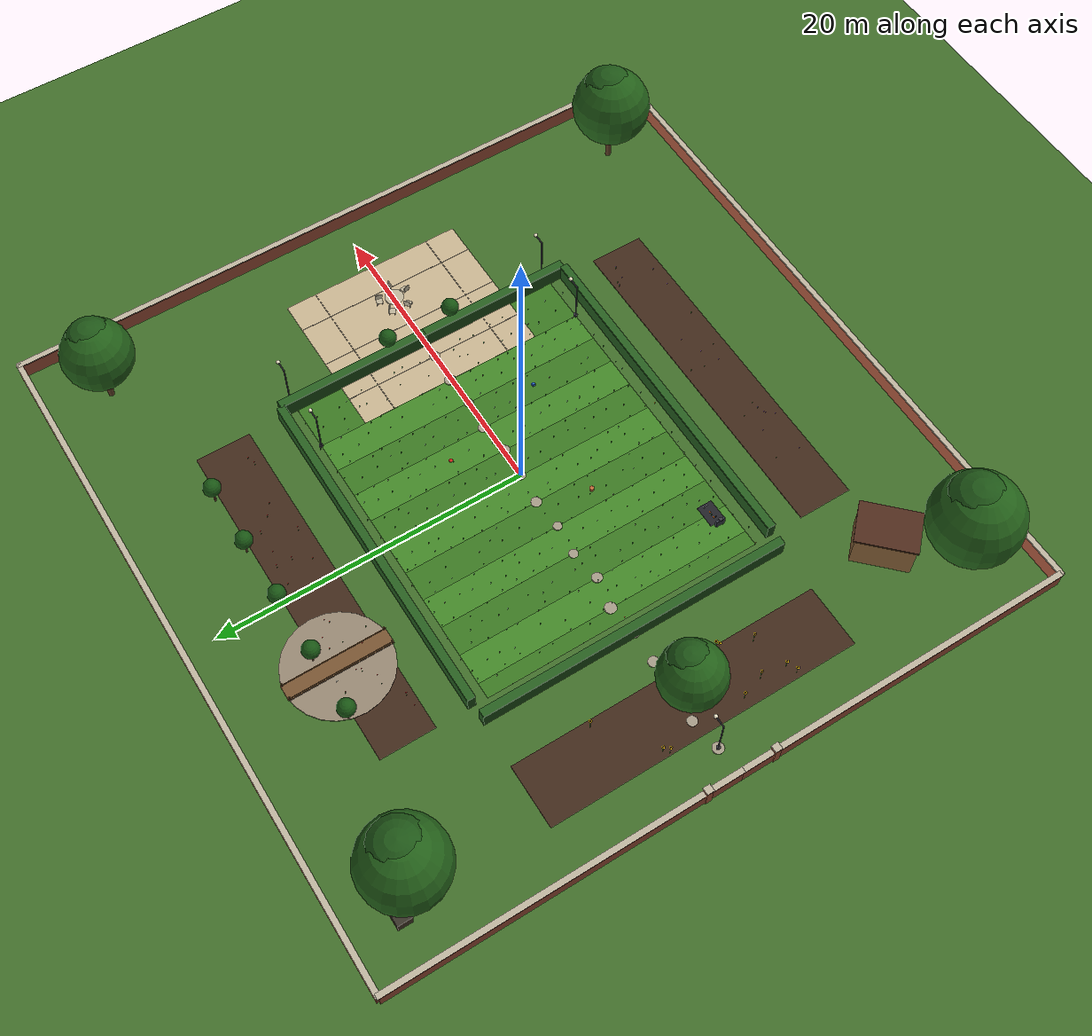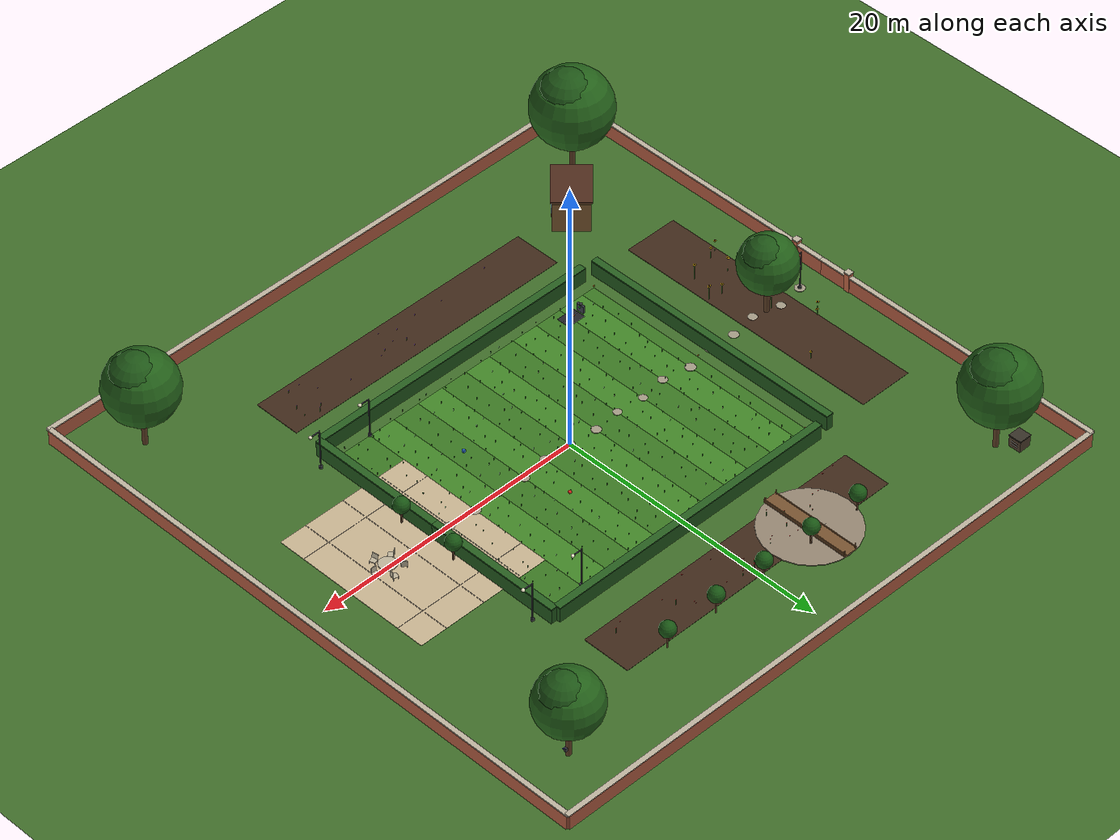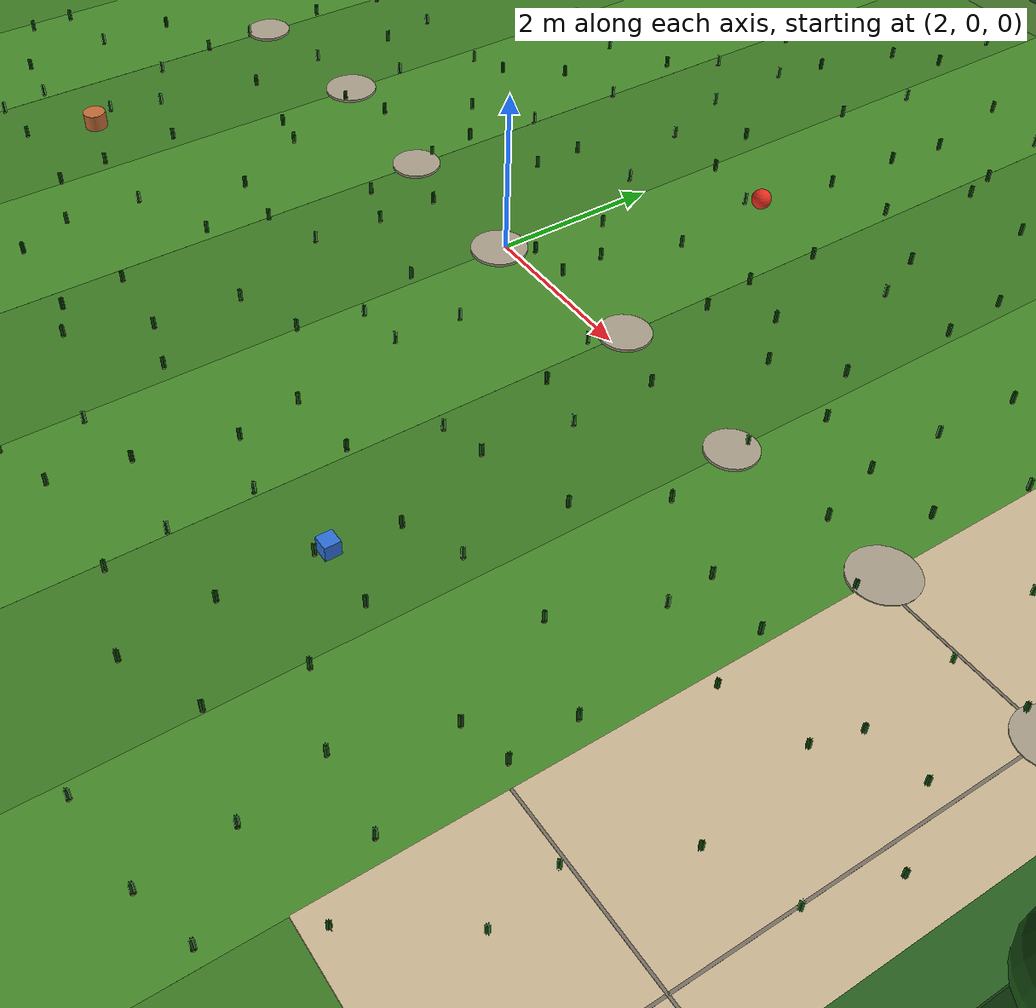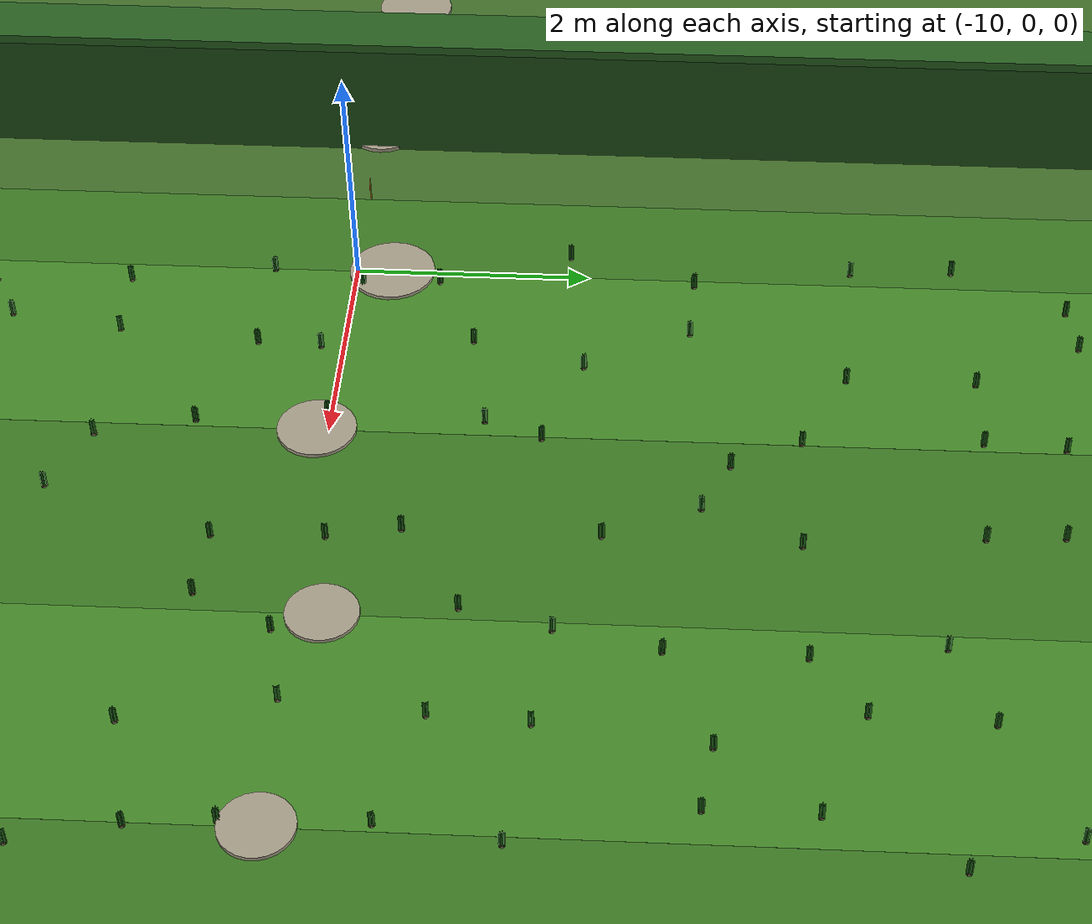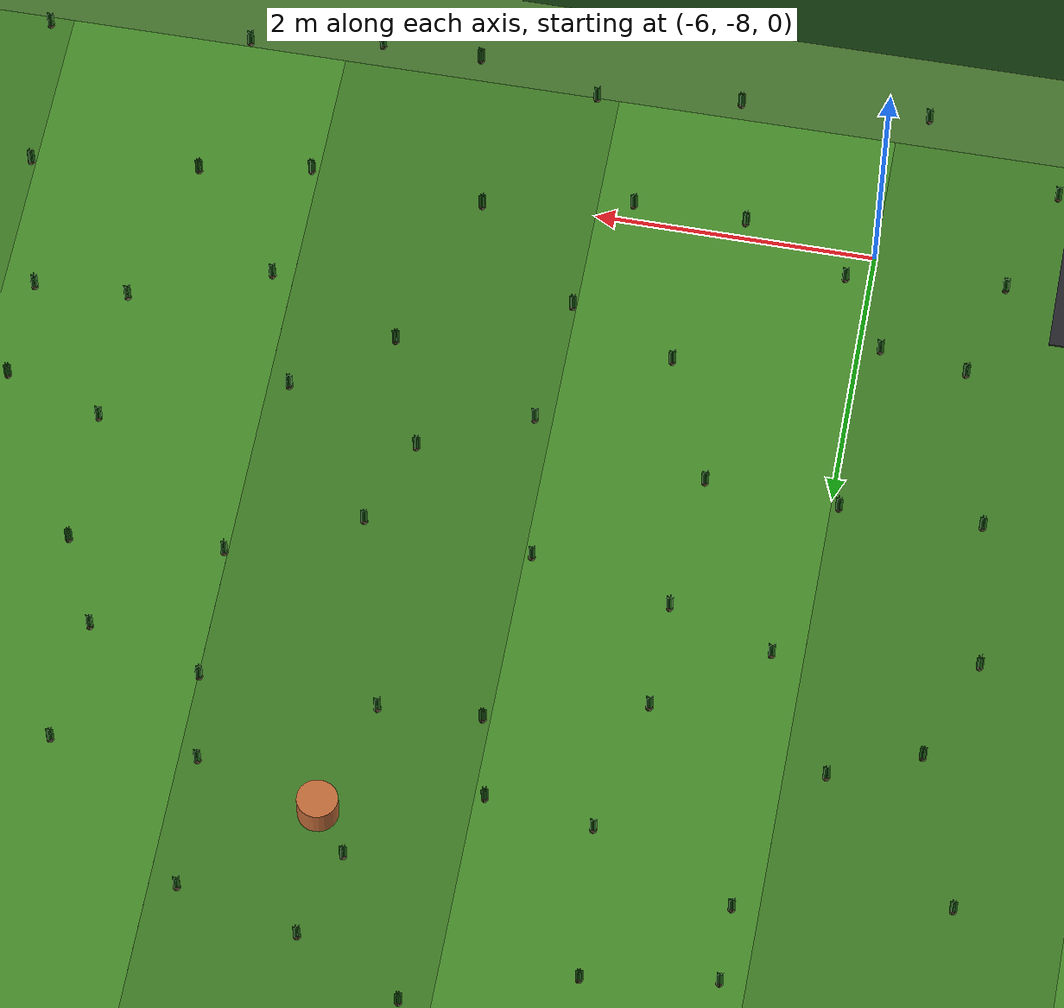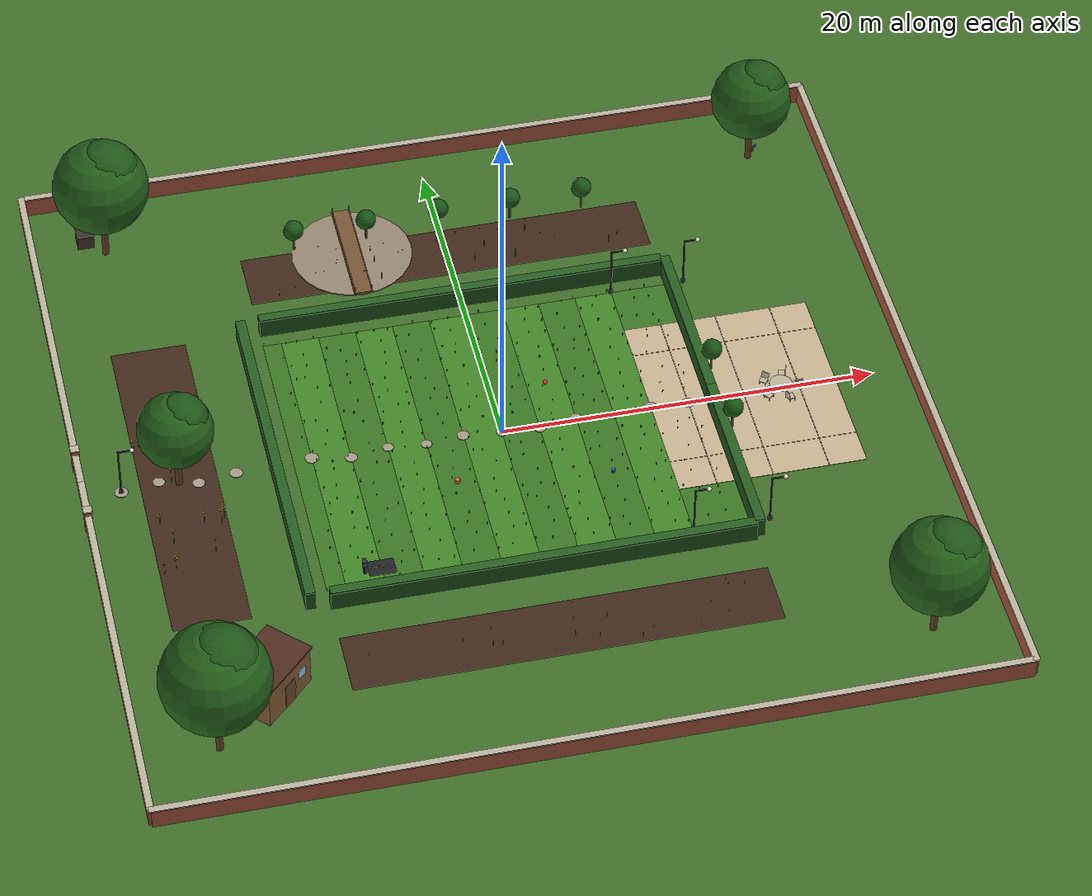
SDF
<?xml version="1.0"?>
<sdf version="1.9">
  <world name="agri_robotics_field">

    <!-- PHYSICS -->
    <gravity>0 0 -9.81</gravity>
    <magnetic_field>6e-06 2.3e-05 -4.2e-05</magnetic_field>
    <atmosphere type="adiabatic"/>

    <spherical_coordinates>
      <surface_model>EARTH_WGS84</surface_model>
      <world_frame_orientation>ENU</world_frame_orientation>
      <latitude_deg>51.5074</latitude_deg>
      <longitude_deg>-0.1278</longitude_deg>
      <elevation>15</elevation>
      <heading_deg>0</heading_deg>
    </spherical_coordinates>

    <physics name="1ms" type="ode">
      <max_step_size>0.001</max_step_size>
      <real_time_factor>1.0</real_time_factor>
      <real_time_update_rate>1000</real_time_update_rate>
      <ode>
        <solver><type>quick</type><iters>100</iters><sor>1.3</sor></solver>
        <constraints>
          <cfm>0</cfm><erp>0.2</erp>
          <contact_max_correcting_vel>100</contact_max_correcting_vel>
          <contact_surface_layer>0.001</contact_surface_layer>
        </constraints>
      </ode>
    </physics>

    <!-- SCENE — afternoon sun, warm English garden light -->
    <scene>
      <ambient>0.60 0.62 0.56 1.0</ambient>
      <background>0.68 0.80 0.96 1.0</background>
      <shadows>true</shadows>
      <fog>
        <color>0.85 0.90 0.96 1</color>
        <type>linear</type>
        <start>55</start>
        <end>130</end>
        <density>0.002</density>
      </fog>
    </scene>

    <!-- LIGHTING -->
    <light name="sun" type="directional">
      <cast_shadows>true</cast_shadows>
      <pose>0 0 40 0 0 0</pose>
      <diffuse>1.0 0.97 0.88 1</diffuse>
      <specular>0.35 0.32 0.25 1</specular>
      <direction>-0.4 0.2 -0.88</direction>
      <attenuation><range>1000</range><constant>0.9</constant><linear>0.01</linear><quadratic>0.001</quadratic></attenuation>
    </light>
    <light name="sky_fill" type="directional">
      <cast_shadows>false</cast_shadows>
      <diffuse>0.30 0.40 0.60 1</diffuse>
      <specular>0 0 0 1</specular>
      <direction>0.1 -0.05 -1</direction>
    </light>
    <light name="patio_light" type="point">
      <pose>8 8 3.0 0 0 0</pose>
      <diffuse>0.95 0.90 0.80 1</diffuse>
      <specular>0.20 0.18 0.14 1</specular>
      <attenuation><range>12</range><constant>0.4</constant><linear>0.08</linear><quadratic>0.03</quadratic></attenuation>
      <cast_shadows>false</cast_shadows>
    </light>
    <light name="shed_light" type="point">
      <pose>-14 -14 2.5 0 0 0</pose>
      <diffuse>0.90 0.88 0.75 1</diffuse>
      <specular>0.15 0.14 0.10 1</specular>
      <attenuation><range>8</range><constant>0.5</constant><linear>0.10</linear><quadratic>0.04</quadratic></attenuation>
      <cast_shadows>false</cast_shadows>
    </light>

    <!-- PLUGINS -->
    <plugin filename="gz-sim-physics-system"       name="gz::sim::systems::Physics"/>
    <plugin filename="gz-sim-user-commands-system"  name="gz::sim::systems::UserCommands"/>
    <plugin filename="gz-sim-scene-broadcaster-system" name="gz::sim::systems::SceneBroadcaster"/>
    <plugin filename="gz-sim-sensors-system"        name="gz::sim::systems::Sensors">
      <render_engine>ogre2</render_engine>
    </plugin>
    <plugin filename="gz-sim-imu-system"            name="gz::sim::systems::Imu"/>
    <plugin filename="gz-sim-navsat-system"         name="gz::sim::systems::NavSat"/>

    <!-- ══════════════════════════════════════════════════
         GROUND SURFACES
    ══════════════════════════════════════════════════ -->

    <!-- Main garden ground (grass colour) -->
    <model name="ground_garden">
      <static>true</static>
      <link name="link">
        <collision name="col">
          <geometry><plane><normal>0 0 1</normal><size>80 80</size></plane></geometry>
          <surface>
            <friction><ode><mu>0.85</mu><mu2>0.85</mu2></ode></friction>
            <contact><ode><kp>1e6</kp><kd>100</kd></ode></contact>
          </surface>
        </collision>
        <visual name="vis">
          <geometry><plane><normal>0 0 1</normal><size>80 80</size></plane></geometry>
          <material>
            <ambient>0.22 0.38 0.14 1</ambient>
            <diffuse>0.26 0.44 0.17 1</diffuse>
            <specular>0.01 0.02 0.01 1</specular>
          </material>
        </visual>
      </link>
    </model>

    <!-- Central manicured lawn (slightly different green, striped effect via two overlapping planes) -->
    <model name="lawn_main">
      <static>true</static>
      <pose>0 0 0.002 0 0 0</pose>
      <link name="link">
        <collision name="col">
          <geometry><box><size>22 18 0.002</size></box></geometry>
          <surface>
            <friction><ode><mu>0.90</mu><mu2>0.90</mu2></ode></friction>
            <contact><ode><kp>1e6</kp><kd>100</kd></ode></contact>
          </surface>
        </collision>
        <visual name="vis_base">
          <geometry><box><size>22 18 0.002</size></box></geometry>
          <material>
            <ambient>0.20 0.42 0.12 1</ambient>
            <diffuse>0.24 0.48 0.14 1</diffuse>
            <specular>0.01 0.02 0.01 1</specular>
          </material>
        </visual>
        <!-- Mowing stripe overlay 1 (lighter alternating strips) -->
        <visual name="stripe_a1"><pose>-9 0 0.001 0 0 0</pose><geometry><box><size>2 18 0.001</size></box></geometry><material><ambient>0.23 0.48 0.14 1</ambient><diffuse>0.27 0.54 0.16 1</diffuse><specular>0.01 0.02 0.01 1</specular></material></visual>
        <visual name="stripe_a2"><pose>-5 0 0.001 0 0 0</pose><geometry><box><size>2 18 0.001</size></box></geometry><material><ambient>0.23 0.48 0.14 1</ambient><diffuse>0.27 0.54 0.16 1</diffuse><specular>0.01 0.02 0.01 1</specular></material></visual>
        <visual name="stripe_a3"><pose>-1 0 0.001 0 0 0</pose><geometry><box><size>2 18 0.001</size></box></geometry><material><ambient>0.23 0.48 0.14 1</ambient><diffuse>0.27 0.54 0.16 1</diffuse><specular>0.01 0.02 0.01 1</specular></material></visual>
        <visual name="stripe_a4"><pose>3 0 0.001 0 0 0</pose><geometry><box><size>2 18 0.001</size></box></geometry><material><ambient>0.23 0.48 0.14 1</ambient><diffuse>0.27 0.54 0.16 1</diffuse><specular>0.01 0.02 0.01 1</specular></material></visual>
        <visual name="stripe_a5"><pose>7 0 0.001 0 0 0</pose><geometry><box><size>2 18 0.001</size></box></geometry><material><ambient>0.23 0.48 0.14 1</ambient><diffuse>0.27 0.54 0.16 1</diffuse><specular>0.01 0.02 0.01 1</specular></material></visual>
      </link>
    </model>

    <!-- Patio: large sandstone slab area -->
    <model name="patio">
      <static>true</static>
      <pose>13 0 0.015 0 0 0</pose>
      <link name="link">
        <collision name="col"><geometry><box><size>10 12 0.02</size></box></geometry></collision>
        <visual name="base">
          <geometry><box><size>10 12 0.02</size></box></geometry>
          <material><ambient>0.76 0.68 0.55 1</ambient><diffuse>0.80 0.72 0.58 1</diffuse><specular>0.10 0.09 0.07 1</specular></material>
        </visual>
        <!-- Grout lines (dark thin boxes overlaid) -->
        <visual name="grout_x1"><pose>0 -4 0.011 0 0 0</pose><geometry><box><size>10 0.03 0.002</size></box></geometry><material><ambient>0.45 0.42 0.38 1</ambient><diffuse>0.48 0.45 0.40 1</diffuse><specular>0.02 0.02 0.02 1</specular></material></visual>
        <visual name="grout_x2"><pose>0 0 0.011 0 0 0</pose><geometry><box><size>10 0.03 0.002</size></box></geometry><material><ambient>0.45 0.42 0.38 1</ambient><diffuse>0.48 0.45 0.40 1</diffuse><specular>0.02 0.02 0.02 1</specular></material></visual>
        <visual name="grout_x3"><pose>0 4 0.011 0 0 0</pose><geometry><box><size>10 0.03 0.002</size></box></geometry><material><ambient>0.45 0.42 0.38 1</ambient><diffuse>0.48 0.45 0.40 1</diffuse><specular>0.02 0.02 0.02 1</specular></material></visual>
        <visual name="grout_y1"><pose>-3 0 0.011 0 0 0</pose><geometry><box><size>0.03 12 0.002</size></box></geometry><material><ambient>0.45 0.42 0.38 1</ambient><diffuse>0.48 0.45 0.40 1</diffuse><specular>0.02 0.02 0.02 1</specular></material></visual>
        <visual name="grout_y2"><pose>0 0 0.011 0 0 0</pose><geometry><box><size>0.03 12 0.002</size></box></geometry><material><ambient>0.45 0.42 0.38 1</ambient><diffuse>0.48 0.45 0.40 1</diffuse><specular>0.02 0.02 0.02 1</specular></material></visual>
        <visual name="grout_y3"><pose>3 0 0.011 0 0 0</pose><geometry><box><size>0.03 12 0.002</size></box></geometry><material><ambient>0.45 0.42 0.38 1</ambient><diffuse>0.48 0.45 0.40 1</diffuse><specular>0.02 0.02 0.02 1</specular></material></visual>
      </link>
    </model>

    <!-- North wall -->
    <model name="wall_north">
      <static>true</static>
      <pose>0 22 0.55 0 0 0</pose>
      <link name="link">
        <collision name="col"><geometry><box><size>44 0.28 1.10</size></box></geometry></collision>
        <visual name="wall">
          <geometry><box><size>44 0.28 1.10</size></box></geometry>
          <material><ambient>0.62 0.32 0.22 1</ambient><diffuse>0.66 0.34 0.24 1</diffuse><specular>0.03 0.02 0.01 1</specular></material>
        </visual>
        <!-- Coping stones on top -->
        <visual name="coping">
          <pose>0 0 0.58 0 0 0</pose>
          <geometry><box><size>44.2 0.35 0.08</size></box></geometry>
          <material><ambient>0.72 0.68 0.60 1</ambient><diffuse>0.76 0.72 0.64 1</diffuse><specular>0.10 0.09 0.08 1</specular></material>
        </visual>
      </link>
    </model>
    <!-- South wall -->
    <model name="wall_south">
      <static>true</static>
      <pose>0 -22 0.55 0 0 0</pose>
      <link name="link">
        <collision name="col"><geometry><box><size>44 0.28 1.10</size></box></geometry></collision>
        <visual name="wall"><geometry><box><size>44 0.28 1.10</size></box></geometry><material><ambient>0.62 0.32 0.22 1</ambient><diffuse>0.66 0.34 0.24 1</diffuse><specular>0.03 0.02 0.01 1</specular></material></visual>
        <visual name="coping"><pose>0 0 0.58 0 0 0</pose><geometry><box><size>44.2 0.35 0.08</size></box></geometry><material><ambient>0.72 0.68 0.60 1</ambient><diffuse>0.76 0.72 0.64 1</diffuse><specular>0.10 0.09 0.08 1</specular></material></visual>
      </link>
    </model>
    <!-- East wall -->
    <model name="wall_east">
      <static>true</static>
      <pose>22 0 0.55 0 0 0</pose>
      <link name="link">
        <collision name="col"><geometry><box><size>0.28 44 1.10</size></box></geometry></collision>
        <visual name="wall"><geometry><box><size>0.28 44 1.10</size></box></geometry><material><ambient>0.62 0.32 0.22 1</ambient><diffuse>0.66 0.34 0.24 1</diffuse><specular>0.03 0.02 0.01 1</specular></material></visual>
        <visual name="coping"><pose>0 0 0.58 0 0 0</pose><geometry><box><size>0.35 44.2 0.08</size></box></geometry><material><ambient>0.72 0.68 0.60 1</ambient><diffuse>0.76 0.72 0.64 1</diffuse><specular>0.10 0.09 0.08 1</specular></material></visual>
      </link>
    </model>
    <!-- West wall (with gate opening at y=0) -->
    <model name="wall_west_n">
      <static>true</static>
      <pose>-22 11 0.55 0 0 0</pose>
      <link name="link">
        <collision name="col"><geometry><box><size>0.28 22 1.10</size></box></geometry></collision>
        <visual name="wall"><geometry><box><size>0.28 22 1.10</size></box></geometry><material><ambient>0.62 0.32 0.22 1</ambient><diffuse>0.66 0.34 0.24 1</diffuse><specular>0.03 0.02 0.01 1</specular></material></visual>
        <visual name="coping"><pose>0 0 0.58 0 0 0</pose><geometry><box><size>0.35 22.2 0.08</size></box></geometry><material><ambient>0.72 0.68 0.60 1</ambient><diffuse>0.76 0.72 0.64 1</diffuse><specular>0.10 0.09 0.08 1</specular></material></visual>
      </link>
    </model>
    <model name="wall_west_s">
      <static>true</static>
      <pose>-22 -11 0.55 0 0 0</pose>
      <link name="link">
        <collision name="col"><geometry><box><size>0.28 22 1.10</size></box></geometry></collision>
        <visual name="wall"><geometry><box><size>0.28 22 1.10</size></box></geometry><material><ambient>0.62 0.32 0.22 1</ambient><diffuse>0.66 0.34 0.24 1</diffuse><specular>0.03 0.02 0.01 1</specular></material></visual>
        <visual name="coping"><pose>0 0 0.58 0 0 0</pose><geometry><box><size>0.35 22.2 0.08</size></box></geometry><material><ambient>0.72 0.68 0.60 1</ambient><diffuse>0.76 0.72 0.64 1</diffuse><specular>0.10 0.09 0.08 1</specular></material></visual>
      </link>
    </model>
    <!-- Gate pillars -->
    <model name="gate_pillar_n">
      <static>true</static>
      <pose>-22 2.2 0.7 0 0 0</pose>
      <link name="link">
        <collision name="col"><geometry><box><size>0.40 0.40 1.40</size></box></geometry></collision>
        <visual name="body"><geometry><box><size>0.40 0.40 1.40</size></box></geometry><material><ambient>0.68 0.36 0.24 1</ambient><diffuse>0.72 0.38 0.26 1</diffuse><specular>0.04 0.02 0.01 1</specular></material></visual>
        <visual name="cap"><pose>0 0 0.74 0 0 0</pose><geometry><box><size>0.46 0.46 0.08</size></box></geometry><material><ambient>0.72 0.68 0.60 1</ambient><diffuse>0.76 0.72 0.64 1</diffuse><specular>0.15 0.14 0.12 1</specular></material></visual>
      </link>
    </model>
    <model name="gate_pillar_s">
      <static>true</static>
      <pose>-22 -2.2 0.7 0 0 0</pose>
      <link name="link">
        <collision name="col"><geometry><box><size>0.40 0.40 1.40</size></box></geometry></collision>
        <visual name="body"><geometry><box><size>0.40 0.40 1.40</size></box></geometry><material><ambient>0.68 0.36 0.24 1</ambient><diffuse>0.72 0.38 0.26 1</diffuse><specular>0.04 0.02 0.01 1</specular></material></visual>
        <visual name="cap"><pose>0 0 0.74 0 0 0</pose><geometry><box><size>0.46 0.46 0.08</size></box></geometry><material><ambient>0.72 0.68 0.60 1</ambient><diffuse>0.76 0.72 0.64 1</diffuse><specular>0.15 0.14 0.12 1</specular></material></visual>
      </link>
    </model>

    <!-- ══════════════════════════════════════════════════
         HEDGEROWS — separate lawn from garden beds
    ══════════════════════════════════════════════════ -->
    <!-- North hedge (top of lawn) -->
    <model name="hedge_north">
      <static>true</static>
      <pose>0 10 0.55 0 0 0</pose>
      <link name="link">
        <collision name="col"><geometry><box><size>22 0.50 1.10</size></box></geometry></collision>
        <visual name="body"><geometry><box><size>22 0.50 1.10</size></box></geometry><material><ambient>0.10 0.28 0.08 1</ambient><diffuse>0.12 0.32 0.10 1</diffuse><specular>0.01 0.02 0.01 1</specular></material></visual>
        <!-- Textured top (slightly lighter row) -->
        <visual name="top"><pose>0 0 0.56 0 0 0</pose><geometry><box><size>22 0.52 0.08</size></box></geometry><material><ambient>0.14 0.35 0.11 1</ambient><diffuse>0.16 0.38 0.13 1</diffuse><specular>0.01 0.02 0.01 1</specular></material></visual>
      </link>
    </model>
    <!-- South hedge -->
    <model name="hedge_south">
      <static>true</static>
      <pose>0 -10 0.55 0 0 0</pose>
      <link name="link">
        <collision name="col"><geometry><box><size>22 0.50 1.10</size></box></geometry></collision>
        <visual name="body"><geometry><box><size>22 0.50 1.10</size></box></geometry><material><ambient>0.10 0.28 0.08 1</ambient><diffuse>0.12 0.32 0.10 1</diffuse><specular>0.01 0.02 0.01 1</specular></material></visual>
        <visual name="top"><pose>0 0 0.56 0 0 0</pose><geometry><box><size>22 0.52 0.08</size></box></geometry><material><ambient>0.14 0.35 0.11 1</ambient><diffuse>0.16 0.38 0.13 1</diffuse><specular>0.01 0.02 0.01 1</specular></material></visual>
      </link>
    </model>
    <!-- West hedge (left of lawn) -->
    <model name="hedge_west">
      <static>true</static>
      <pose>-12 0 0.55 0 0 0</pose>
      <link name="link">
        <collision name="col"><geometry><box><size>0.50 20 1.10</size></box></geometry></collision>
        <visual name="body"><geometry><box><size>0.50 20 1.10</size></box></geometry><material><ambient>0.10 0.28 0.08 1</ambient><diffuse>0.12 0.32 0.10 1</diffuse><specular>0.01 0.02 0.01 1</specular></material></visual>
        <visual name="top"><pose>0 0 0.56 0 0 0</pose><geometry><box><size>0.52 20 0.08</size></box></geometry><material><ambient>0.14 0.35 0.11 1</ambient><diffuse>0.16 0.38 0.13 1</diffuse><specular>0.01 0.02 0.01 1</specular></material></visual>
      </link>
    </model>
    <!-- East hedge (right of lawn — gap for patio access) -->
    <model name="hedge_east_n">
      <static>true</static>
      <pose>11.2 5 0.55 0 0 0</pose>
      <link name="link">
        <collision name="col"><geometry><box><size>0.50 10 1.10</size></box></geometry></collision>
        <visual name="body"><geometry><box><size>0.50 10 1.10</size></box></geometry><material><ambient>0.10 0.28 0.08 1</ambient><diffuse>0.12 0.32 0.10 1</diffuse><specular>0.01 0.02 0.01 1</specular></material></visual>
        <visual name="top"><pose>0 0 0.56 0 0 0</pose><geometry><box><size>0.52 10 0.08</size></box></geometry><material><ambient>0.14 0.35 0.11 1</ambient><diffuse>0.16 0.38 0.13 1</diffuse><specular>0.01 0.02 0.01 1</specular></material></visual>
      </link>
    </model>
    <model name="hedge_east_s">
      <static>true</static>
      <pose>11.2 -5 0.55 0 0 0</pose>
      <link name="link">
        <collision name="col"><geometry><box><size>0.50 10 1.10</size></box></geometry></collision>
        <visual name="body"><geometry><box><size>0.50 10 1.10</size></box></geometry><material><ambient>0.10 0.28 0.08 1</ambient><diffuse>0.12 0.32 0.10 1</diffuse><specular>0.01 0.02 0.01 1</specular></material></visual>
        <visual name="top"><pose>0 0 0.56 0 0 0</pose><geometry><box><size>0.52 10 0.08</size></box></geometry><material><ambient>0.14 0.35 0.11 1</ambient><diffuse>0.16 0.38 0.13 1</diffuse><specular>0.01 0.02 0.01 1</specular></material></visual>
      </link>
    </model>

    <!-- ══ GRASS TUFTS — dense lawn coverage ══ -->
    <include>
      <uri>model://grass_tuft</uri>
      <name>gtuft_0001</name>
      <pose>-9.916 -9.285 0.0006 0 0 0.701</pose>
    </include>
    <include>
      <uri>model://grass_tuft</uri>
      <name>gtuft_0002</name>
      <pose>-9.858 -7.894 0.0018 0 0 0.273</pose>
    </include>
    <include>
      <uri>model://grass_tuft</uri>
      <name>gtuft_0003</name>
      <pose>-10.047 -7.282 0.0004 0 0 1.588</pose>
    </include>
    <include>
      <uri>model://grass_tuft</uri>
      <name>gtuft_0004</name>
      <pose>-10.284 -6.181 0.0013 0 0 1.712</pose>
    </include>
    <include>
      <uri>model://grass_tuft</uri>
      <name>gtuft_0005</name>
      <pose>-10.168 -4.946 0.0016 0 0 0.020</pose>
    </include>
    <include>
      <uri>model://grass_tuft</uri>
      <name>gtuft_0006</name>
      <pose>-9.817 -3.881 0.0007 0 0 0.488</pose>
    </include>
    <include>
      <uri>model://grass_tuft</uri>
      <name>gtuft_0007</name>
      <pose>-9.726 -3.098 0.0002 0 0 0.304</pose>
    </include>
    <include>
      <uri>model://grass_tuft</uri>
      <name>gtuft_0008</name>
      <pose>-9.792 -1.938 0.0016 0 0 2.293</pose>
    </include>
    <include>
      <uri>model://grass_tuft</uri>
      <name>gtuft_0009</name>
      <pose>-9.978 -0.716 0.0008 0 0 1.734</pose>
    </include>
    <include>
      <uri>model://grass_tuft</uri>
      <name>gtuft_0010</name>
      <pose>-9.802 0.071 0.0017 0 0 1.814</pose>
    </include>
    <include>
      <uri>model://grass_tuft</uri>
      <name>gtuft_0011</name>
      <pose>-9.877 0.727 0.0005 0 0 0.909</pose>
    </include>
    <include>
      <uri>model://grass_tuft</uri>
      <name>gtuft_0012</name>
      <pose>-10.252 1.840 0.0002 0 0 0.873</pose>
    </include>
    <include>
      <uri>model://grass_tuft</uri>
      <name>gtuft_0013</name>
      <pose>-9.919 2.919 0.0007 0 0 0.658</pose>
    </include>
    <include>
      <uri>model://grass_tuft</uri>
      <name>gtuft_0014</name>
      <pose>-10.140 4.262 0.0013 0 0 1.914</pose>
    </include>
    <include>
      <uri>model://grass_tuft</uri>
      <name>gtuft_0015</name>
      <pose>-10.197 5.137 0.0003 0 0 1.192</pose>
    </include>
    <include>
      <uri>model://grass_tuft</uri>
      <name>gtuft_0016</name>
      <pose>-9.706 6.084 0.0011 0 0 2.151</pose>
    </include>
    <include>
      <uri>model://grass_tuft</uri>
      <name>gtuft_0017</name>
      <pose>-9.794 7.166 0.0005 0 0 0.101</pose>
    </include>
    <include>
      <uri>model://grass_tuft</uri>
      <name>gtuft_0018</name>
      <pose>-10.111 7.861 0.0004 0 0 2.962</pose>
    </include>
    <include>
      <uri>model://grass_tuft</uri>
      <name>gtuft_0019</name>
      <pose>-9.774 8.889 0.0013 0 0 1.243</pose>
    </include>
    <include>
      <uri>model://grass_tuft</uri>
      <name>gtuft_0020</name>
      <pose>-8.751 -9.025 0.0005 0 0 0.775</pose>
    </include>
    <include>
      <uri>model://grass_tuft</uri>
      <name>gtuft_0021</name>
      <pose>-8.963 -8.142 0.0012 0 0 2.821</pose>
    </include>
    <include>
      <uri>model://grass_tuft</uri>
      <name>gtuft_0022</name>
      <pose>-9.060 -7.168 0.0020 0 0 1.601</pose>
    </include>
    <include>
      <uri>model://grass_tuft</uri>
      <name>gtuft_0023</name>
      <pose>-9.245 -6.272 0.0002 0 0 1.971</pose>
    </include>
    <include>
      <uri>model://grass_tuft</uri>
      <name>gtuft_0024</name>
      <pose>-8.825 -5.047 0.0001 0 0 1.199</pose>
    </include>
    <include>
      <uri>model://grass_tuft</uri>
      <name>gtuft_0025</name>
      <pose>-8.702 -3.983 0.0019 0 0 2.704</pose>
    </include>
    <include>
      <uri>model://grass_tuft</uri>
      <name>gtuft_0026</name>
      <pose>-9.293 -2.868 0.0014 0 0 1.687</pose>
    </include>
    <include>
      <uri>model://grass_tuft</uri>
      <name>gtuft_0027</name>
      <pose>-9.140 -1.915 0.0002 0 0 1.366</pose>
    </include>
    <include>
      <uri>model://grass_tuft</uri>
      <name>gtuft_0028</name>
      <pose>-9.028 -0.728 0.0018 0 0 0.827</pose>
    </include>
    <include>
      <uri>model://grass_tuft</uri>
      <name>gtuft_0029</name>
      <pose>-9.000 -0.193 0.0018 0 0 2.735</pose>
    </include>
    <include>
      <uri>model://grass_tuft</uri>
      <name>gtuft_0030</name>
      <pose>-9.121 1.083 0.0012 0 0 0.480</pose>
    </include>
    <include>
      <uri>model://grass_tuft</uri>
      <name>gtuft_0031</name>
      <pose>-8.842 2.024 0.0016 0 0 1.666</pose>
    </include>
    <include>
      <uri>model://grass_tuft</uri>
      <name>gtuft_0032</name>
      <pose>-9.300 2.894 0.0000 0 0 2.919</pose>
    </include>
    <include>
      <uri>model://grass_tuft</uri>
      <name>gtuft_0033</name>
      <pose>-8.773 4.199 0.0006 0 0 0.182</pose>
    </include>
    <include>
      <uri>model://grass_tuft</uri>
      <name>gtuft_0034</name>
      <pose>-8.773 5.268 0.0002 0 0 1.527</pose>
    </include>
    <include>
      <uri>model://grass_tuft</uri>
      <name>gtuft_0035</name>
      <pose>-9.258 6.156 0.0015 0 0 0.403</pose>
    </include>
    <include>
      <uri>model://grass_tuft</uri>
      <name>gtuft_0036</name>
      <pose>-9.015 7.030 0.0005 0 0 2.741</pose>
    </include>
    <include>
      <uri>model://grass_tuft</uri>
      <name>gtuft_0037</name>
      <pose>-9.046 7.827 0.0011 0 0 2.293</pose>
    </include>
    <include>
      <uri>model://grass_tuft</uri>
      <name>gtuft_0038</name>
      <pose>-9.179 8.887 0.0020 0 0 2.042</pose>
    </include>
    <include>
      <uri>model://grass_tuft</uri>
      <name>gtuft_0039</name>
      <pose>-8.037 -8.989 0.0002 0 0 0.706</pose>
    </include>
    <include>
      <uri>model://grass_tuft</uri>
      <name>gtuft_0040</name>
      <pose>-8.097 -7.947 0.0005 0 0 0.692</pose>
    </include>
    <include>
      <uri>model://grass_tuft</uri>
      <name>gtuft_0041</name>
      <pose>-8.257 -6.921 0.0005 0 0 2.844</pose>
    </include>
    <include>
      <uri>model://grass_tuft</uri>
      <name>gtuft_0042</name>
      <pose>-7.784 -6.257 0.0005 0 0 2.102</pose>
    </include>
    <include>
      <uri>model://grass_tuft</uri>
      <name>gtuft_0043</name>
      <pose>-8.171 -5.221 0.0019 0 0 1.794</pose>
    </include>
    <include>
      <uri>model://grass_tuft</uri>
      <name>gtuft_0044</name>
      <pose>-8.016 -3.829 0.0016 0 0 0.598</pose>
    </include>
    <include>
      <uri>model://grass_tuft</uri>
      <name>gtuft_0045</name>
      <pose>-8.242 -3.041 0.0008 0 0 1.467</pose>
    </include>
    <include>
      <uri>model://grass_tuft</uri>
      <name>gtuft_0046</name>
      <pose>-7.863 -1.896 0.0020 0 0 0.309</pose>
    </include>
    <include>
      <uri>model://grass_tuft</uri>
      <name>gtuft_0047</name>
      <pose>-8.058 -1.096 0.0017 0 0 0.781</pose>
    </include>
    <include>
      <uri>model://grass_tuft</uri>
      <name>gtuft_0048</name>
      <pose>-8.186 -0.031 0.0008 0 0 0.875</pose>
    </include>
    <include>
      <uri>model://grass_tuft</uri>
      <name>gtuft_0049</name>
      <pose>-8.150 1.254 0.0009 0 0 2.706</pose>
    </include>
    <include>
      <uri>model://grass_tuft</uri>
      <name>gtuft_0050</name>
      <pose>-7.970 1.730 0.0020 0 0 2.626</pose>
    </include>
    <include>
      <uri>model://grass_tuft</uri>
      <name>gtuft_0051</name>
      <pose>-7.719 3.256 0.0017 0 0 0.522</pose>
    </include>
    <include>
      <uri>model://grass_tuft</uri>
      <name>gtuft_0052</name>
      <pose>-8.009 3.828 0.0008 0 0 0.184</pose>
    </include>
    <include>
      <uri>model://grass_tuft</uri>
      <name>gtuft_0053</name>
      <pose>-8.073 5.291 0.0005 0 0 2.463</pose>
    </include>
    <include>
      <uri>model://grass_tuft</uri>
      <name>gtuft_0054</name>
      <pose>-8.027 5.954 0.0019 0 0 3.127</pose>
    </include>
    <include>
      <uri>model://grass_tuft</uri>
      <name>gtuft_0055</name>
      <pose>-7.967 7.131 0.0003 0 0 0.932</pose>
    </include>
    <include>
      <uri>model://grass_tuft</uri>
      <name>gtuft_0056</name>
      <pose>-7.719 8.048 0.0011 0 0 2.350</pose>
    </include>
    <include>
      <uri>model://grass_tuft</uri>
      <name>gtuft_0057</name>
      <pose>-8.266 9.051 0.0010 0 0 2.679</pose>
    </include>
    <include>
      <uri>model://grass_tuft</uri>
      <name>gtuft_0058</name>
      <pose>-7.206 -8.724 0.0002 0 0 0.584</pose>
    </include>
    <include>
      <uri>model://grass_tuft</uri>
      <name>gtuft_0059</name>
      <pose>-6.943 -7.895 0.0005 0 0 0.377</pose>
    </include>
    <include>
      <uri>model://grass_tuft</uri>
      <name>gtuft_0060</name>
      <pose>-6.766 -7.152 0.0012 0 0 1.946</pose>
    </include>
    <include>
      <uri>model://grass_tuft</uri>
      <name>gtuft_0061</name>
      <pose>-7.048 -5.950 0.0010 0 0 2.936</pose>
    </include>
    <include>
      <uri>model://grass_tuft</uri>
      <name>gtuft_0062</name>
      <pose>-7.177 -4.870 0.0005 0 0 1.243</pose>
    </include>
    <include>
      <uri>model://grass_tuft</uri>
      <name>gtuft_0063</name>
      <pose>-6.897 -4.120 0.0006 0 0 2.362</pose>
    </include>
    <include>
      <uri>model://grass_tuft</uri>
      <name>gtuft_0064</name>
      <pose>-7.256 -3.025 0.0020 0 0 3.129</pose>
    </include>
    <include>
      <uri>model://grass_tuft</uri>
      <name>gtuft_0065</name>
      <pose>-7.256 -2.172 0.0005 0 0 2.932</pose>
    </include>
    <include>
      <uri>model://grass_tuft</uri>
      <name>gtuft_0066</name>
      <pose>-6.771 -0.772 0.0007 0 0 0.496</pose>
    </include>
    <include>
      <uri>model://grass_tuft</uri>
      <name>gtuft_0067</name>
      <pose>-6.800 0.122 0.0012 0 0 3.101</pose>
    </include>
    <include>
      <uri>model://grass_tuft</uri>
      <name>gtuft_0068</name>
      <pose>-6.908 0.705 0.0016 0 0 0.941</pose>
    </include>
    <include>
      <uri>model://grass_tuft</uri>
      <name>gtuft_0069</name>
      <pose>-6.902 2.263 0.0003 0 0 0.363</pose>
    </include>
    <include>
      <uri>model://grass_tuft</uri>
      <name>gtuft_0070</name>
      <pose>-7.236 3.032 0.0005 0 0 1.900</pose>
    </include>
    <include>
      <uri>model://grass_tuft</uri>
      <name>gtuft_0071</name>
      <pose>-6.869 3.822 0.0013 0 0 0.829</pose>
    </include>
    <include>
      <uri>model://grass_tuft</uri>
      <name>gtuft_0072</name>
      <pose>-7.007 5.243 0.0017 0 0 0.290</pose>
    </include>
    <include>
      <uri>model://grass_tuft</uri>
      <name>gtuft_0073</name>
      <pose>-7.046 5.866 0.0000 0 0 2.423</pose>
    </include>
    <include>
      <uri>model://grass_tuft</uri>
      <name>gtuft_0074</name>
      <pose>-6.918 6.857 0.0015 0 0 1.733</pose>
    </include>
    <include>
      <uri>model://grass_tuft</uri>
      <name>gtuft_0075</name>
      <pose>-7.043 7.706 0.0002 0 0 2.774</pose>
    </include>
    <include>
      <uri>model://grass_tuft</uri>
      <name>gtuft_0076</name>
      <pose>-6.758 9.027 0.0017 0 0 1.830</pose>
    </include>
    <include>
      <uri>model://grass_tuft</uri>
      <name>gtuft_0077</name>
      <pose>-6.211 -9.224 0.0006 0 0 2.824</pose>
    </include>
    <include>
      <uri>model://grass_tuft</uri>
      <name>gtuft_0078</name>
      <pose>-5.822 -7.784 0.0018 0 0 0.660</pose>
    </include>
    <include>
      <uri>model://grass_tuft</uri>
      <name>gtuft_0079</name>
      <pose>-6.150 -7.238 0.0016 0 0 2.778</pose>
    </include>
    <include>
      <uri>model://grass_tuft</uri>
      <name>gtuft_0080</name>
      <pose>-6.056 -5.928 0.0003 0 0 2.921</pose>
    </include>
    <include>
      <uri>model://grass_tuft</uri>
      <name>gtuft_0081</name>
      <pose>-5.781 -4.714 0.0016 0 0 2.769</pose>
    </include>
    <include>
      <uri>model://grass_tuft</uri>
      <name>gtuft_0082</name>
      <pose>-6.285 -3.858 0.0007 0 0 2.924</pose>
    </include>
    <include>
      <uri>model://grass_tuft</uri>
      <name>gtuft_0083</name>
      <pose>-5.819 -2.782 0.0016 0 0 0.838</pose>
    </include>
    <include>
      <uri>model://grass_tuft</uri>
      <name>gtuft_0084</name>
      <pose>-5.828 -2.235 0.0017 0 0 2.697</pose>
    </include>
    <include>
      <uri>model://grass_tuft</uri>
      <name>gtuft_0085</name>
      <pose>-6.167 -0.810 0.0009 0 0 0.959</pose>
    </include>
    <include>
      <uri>model://grass_tuft</uri>
      <name>gtuft_0086</name>
      <pose>-5.823 -0.163 0.0000 0 0 0.607</pose>
    </include>
    <include>
      <uri>model://grass_tuft</uri>
      <name>gtuft_0087</name>
      <pose>-6.103 1.219 0.0019 0 0 0.877</pose>
    </include>
    <include>
      <uri>model://grass_tuft</uri>
      <name>gtuft_0088</name>
      <pose>-5.915 1.940 0.0020 0 0 1.685</pose>
    </include>
    <include>
      <uri>model://grass_tuft</uri>
      <name>gtuft_0089</name>
      <pose>-5.736 2.769 0.0019 0 0 0.561</pose>
    </include>
    <include>
      <uri>model://grass_tuft</uri>
      <name>gtuft_0090</name>
      <pose>-5.722 3.859 0.0002 0 0 1.365</pose>
    </include>
    <include>
      <uri>model://grass_tuft</uri>
      <name>gtuft_0091</name>
      <pose>-5.863 4.888 0.0012 0 0 1.607</pose>
    </include>
    <include>
      <uri>model://grass_tuft</uri>
      <name>gtuft_0092</name>
      <pose>-6.069 6.046 0.0005 0 0 2.227</pose>
    </include>
    <include>
      <uri>model://grass_tuft</uri>
      <name>gtuft_0093</name>
      <pose>-6.299 7.255 0.0011 0 0 2.260</pose>
    </include>
    <include>
      <uri>model://grass_tuft</uri>
      <name>gtuft_0094</name>
      <pose>-5.855 8.102 0.0007 0 0 0.220</pose>
    </include>
    <include>
      <uri>model://grass_tuft</uri>
      <name>gtuft_0095</name>
      <pose>-5.901 8.898 0.0006 0 0 2.664</pose>
    </include>
    <include>
      <uri>model://grass_tuft</uri>
      <name>gtuft_0096</name>
      <pose>-4.868 -9.120 0.0006 0 0 1.283</pose>
    </include>
    <include>
      <uri>model://grass_tuft</uri>
      <name>gtuft_0097</name>
      <pose>-5.059 -8.123 0.0003 0 0 1.321</pose>
    </include>
    <include>
      <uri>model://grass_tuft</uri>
      <name>gtuft_0098</name>
      <pose>-4.736 -6.894 0.0018 0 0 1.934</pose>
    </include>
    <include>
      <uri>model://grass_tuft</uri>
      <name>gtuft_0099</name>
      <pose>-5.119 -5.971 0.0000 0 0 0.901</pose>
    </include>
    <include>
      <uri>model://grass_tuft</uri>
      <name>gtuft_0100</name>
      <pose>-5.042 -4.952 0.0013 0 0 1.461</pose>
    </include>
    <include>
      <uri>model://grass_tuft</uri>
      <name>gtuft_0101</name>
      <pose>-5.035 -4.172 0.0009 0 0 2.831</pose>
    </include>
    <include>
      <uri>model://grass_tuft</uri>
      <name>gtuft_0102</name>
      <pose>-4.822 -3.198 0.0002 0 0 1.619</pose>
    </include>
    <include>
      <uri>model://grass_tuft</uri>
      <name>gtuft_0103</name>
      <pose>-4.920 -2.099 0.0016 0 0 2.360</pose>
    </include>
    <include>
      <uri>model://grass_tuft</uri>
      <name>gtuft_0104</name>
      <pose>-4.896 -1.165 0.0004 0 0 0.077</pose>
    </include>
    <include>
      <uri>model://grass_tuft</uri>
      <name>gtuft_0105</name>
      <pose>-5.153 -0.015 0.0017 0 0 0.229</pose>
    </include>
    <include>
      <uri>model://grass_tuft</uri>
      <name>gtuft_0106</name>
      <pose>-5.051 1.078 0.0004 0 0 2.188</pose>
    </include>
    <include>
      <uri>model://grass_tuft</uri>
      <name>gtuft_0107</name>
      <pose>-5.003 1.846 0.0013 0 0 0.017</pose>
    </include>
    <include>
      <uri>model://grass_tuft</uri>
      <name>gtuft_0108</name>
      <pose>-4.849 3.162 0.0002 0 0 1.336</pose>
    </include>
    <include>
      <uri>model://grass_tuft</uri>
      <name>gtuft_0109</name>
      <pose>-5.194 4.275 0.0010 0 0 0.158</pose>
    </include>
    <include>
      <uri>model://grass_tuft</uri>
      <name>gtuft_0110</name>
      <pose>-5.150 5.209 0.0009 0 0 2.518</pose>
    </include>
    <include>
      <uri>model://grass_tuft</uri>
      <name>gtuft_0111</name>
      <pose>-4.899 6.293 0.0012 0 0 2.985</pose>
    </include>
    <include>
      <uri>model://grass_tuft</uri>
      <name>gtuft_0112</name>
      <pose>-4.765 7.068 0.0014 0 0 1.586</pose>
    </include>
    <include>
      <uri>model://grass_tuft</uri>
      <name>gtuft_0113</name>
      <pose>-4.802 8.029 0.0018 0 0 2.336</pose>
    </include>
    <include>
      <uri>model://grass_tuft</uri>
      <name>gtuft_0114</name>
      <pose>-5.015 8.856 0.0005 0 0 2.003</pose>
    </include>
    <include>
      <uri>model://grass_tuft</uri>
      <name>gtuft_0115</name>
      <pose>-3.841 -8.987 0.0013 0 0 0.863</pose>
    </include>
    <include>
      <uri>model://grass_tuft</uri>
      <name>gtuft_0116</name>
      <pose>-4.254 -8.129 0.0005 0 0 1.004</pose>
    </include>
    <include>
      <uri>model://grass_tuft</uri>
      <name>gtuft_0117</name>
      <pose>-3.976 -7.217 0.0005 0 0 2.180</pose>
    </include>
    <include>
      <uri>model://grass_tuft</uri>
      <name>gtuft_0118</name>
      <pose>-3.876 -6.261 0.0008 0 0 1.705</pose>
    </include>
    <include>
      <uri>model://grass_tuft</uri>
      <name>gtuft_0119</name>
      <pose>-4.051 -5.176 0.0008 0 0 2.843</pose>
    </include>
    <include>
      <uri>model://grass_tuft</uri>
      <name>gtuft_0120</name>
      <pose>-3.950 -3.883 0.0017 0 0 2.405</pose>
    </include>
    <include>
      <uri>model://grass_tuft</uri>
      <name>gtuft_0121</name>
      <pose>-4.072 -3.296 0.0007 0 0 2.367</pose>
    </include>
    <include>
      <uri>model://grass_tuft</uri>
      <name>gtuft_0122</name>
      <pose>-3.788 -1.728 0.0008 0 0 2.348</pose>
    </include>
    <include>
      <uri>model://grass_tuft</uri>
      <name>gtuft_0123</name>
      <pose>-3.972 -0.938 0.0004 0 0 0.689</pose>
    </include>
    <include>
      <uri>model://grass_tuft</uri>
      <name>gtuft_0124</name>
      <pose>-4.038 -0.283 0.0007 0 0 2.134</pose>
    </include>
    <include>
      <uri>model://grass_tuft</uri>
      <name>gtuft_0125</name>
      <pose>-4.057 0.799 0.0009 0 0 0.401</pose>
    </include>
    <include>
      <uri>model://grass_tuft</uri>
      <name>gtuft_0126</name>
      <pose>-3.927 1.716 0.0008 0 0 1.773</pose>
    </include>
    <include>
      <uri>model://grass_tuft</uri>
      <name>gtuft_0127</name>
      <pose>-4.284 3.086 0.0003 0 0 1.450</pose>
    </include>
    <include>
      <uri>model://grass_tuft</uri>
      <name>gtuft_0128</name>
      <pose>-4.270 3.927 0.0004 0 0 1.027</pose>
    </include>
    <include>
      <uri>model://grass_tuft</uri>
      <name>gtuft_0129</name>
      <pose>-3.843 4.927 0.0015 0 0 2.614</pose>
    </include>
    <include>
      <uri>model://grass_tuft</uri>
      <name>gtuft_0130</name>
      <pose>-4.149 5.749 0.0000 0 0 1.695</pose>
    </include>
    <include>
      <uri>model://grass_tuft</uri>
      <name>gtuft_0131</name>
      <pose>-3.700 6.910 0.0013 0 0 2.454</pose>
    </include>
    <include>
      <uri>model://grass_tuft</uri>
      <name>gtuft_0132</name>
      <pose>-3.909 8.153 0.0019 0 0 0.626</pose>
    </include>
    <include>
      <uri>model://grass_tuft</uri>
      <name>gtuft_0133</name>
      <pose>-4.288 8.791 0.0003 0 0 2.103</pose>
    </include>
    <include>
      <uri>model://grass_tuft</uri>
      <name>gtuft_0134</name>
      <pose>-2.962 -9.169 0.0014 0 0 2.409</pose>
    </include>
    <include>
      <uri>model://grass_tuft</uri>
      <name>gtuft_0135</name>
      <pose>-3.199 -7.936 0.0015 0 0 0.360</pose>
    </include>
    <include>
      <uri>model://grass_tuft</uri>
      <name>gtuft_0136</name>
      <pose>-2.808 -6.721 0.0002 0 0 0.081</pose>
    </include>
    <include>
      <uri>model://grass_tuft</uri>
      <name>gtuft_0137</name>
      <pose>-3.113 -5.894 0.0019 0 0 1.246</pose>
    </include>
    <include>
      <uri>model://grass_tuft</uri>
      <name>gtuft_0138</name>
      <pose>-2.871 -5.254 0.0014 0 0 1.971</pose>
    </include>
    <include>
      <uri>model://grass_tuft</uri>
      <name>gtuft_0139</name>
      <pose>-3.239 -3.837 0.0017 0 0 1.886</pose>
    </include>
    <include>
      <uri>model://grass_tuft</uri>
      <name>gtuft_0140</name>
      <pose>-3.227 -2.710 0.0016 0 0 1.091</pose>
    </include>
    <include>
      <uri>model://grass_tuft</uri>
      <name>gtuft_0141</name>
      <pose>-3.043 -2.078 0.0010 0 0 1.072</pose>
    </include>
    <include>
      <uri>model://grass_tuft</uri>
      <name>gtuft_0142</name>
      <pose>-2.790 -0.807 0.0002 0 0 3.018</pose>
    </include>
    <include>
      <uri>model://grass_tuft</uri>
      <name>gtuft_0143</name>
      <pose>-2.919 0.197 0.0014 0 0 1.368</pose>
    </include>
    <include>
      <uri>model://grass_tuft</uri>
      <name>gtuft_0144</name>
      <pose>-2.860 1.279 0.0005 0 0 2.539</pose>
    </include>
    <include>
      <uri>model://grass_tuft</uri>
      <name>gtuft_0145</name>
      <pose>-2.977 1.990 0.0009 0 0 2.297</pose>
    </include>
    <include>
      <uri>model://grass_tuft</uri>
      <name>gtuft_0146</name>
      <pose>-3.139 3.211 0.0017 0 0 0.272</pose>
    </include>
    <include>
      <uri>model://grass_tuft</uri>
      <name>gtuft_0147</name>
      <pose>-2.771 3.846 0.0009 0 0 1.917</pose>
    </include>
    <include>
      <uri>model://grass_tuft</uri>
      <name>gtuft_0148</name>
      <pose>-3.073 4.717 0.0017 0 0 0.571</pose>
    </include>
    <include>
      <uri>model://grass_tuft</uri>
      <name>gtuft_0149</name>
      <pose>-3.173 6.179 0.0007 0 0 2.766</pose>
    </include>
    <include>
      <uri>model://grass_tuft</uri>
      <name>gtuft_0150</name>
      <pose>-2.879 6.866 0.0000 0 0 2.978</pose>
    </include>
    <include>
      <uri>model://grass_tuft</uri>
      <name>gtuft_0151</name>
      <pose>-3.249 8.132 0.0010 0 0 2.382</pose>
    </include>
    <include>
      <uri>model://grass_tuft</uri>
      <name>gtuft_0152</name>
      <pose>-2.886 9.088 0.0010 0 0 2.491</pose>
    </include>
    <include>
      <uri>model://grass_tuft</uri>
      <name>gtuft_0153</name>
      <pose>-2.244 -9.167 0.0014 0 0 0.962</pose>
    </include>
    <include>
      <uri>model://grass_tuft</uri>
      <name>gtuft_0154</name>
      <pose>-1.951 -8.016 0.0011 0 0 1.337</pose>
    </include>
    <include>
      <uri>model://grass_tuft</uri>
      <name>gtuft_0155</name>
      <pose>-1.852 -7.102 0.0014 0 0 0.851</pose>
    </include>
    <include>
      <uri>model://grass_tuft</uri>
      <name>gtuft_0156</name>
      <pose>-2.149 -6.228 0.0004 0 0 0.376</pose>
    </include>
    <include>
      <uri>model://grass_tuft</uri>
      <name>gtuft_0157</name>
      <pose>-1.978 -4.843 0.0004 0 0 0.680</pose>
    </include>
    <include>
      <uri>model://grass_tuft</uri>
      <name>gtuft_0158</name>
      <pose>-2.009 -3.865 0.0020 0 0 1.648</pose>
    </include>
    <include>
      <uri>model://grass_tuft</uri>
      <name>gtuft_0159</name>
      <pose>-2.130 -3.240 0.0004 0 0 0.715</pose>
    </include>
    <include>
      <uri>model://grass_tuft</uri>
      <name>gtuft_0160</name>
      <pose>-2.192 -2.292 0.0011 0 0 0.862</pose>
    </include>
    <include>
      <uri>model://grass_tuft</uri>
      <name>gtuft_0161</name>
      <pose>-1.715 -0.968 0.0014 0 0 0.397</pose>
    </include>
    <include>
      <uri>model://grass_tuft</uri>
      <name>gtuft_0162</name>
      <pose>-1.779 -0.005 0.0017 0 0 1.803</pose>
    </include>
    <include>
      <uri>model://grass_tuft</uri>
      <name>gtuft_0163</name>
      <pose>-2.018 0.964 0.0004 0 0 0.161</pose>
    </include>
    <include>
      <uri>model://grass_tuft</uri>
      <name>gtuft_0164</name>
      <pose>-1.735 1.987 0.0016 0 0 1.259</pose>
    </include>
    <include>
      <uri>model://grass_tuft</uri>
      <name>gtuft_0165</name>
      <pose>-2.256 3.078 0.0001 0 0 0.469</pose>
    </include>
    <include>
      <uri>model://grass_tuft</uri>
      <name>gtuft_0166</name>
      <pose>-1.962 3.882 0.0020 0 0 0.372</pose>
    </include>
    <include>
      <uri>model://grass_tuft</uri>
      <name>gtuft_0167</name>
      <pose>-1.841 5.064 0.0016 0 0 0.709</pose>
    </include>
    <include>
      <uri>model://grass_tuft</uri>
      <name>gtuft_0168</name>
      <pose>-1.986 5.970 0.0009 0 0 2.702</pose>
    </include>
    <include>
      <uri>model://grass_tuft</uri>
      <name>gtuft_0169</name>
      <pose>-1.706 6.883 0.0012 0 0 1.915</pose>
    </include>
    <include>
      <uri>model://grass_tuft</uri>
      <name>gtuft_0170</name>
      <pose>-1.856 8.269 0.0004 0 0 0.663</pose>
    </include>
    <include>
      <uri>model://grass_tuft</uri>
      <name>gtuft_0171</name>
      <pose>-1.904 8.794 0.0003 0 0 0.236</pose>
    </include>
    <include>
      <uri>model://grass_tuft</uri>
      <name>gtuft_0172</name>
      <pose>-1.298 -9.030 0.0012 0 0 0.915</pose>
    </include>
    <include>
      <uri>model://grass_tuft</uri>
      <name>gtuft_0173</name>
      <pose>-1.161 -7.876 0.0014 0 0 1.426</pose>
    </include>
    <include>
      <uri>model://grass_tuft</uri>
      <name>gtuft_0174</name>
      <pose>-0.888 -6.746 0.0016 0 0 1.964</pose>
    </include>
    <include>
      <uri>model://grass_tuft</uri>
      <name>gtuft_0175</name>
      <pose>-0.903 -5.740 0.0009 0 0 1.711</pose>
    </include>
    <include>
      <uri>model://grass_tuft</uri>
      <name>gtuft_0176</name>
      <pose>-0.911 -4.755 0.0017 0 0 0.224</pose>
    </include>
    <include>
      <uri>model://grass_tuft</uri>
      <name>gtuft_0177</name>
      <pose>-1.200 -4.115 0.0015 0 0 1.788</pose>
    </include>
    <include>
      <uri>model://grass_tuft</uri>
      <name>gtuft_0178</name>
      <pose>-1.127 -3.225 0.0014 0 0 2.198</pose>
    </include>
    <include>
      <uri>model://grass_tuft</uri>
      <name>gtuft_0179</name>
      <pose>-0.734 -2.000 0.0010 0 0 0.253</pose>
    </include>
    <include>
      <uri>model://grass_tuft</uri>
      <name>gtuft_0180</name>
      <pose>-1.276 -1.041 0.0006 0 0 0.787</pose>
    </include>
    <include>
      <uri>model://grass_tuft</uri>
      <name>gtuft_0181</name>
      <pose>-1.245 0.277 0.0017 0 0 1.807</pose>
    </include>
    <include>
      <uri>model://grass_tuft</uri>
      <name>gtuft_0182</name>
      <pose>-0.730 1.300 0.0013 0 0 0.847</pose>
    </include>
    <include>
      <uri>model://grass_tuft</uri>
      <name>gtuft_0183</name>
      <pose>-1.276 2.154 0.0009 0 0 2.047</pose>
    </include>
    <include>
      <uri>model://grass_tuft</uri>
      <name>gtuft_0184</name>
      <pose>-0.750 2.809 0.0012 0 0 1.994</pose>
    </include>
    <include>
      <uri>model://grass_tuft</uri>
      <name>gtuft_0185</name>
      <pose>-1.005 3.755 0.0007 0 0 1.047</pose>
    </include>
    <include>
      <uri>model://grass_tuft</uri>
      <name>gtuft_0186</name>
      <pose>-0.898 5.215 0.0007 0 0 2.179</pose>
    </include>
    <include>
      <uri>model://grass_tuft</uri>
      <name>gtuft_0187</name>
      <pose>-1.127 6.267 0.0016 0 0 1.728</pose>
    </include>
    <include>
      <uri>model://grass_tuft</uri>
      <name>gtuft_0188</name>
      <pose>-1.027 6.889 0.0006 0 0 3.048</pose>
    </include>
    <include>
      <uri>model://grass_tuft</uri>
      <name>gtuft_0189</name>
      <pose>-1.057 8.009 0.0020 0 0 2.066</pose>
    </include>
    <include>
      <uri>model://grass_tuft</uri>
      <name>gtuft_0190</name>
      <pose>-0.974 8.948 0.0004 0 0 1.137</pose>
    </include>
    <include>
      <uri>model://grass_tuft</uri>
      <name>gtuft_0191</name>
      <pose>0.154 -8.925 0.0015 0 0 0.639</pose>
    </include>
    <include>
      <uri>model://grass_tuft</uri>
      <name>gtuft_0192</name>
      <pose>0.030 -7.743 0.0009 0 0 2.194</pose>
    </include>
    <include>
      <uri>model://grass_tuft</uri>
      <name>gtuft_0193</name>
      <pose>-0.227 -6.716 0.0012 0 0 0.752</pose>
    </include>
    <include>
      <uri>model://grass_tuft</uri>
      <name>gtuft_0194</name>
      <pose>-0.205 -5.969 0.0011 0 0 0.293</pose>
    </include>
    <include>
      <uri>model://grass_tuft</uri>
      <name>gtuft_0195</name>
      <pose>0.295 -4.752 0.0009 0 0 0.369</pose>
    </include>
    <include>
      <uri>model://grass_tuft</uri>
      <name>gtuft_0196</name>
      <pose>0.199 -4.001 0.0014 0 0 1.599</pose>
    </include>
    <include>
      <uri>model://grass_tuft</uri>
      <name>gtuft_0197</name>
      <pose>-0.136 -2.799 0.0020 0 0 0.766</pose>
    </include>
    <include>
      <uri>model://grass_tuft</uri>
      <name>gtuft_0198</name>
      <pose>0.031 -2.070 0.0018 0 0 1.597</pose>
    </include>
    <include>
      <uri>model://grass_tuft</uri>
      <name>gtuft_0199</name>
      <pose>0.228 -0.782 0.0006 0 0 2.482</pose>
    </include>
    <include>
      <uri>model://grass_tuft</uri>
      <name>gtuft_0200</name>
      <pose>-0.051 0.261 0.0010 0 0 2.578</pose>
    </include>
    <include>
      <uri>model://grass_tuft</uri>
      <name>gtuft_0201</name>
      <pose>-0.130 0.879 0.0012 0 0 3.138</pose>
    </include>
    <include>
      <uri>model://grass_tuft</uri>
      <name>gtuft_0202</name>
      <pose>-0.006 1.789 0.0011 0 0 1.084</pose>
    </include>
    <include>
      <uri>model://grass_tuft</uri>
      <name>gtuft_0203</name>
      <pose>0.031 3.026 0.0009 0 0 1.011</pose>
    </include>
    <include>
      <uri>model://grass_tuft</uri>
      <name>gtuft_0204</name>
      <pose>-0.187 4.118 0.0011 0 0 0.734</pose>
    </include>
    <include>
      <uri>model://grass_tuft</uri>
      <name>gtuft_0205</name>
      <pose>0.165 4.726 0.0015 0 0 2.216</pose>
    </include>
    <include>
      <uri>model://grass_tuft</uri>
      <name>gtuft_0206</name>
      <pose>0.187 5.932 0.0013 0 0 2.578</pose>
    </include>
    <include>
      <uri>model://grass_tuft</uri>
      <name>gtuft_0207</name>
      <pose>0.288 6.997 0.0001 0 0 1.578</pose>
    </include>
    <include>
      <uri>model://grass_tuft</uri>
      <name>gtuft_0208</name>
      <pose>0.054 8.222 0.0017 0 0 1.383</pose>
    </include>
    <include>
      <uri>model://grass_tuft</uri>
      <name>gtuft_0209</name>
      <pose>0.016 8.974 0.0014 0 0 1.288</pose>
    </include>
    <include>
      <uri>model://grass_tuft</uri>
      <name>gtuft_0210</name>
      <pose>1.093 -9.207 0.0009 0 0 3.045</pose>
    </include>
    <include>
      <uri>model://grass_tuft</uri>
      <name>gtuft_0211</name>
      <pose>0.903 -7.884 0.0013 0 0 2.676</pose>
    </include>
    <include>
      <uri>model://grass_tuft</uri>
      <name>gtuft_0212</name>
      <pose>1.211 -6.784 0.0008 0 0 0.995</pose>
    </include>
    <include>
      <uri>model://grass_tuft</uri>
      <name>gtuft_0213</name>
      <pose>1.131 -5.844 0.0017 0 0 0.113</pose>
    </include>
    <include>
      <uri>model://grass_tuft</uri>
      <name>gtuft_0214</name>
      <pose>0.741 -4.921 0.0018 0 0 3.134</pose>
    </include>
    <include>
      <uri>model://grass_tuft</uri>
      <name>gtuft_0215</name>
      <pose>1.148 -4.040 0.0002 0 0 1.991</pose>
    </include>
    <include>
      <uri>model://grass_tuft</uri>
      <name>gtuft_0216</name>
      <pose>1.224 -3.034 0.0014 0 0 2.838</pose>
    </include>
    <include>
      <uri>model://grass_tuft</uri>
      <name>gtuft_0217</name>
      <pose>0.728 -1.822 0.0006 0 0 1.178</pose>
    </include>
    <include>
      <uri>model://grass_tuft</uri>
      <name>gtuft_0218</name>
      <pose>0.787 -0.981 0.0011 0 0 2.490</pose>
    </include>
    <include>
      <uri>model://grass_tuft</uri>
      <name>gtuft_0219</name>
      <pose>0.802 -0.253 0.0017 0 0 1.947</pose>
    </include>
    <include>
      <uri>model://grass_tuft</uri>
      <name>gtuft_0220</name>
      <pose>0.844 1.248 0.0003 0 0 1.449</pose>
    </include>
    <include>
      <uri>model://grass_tuft</uri>
      <name>gtuft_0221</name>
      <pose>0.852 1.853 0.0000 0 0 2.528</pose>
    </include>
    <include>
      <uri>model://grass_tuft</uri>
      <name>gtuft_0222</name>
      <pose>1.241 3.107 0.0003 0 0 1.388</pose>
    </include>
    <include>
      <uri>model://grass_tuft</uri>
      <name>gtuft_0223</name>
      <pose>0.907 4.053 0.0013 0 0 1.333</pose>
    </include>
    <include>
      <uri>model://grass_tuft</uri>
      <name>gtuft_0224</name>
      <pose>0.850 5.207 0.0004 0 0 1.209</pose>
    </include>
    <include>
      <uri>model://grass_tuft</uri>
      <name>gtuft_0225</name>
      <pose>0.990 5.842 0.0011 0 0 1.806</pose>
    </include>
    <include>
      <uri>model://grass_tuft</uri>
      <name>gtuft_0226</name>
      <pose>1.296 6.877 0.0020 0 0 2.068</pose>
    </include>
    <include>
      <uri>model://grass_tuft</uri>
      <name>gtuft_0227</name>
      <pose>0.865 8.040 0.0014 0 0 2.339</pose>
    </include>
    <include>
      <uri>model://grass_tuft</uri>
      <name>gtuft_0228</name>
      <pose>0.729 9.064 0.0010 0 0 2.840</pose>
    </include>
    <include>
      <uri>model://grass_tuft</uri>
      <name>gtuft_0229</name>
      <pose>1.872 -8.821 0.0012 0 0 1.107</pose>
    </include>
    <include>
      <uri>model://grass_tuft</uri>
      <name>gtuft_0230</name>
      <pose>2.082 -7.927 0.0014 0 0 2.265</pose>
    </include>
    <include>
      <uri>model://grass_tuft</uri>
      <name>gtuft_0231</name>
      <pose>2.096 -6.797 0.0013 0 0 2.838</pose>
    </include>
    <include>
      <uri>model://grass_tuft</uri>
      <name>gtuft_0232</name>
      <pose>2.088 -6.115 0.0009 0 0 1.821</pose>
    </include>
    <include>
      <uri>model://grass_tuft</uri>
      <name>gtuft_0233</name>
      <pose>2.139 -5.246 0.0006 0 0 2.348</pose>
    </include>
    <include>
      <uri>model://grass_tuft</uri>
      <name>gtuft_0234</name>
      <pose>1.805 -4.221 0.0011 0 0 3.052</pose>
    </include>
    <include>
      <uri>model://grass_tuft</uri>
      <name>gtuft_0235</name>
      <pose>2.019 -2.752 0.0017 0 0 0.807</pose>
    </include>
    <include>
      <uri>model://grass_tuft</uri>
      <name>gtuft_0236</name>
      <pose>2.195 -2.011 0.0016 0 0 2.345</pose>
    </include>
    <include>
      <uri>model://grass_tuft</uri>
      <name>gtuft_0237</name>
      <pose>1.903 -1.231 0.0019 0 0 0.442</pose>
    </include>
    <include>
      <uri>model://grass_tuft</uri>
      <name>gtuft_0238</name>
      <pose>2.280 0.216 0.0014 0 0 3.079</pose>
    </include>
    <include>
      <uri>model://grass_tuft</uri>
      <name>gtuft_0239</name>
      <pose>2.280 1.183 0.0007 0 0 2.484</pose>
    </include>
    <include>
      <uri>model://grass_tuft</uri>
      <name>gtuft_0240</name>
      <pose>1.708 2.022 0.0009 0 0 2.114</pose>
    </include>
    <include>
      <uri>model://grass_tuft</uri>
      <name>gtuft_0241</name>
      <pose>2.103 3.051 0.0016 0 0 2.954</pose>
    </include>
    <include>
      <uri>model://grass_tuft</uri>
      <name>gtuft_0242</name>
      <pose>1.765 3.840 0.0001 0 0 2.778</pose>
    </include>
    <include>
      <uri>model://grass_tuft</uri>
      <name>gtuft_0243</name>
      <pose>2.037 5.249 0.0004 0 0 0.199</pose>
    </include>
    <include>
      <uri>model://grass_tuft</uri>
      <name>gtuft_0244</name>
      <pose>2.194 6.246 0.0006 0 0 1.283</pose>
    </include>
    <include>
      <uri>model://grass_tuft</uri>
      <name>gtuft_0245</name>
      <pose>1.784 7.268 0.0006 0 0 1.548</pose>
    </include>
    <include>
      <uri>model://grass_tuft</uri>
      <name>gtuft_0246</name>
      <pose>1.758 8.232 0.0003 0 0 1.425</pose>
    </include>
    <include>
      <uri>model://grass_tuft</uri>
      <name>gtuft_0247</name>
      <pose>2.102 9.146 0.0019 0 0 1.317</pose>
    </include>
    <include>
      <uri>model://grass_tuft</uri>
      <name>gtuft_0248</name>
      <pose>3.145 -9.207 0.0008 0 0 0.311</pose>
    </include>
    <include>
      <uri>model://grass_tuft</uri>
      <name>gtuft_0249</name>
      <pose>2.994 -8.055 0.0019 0 0 0.103</pose>
    </include>
    <include>
      <uri>model://grass_tuft</uri>
      <name>gtuft_0250</name>
      <pose>2.922 -7.034 0.0019 0 0 2.687</pose>
    </include>
    <include>
      <uri>model://grass_tuft</uri>
      <name>gtuft_0251</name>
      <pose>2.760 -5.889 0.0011 0 0 3.072</pose>
    </include>
    <include>
      <uri>model://grass_tuft</uri>
      <name>gtuft_0252</name>
      <pose>2.915 -5.061 0.0004 0 0 0.384</pose>
    </include>
    <include>
      <uri>model://grass_tuft</uri>
      <name>gtuft_0253</name>
      <pose>3.209 -4.027 0.0013 0 0 2.016</pose>
    </include>
    <include>
      <uri>model://grass_tuft</uri>
      <name>gtuft_0254</name>
      <pose>3.058 -3.287 0.0016 0 0 0.765</pose>
    </include>
    <include>
      <uri>model://grass_tuft</uri>
      <name>gtuft_0255</name>
      <pose>2.776 -1.961 0.0001 0 0 2.404</pose>
    </include>
    <include>
      <uri>model://grass_tuft</uri>
      <name>gtuft_0256</name>
      <pose>2.824 -1.170 0.0017 0 0 1.032</pose>
    </include>
    <include>
      <uri>model://grass_tuft</uri>
      <name>gtuft_0257</name>
      <pose>2.789 0.240 0.0000 0 0 2.697</pose>
    </include>
    <include>
      <uri>model://grass_tuft</uri>
      <name>gtuft_0258</name>
      <pose>2.787 0.778 0.0005 0 0 0.548</pose>
    </include>
    <include>
      <uri>model://grass_tuft</uri>
      <name>gtuft_0259</name>
      <pose>3.097 1.715 0.0000 0 0 2.482</pose>
    </include>
    <include>
      <uri>model://grass_tuft</uri>
      <name>gtuft_0260</name>
      <pose>2.843 2.894 0.0003 0 0 0.165</pose>
    </include>
    <include>
      <uri>model://grass_tuft</uri>
      <name>gtuft_0261</name>
      <pose>3.145 4.016 0.0015 0 0 1.496</pose>
    </include>
    <include>
      <uri>model://grass_tuft</uri>
      <name>gtuft_0262</name>
      <pose>3.167 5.008 0.0002 0 0 1.583</pose>
    </include>
    <include>
      <uri>model://grass_tuft</uri>
      <name>gtuft_0263</name>
      <pose>3.267 5.726 0.0016 0 0 2.724</pose>
    </include>
    <include>
      <uri>model://grass_tuft</uri>
      <name>gtuft_0264</name>
      <pose>3.013 6.975 0.0019 0 0 0.191</pose>
    </include>
    <include>
      <uri>model://grass_tuft</uri>
      <name>gtuft_0265</name>
      <pose>2.987 7.941 0.0014 0 0 1.540</pose>
    </include>
    <include>
      <uri>model://grass_tuft</uri>
      <name>gtuft_0266</name>
      <pose>3.246 8.744 0.0002 0 0 1.911</pose>
    </include>
    <include>
      <uri>model://grass_tuft</uri>
      <name>gtuft_0267</name>
      <pose>3.739 -9.135 0.0013 0 0 1.723</pose>
    </include>
    <include>
      <uri>model://grass_tuft</uri>
      <name>gtuft_0268</name>
      <pose>3.895 -7.703 0.0011 0 0 1.425</pose>
    </include>
    <include>
      <uri>model://grass_tuft</uri>
      <name>gtuft_0269</name>
      <pose>4.063 -7.240 0.0014 0 0 2.679</pose>
    </include>
    <include>
      <uri>model://grass_tuft</uri>
      <name>gtuft_0270</name>
      <pose>4.091 -5.839 0.0014 0 0 0.676</pose>
    </include>
    <include>
      <uri>model://grass_tuft</uri>
      <name>gtuft_0271</name>
      <pose>3.971 -5.163 0.0007 0 0 1.425</pose>
    </include>
    <include>
      <uri>model://grass_tuft</uri>
      <name>gtuft_0272</name>
      <pose>3.950 -4.243 0.0009 0 0 2.089</pose>
    </include>
    <include>
      <uri>model://grass_tuft</uri>
      <name>gtuft_0273</name>
      <pose>3.925 -3.208 0.0018 0 0 0.211</pose>
    </include>
    <include>
      <uri>model://grass_tuft</uri>
      <name>gtuft_0274</name>
      <pose>4.199 -2.244 0.0002 0 0 2.321</pose>
    </include>
    <include>
      <uri>model://grass_tuft</uri>
      <name>gtuft_0275</name>
      <pose>4.187 -0.966 0.0012 0 0 1.764</pose>
    </include>
    <include>
      <uri>model://grass_tuft</uri>
      <name>gtuft_0276</name>
      <pose>3.898 -0.227 0.0007 0 0 2.090</pose>
    </include>
    <include>
      <uri>model://grass_tuft</uri>
      <name>gtuft_0277</name>
      <pose>4.150 1.221 0.0014 0 0 3.042</pose>
    </include>
    <include>
      <uri>model://grass_tuft</uri>
      <name>gtuft_0278</name>
      <pose>4.060 1.911 0.0012 0 0 0.668</pose>
    </include>
    <include>
      <uri>model://grass_tuft</uri>
      <name>gtuft_0279</name>
      <pose>4.094 2.835 0.0002 0 0 2.656</pose>
    </include>
    <include>
      <uri>model://grass_tuft</uri>
      <name>gtuft_0280</name>
      <pose>3.921 4.158 0.0011 0 0 2.536</pose>
    </include>
    <include>
      <uri>model://grass_tuft</uri>
      <name>gtuft_0281</name>
      <pose>4.207 5.285 0.0016 0 0 1.928</pose>
    </include>
    <include>
      <uri>model://grass_tuft</uri>
      <name>gtuft_0282</name>
      <pose>4.086 5.716 0.0019 0 0 2.606</pose>
    </include>
    <include>
      <uri>model://grass_tuft</uri>
      <name>gtuft_0283</name>
      <pose>3.860 6.808 0.0014 0 0 0.971</pose>
    </include>
    <include>
      <uri>model://grass_tuft</uri>
      <name>gtuft_0284</name>
      <pose>3.904 7.704 0.0017 0 0 1.779</pose>
    </include>
    <include>
      <uri>model://grass_tuft</uri>
      <name>gtuft_0285</name>
      <pose>3.940 8.785 0.0013 0 0 0.096</pose>
    </include>
    <include>
      <uri>model://grass_tuft</uri>
      <name>gtuft_0286</name>
      <pose>5.148 -9.171 0.0008 0 0 1.071</pose>
    </include>
    <include>
      <uri>model://grass_tuft</uri>
      <name>gtuft_0287</name>
      <pose>4.922 -7.867 0.0016 0 0 1.783</pose>
    </include>
    <include>
      <uri>model://grass_tuft</uri>
      <name>gtuft_0288</name>
      <pose>4.751 -7.268 0.0003 0 0 1.941</pose>
    </include>
    <include>
      <uri>model://grass_tuft</uri>
      <name>gtuft_0289</name>
      <pose>5.104 -6.137 0.0013 0 0 1.526</pose>
    </include>
    <include>
      <uri>model://grass_tuft</uri>
      <name>gtuft_0290</name>
      <pose>4.965 -5.136 0.0015 0 0 0.358</pose>
    </include>
    <include>
      <uri>model://grass_tuft</uri>
      <name>gtuft_0291</name>
      <pose>4.958 -4.130 0.0014 0 0 1.529</pose>
    </include>
    <include>
      <uri>model://grass_tuft</uri>
      <name>gtuft_0292</name>
      <pose>5.100 -3.273 0.0008 0 0 1.883</pose>
    </include>
    <include>
      <uri>model://grass_tuft</uri>
      <name>gtuft_0293</name>
      <pose>4.705 -2.119 0.0004 0 0 0.431</pose>
    </include>
    <include>
      <uri>model://grass_tuft</uri>
      <name>gtuft_0294</name>
      <pose>4.853 -1.103 0.0000 0 0 2.347</pose>
    </include>
    <include>
      <uri>model://grass_tuft</uri>
      <name>gtuft_0295</name>
      <pose>4.805 -0.072 0.0014 0 0 1.572</pose>
    </include>
    <include>
      <uri>model://grass_tuft</uri>
      <name>gtuft_0296</name>
      <pose>5.200 1.184 0.0001 0 0 2.707</pose>
    </include>
    <include>
      <uri>model://grass_tuft</uri>
      <name>gtuft_0297</name>
      <pose>4.725 1.711 0.0018 0 0 2.708</pose>
    </include>
    <include>
      <uri>model://grass_tuft</uri>
      <name>gtuft_0298</name>
      <pose>5.045 3.044 0.0014 0 0 1.312</pose>
    </include>
    <include>
      <uri>model://grass_tuft</uri>
      <name>gtuft_0299</name>
      <pose>4.769 3.713 0.0006 0 0 2.517</pose>
    </include>
    <include>
      <uri>model://grass_tuft</uri>
      <name>gtuft_0300</name>
      <pose>5.071 5.199 0.0018 0 0 0.277</pose>
    </include>
    <include>
      <uri>model://grass_tuft</uri>
      <name>gtuft_0301</name>
      <pose>5.207 5.846 0.0012 0 0 1.646</pose>
    </include>
    <include>
      <uri>model://grass_tuft</uri>
      <name>gtuft_0302</name>
      <pose>4.937 6.886 0.0007 0 0 1.046</pose>
    </include>
    <include>
      <uri>model://grass_tuft</uri>
      <name>gtuft_0303</name>
      <pose>4.801 8.006 0.0002 0 0 1.602</pose>
    </include>
    <include>
      <uri>model://grass_tuft</uri>
      <name>gtuft_0304</name>
      <pose>5.244 8.910 0.0015 0 0 2.573</pose>
    </include>
    <include>
      <uri>model://grass_tuft</uri>
      <name>gtuft_0305</name>
      <pose>6.189 -9.158 0.0003 0 0 0.620</pose>
    </include>
    <include>
      <uri>model://grass_tuft</uri>
      <name>gtuft_0306</name>
      <pose>6.061 -7.844 0.0013 0 0 0.557</pose>
    </include>
    <include>
      <uri>model://grass_tuft</uri>
      <name>gtuft_0307</name>
      <pose>6.164 -7.004 0.0015 0 0 2.387</pose>
    </include>
    <include>
      <uri>model://grass_tuft</uri>
      <name>gtuft_0308</name>
      <pose>5.969 -5.746 0.0011 0 0 1.996</pose>
    </include>
    <include>
      <uri>model://grass_tuft</uri>
      <name>gtuft_0309</name>
      <pose>6.075 -4.781 0.0013 0 0 0.474</pose>
    </include>
    <include>
      <uri>model://grass_tuft</uri>
      <name>gtuft_0310</name>
      <pose>5.741 -4.035 0.0006 0 0 0.863</pose>
    </include>
    <include>
      <uri>model://grass_tuft</uri>
      <name>gtuft_0311</name>
      <pose>5.734 -2.996 0.0006 0 0 1.420</pose>
    </include>
    <include>
      <uri>model://grass_tuft</uri>
      <name>gtuft_0312</name>
      <pose>5.734 -1.801 0.0002 0 0 2.715</pose>
    </include>
    <include>
      <uri>model://grass_tuft</uri>
      <name>gtuft_0313</name>
      <pose>6.213 -0.931 0.0010 0 0 1.454</pose>
    </include>
    <include>
      <uri>model://grass_tuft</uri>
      <name>gtuft_0314</name>
      <pose>6.033 0.175 0.0018 0 0 1.413</pose>
    </include>
    <include>
      <uri>model://grass_tuft</uri>
      <name>gtuft_0315</name>
      <pose>6.186 1.091 0.0006 0 0 1.494</pose>
    </include>
    <include>
      <uri>model://grass_tuft</uri>
      <name>gtuft_0316</name>
      <pose>5.791 1.737 0.0002 0 0 2.825</pose>
    </include>
    <include>
      <uri>model://grass_tuft</uri>
      <name>gtuft_0317</name>
      <pose>5.906 3.129 0.0010 0 0 0.542</pose>
    </include>
    <include>
      <uri>model://grass_tuft</uri>
      <name>gtuft_0318</name>
      <pose>5.849 3.963 0.0009 0 0 1.642</pose>
    </include>
    <include>
      <uri>model://grass_tuft</uri>
      <name>gtuft_0319</name>
      <pose>5.795 4.924 0.0006 0 0 1.284</pose>
    </include>
    <include>
      <uri>model://grass_tuft</uri>
      <name>gtuft_0320</name>
      <pose>5.903 6.059 0.0016 0 0 2.034</pose>
    </include>
    <include>
      <uri>model://grass_tuft</uri>
      <name>gtuft_0321</name>
      <pose>5.740 6.757 0.0014 0 0 0.893</pose>
    </include>
    <include>
      <uri>model://grass_tuft</uri>
      <name>gtuft_0322</name>
      <pose>6.134 8.094 0.0018 0 0 2.743</pose>
    </include>
    <include>
      <uri>model://grass_tuft</uri>
      <name>gtuft_0323</name>
      <pose>5.900 9.050 0.0003 0 0 1.099</pose>
    </include>
    <include>
      <uri>model://grass_tuft</uri>
      <name>gtuft_0324</name>
      <pose>7.281 -8.881 0.0008 0 0 1.869</pose>
    </include>
    <include>
      <uri>model://grass_tuft</uri>
      <name>gtuft_0325</name>
      <pose>7.263 -8.114 0.0008 0 0 2.487</pose>
    </include>
    <include>
      <uri>model://grass_tuft</uri>
      <name>gtuft_0326</name>
      <pose>7.188 -6.898 0.0017 0 0 2.321</pose>
    </include>
    <include>
      <uri>model://grass_tuft</uri>
      <name>gtuft_0327</name>
      <pose>7.111 -5.984 0.0013 0 0 1.330</pose>
    </include>
    <include>
      <uri>model://grass_tuft</uri>
      <name>gtuft_0328</name>
      <pose>6.917 -5.082 0.0004 0 0 0.673</pose>
    </include>
    <include>
      <uri>model://grass_tuft</uri>
      <name>gtuft_0329</name>
      <pose>7.269 -4.008 0.0005 0 0 0.432</pose>
    </include>
    <include>
      <uri>model://grass_tuft</uri>
      <name>gtuft_0330</name>
      <pose>6.746 -2.793 0.0002 0 0 2.422</pose>
    </include>
    <include>
      <uri>model://grass_tuft</uri>
      <name>gtuft_0331</name>
      <pose>7.201 -1.770 0.0001 0 0 1.058</pose>
    </include>
    <include>
      <uri>model://grass_tuft</uri>
      <name>gtuft_0332</name>
      <pose>7.160 -1.221 0.0008 0 0 0.510</pose>
    </include>
    <include>
      <uri>model://grass_tuft</uri>
      <name>gtuft_0333</name>
      <pose>7.199 0.163 0.0016 0 0 0.520</pose>
    </include>
    <include>
      <uri>model://grass_tuft</uri>
      <name>gtuft_0334</name>
      <pose>6.963 0.947 0.0014 0 0 0.746</pose>
    </include>
    <include>
      <uri>model://grass_tuft</uri>
      <name>gtuft_0335</name>
      <pose>6.967 1.871 0.0015 0 0 1.410</pose>
    </include>
    <include>
      <uri>model://grass_tuft</uri>
      <name>gtuft_0336</name>
      <pose>7.020 2.886 0.0016 0 0 1.473</pose>
    </include>
    <include>
      <uri>model://grass_tuft</uri>
      <name>gtuft_0337</name>
      <pose>7.201 3.921 0.0019 0 0 3.093</pose>
    </include>
    <include>
      <uri>model://grass_tuft</uri>
      <name>gtuft_0338</name>
      <pose>6.977 4.869 0.0008 0 0 1.657</pose>
    </include>
    <include>
      <uri>model://grass_tuft</uri>
      <name>gtuft_0339</name>
      <pose>7.280 6.190 0.0016 0 0 0.435</pose>
    </include>
    <include>
      <uri>model://grass_tuft</uri>
      <name>gtuft_0340</name>
      <pose>6.850 7.085 0.0017 0 0 1.742</pose>
    </include>
    <include>
      <uri>model://grass_tuft</uri>
      <name>gtuft_0341</name>
      <pose>6.762 8.208 0.0017 0 0 0.896</pose>
    </include>
    <include>
      <uri>model://grass_tuft</uri>
      <name>gtuft_0342</name>
      <pose>7.158 8.864 0.0018 0 0 0.463</pose>
    </include>
    <include>
      <uri>model://grass_tuft</uri>
      <name>gtuft_0343</name>
      <pose>7.962 -8.732 0.0004 0 0 1.417</pose>
    </include>
    <include>
      <uri>model://grass_tuft</uri>
      <name>gtuft_0344</name>
      <pose>7.910 -8.284 0.0001 0 0 1.577</pose>
    </include>
    <include>
      <uri>model://grass_tuft</uri>
      <name>gtuft_0345</name>
      <pose>7.841 -6.703 0.0007 0 0 0.089</pose>
    </include>
    <include>
      <uri>model://grass_tuft</uri>
      <name>gtuft_0346</name>
      <pose>8.258 -5.796 0.0013 0 0 2.486</pose>
    </include>
    <include>
      <uri>model://grass_tuft</uri>
      <name>gtuft_0347</name>
      <pose>7.783 -5.128 0.0017 0 0 2.187</pose>
    </include>
    <include>
      <uri>model://grass_tuft</uri>
      <name>gtuft_0348</name>
      <pose>7.783 -3.877 0.0009 0 0 0.016</pose>
    </include>
    <include>
      <uri>model://grass_tuft</uri>
      <name>gtuft_0349</name>
      <pose>7.748 -3.146 0.0017 0 0 1.724</pose>
    </include>
    <include>
      <uri>model://grass_tuft</uri>
      <name>gtuft_0350</name>
      <pose>8.136 -1.983 0.0002 0 0 0.905</pose>
    </include>
    <include>
      <uri>model://grass_tuft</uri>
      <name>gtuft_0351</name>
      <pose>7.881 -1.271 0.0008 0 0 2.494</pose>
    </include>
    <include>
      <uri>model://grass_tuft</uri>
      <name>gtuft_0352</name>
      <pose>7.974 -0.233 0.0018 0 0 1.875</pose>
    </include>
    <include>
      <uri>model://grass_tuft</uri>
      <name>gtuft_0353</name>
      <pose>7.710 1.009 0.0005 0 0 0.451</pose>
    </include>
    <include>
      <uri>model://grass_tuft</uri>
      <name>gtuft_0354</name>
      <pose>7.958 2.069 0.0005 0 0 1.309</pose>
    </include>
    <include>
      <uri>model://grass_tuft</uri>
      <name>gtuft_0355</name>
      <pose>8.099 2.751 0.0019 0 0 0.213</pose>
    </include>
    <include>
      <uri>model://grass_tuft</uri>
      <name>gtuft_0356</name>
      <pose>8.016 4.004 0.0020 0 0 1.741</pose>
    </include>
    <include>
      <uri>model://grass_tuft</uri>
      <name>gtuft_0357</name>
      <pose>7.934 4.982 0.0013 0 0 3.082</pose>
    </include>
    <include>
      <uri>model://grass_tuft</uri>
      <name>gtuft_0358</name>
      <pose>7.852 5.710 0.0016 0 0 1.083</pose>
    </include>
    <include>
      <uri>model://grass_tuft</uri>
      <name>gtuft_0359</name>
      <pose>8.140 7.077 0.0015 0 0 2.310</pose>
    </include>
    <include>
      <uri>model://grass_tuft</uri>
      <name>gtuft_0360</name>
      <pose>7.900 7.727 0.0011 0 0 2.556</pose>
    </include>
    <include>
      <uri>model://grass_tuft</uri>
      <name>gtuft_0361</name>
      <pose>7.805 9.167 0.0009 0 0 2.185</pose>
    </include>
    <include>
      <uri>model://grass_tuft</uri>
      <name>gtuft_0362</name>
      <pose>9.079 -8.813 0.0001 0 0 2.438</pose>
    </include>
    <include>
      <uri>model://grass_tuft</uri>
      <name>gtuft_0363</name>
      <pose>8.975 -8.124 0.0001 0 0 0.627</pose>
    </include>
    <include>
      <uri>model://grass_tuft</uri>
      <name>gtuft_0364</name>
      <pose>8.725 -6.740 0.0010 0 0 3.107</pose>
    </include>
    <include>
      <uri>model://grass_tuft</uri>
      <name>gtuft_0365</name>
      <pose>9.026 -6.148 0.0015 0 0 0.600</pose>
    </include>
    <include>
      <uri>model://grass_tuft</uri>
      <name>gtuft_0366</name>
      <pose>8.914 -4.831 0.0017 0 0 1.043</pose>
    </include>
    <include>
      <uri>model://grass_tuft</uri>
      <name>gtuft_0367</name>
      <pose>8.775 -4.079 0.0018 0 0 2.335</pose>
    </include>
    <include>
      <uri>model://grass_tuft</uri>
      <name>gtuft_0368</name>
      <pose>9.237 -3.068 0.0019 0 0 1.559</pose>
    </include>
    <include>
      <uri>model://grass_tuft</uri>
      <name>gtuft_0369</name>
      <pose>8.999 -1.745 0.0010 0 0 2.517</pose>
    </include>
    <include>
      <uri>model://grass_tuft</uri>
      <name>gtuft_0370</name>
      <pose>9.136 -1.253 0.0012 0 0 2.583</pose>
    </include>
    <include>
      <uri>model://grass_tuft</uri>
      <name>gtuft_0371</name>
      <pose>9.027 -0.107 0.0002 0 0 2.076</pose>
    </include>
    <include>
      <uri>model://grass_tuft</uri>
      <name>gtuft_0372</name>
      <pose>8.884 1.062 0.0009 0 0 2.167</pose>
    </include>
    <include>
      <uri>model://grass_tuft</uri>
      <name>gtuft_0373</name>
      <pose>8.911 1.725 0.0017 0 0 1.108</pose>
    </include>
    <include>
      <uri>model://grass_tuft</uri>
      <name>gtuft_0374</name>
      <pose>9.299 2.865 0.0020 0 0 2.978</pose>
    </include>
    <include>
      <uri>model://grass_tuft</uri>
      <name>gtuft_0375</name>
      <pose>8.745 4.083 0.0007 0 0 2.517</pose>
    </include>
    <include>
      <uri>model://grass_tuft</uri>
      <name>gtuft_0376</name>
      <pose>9.108 5.272 0.0003 0 0 1.909</pose>
    </include>
    <include>
      <uri>model://grass_tuft</uri>
      <name>gtuft_0377</name>
      <pose>9.169 5.721 0.0001 0 0 2.446</pose>
    </include>
    <include>
      <uri>model://grass_tuft</uri>
      <name>gtuft_0378</name>
      <pose>8.920 6.930 0.0011 0 0 1.901</pose>
    </include>
    <include>
      <uri>model://grass_tuft</uri>
      <name>gtuft_0379</name>
      <pose>9.107 8.269 0.0007 0 0 2.397</pose>
    </include>
    <include>
      <uri>model://grass_tuft</uri>
      <name>gtuft_0380</name>
      <pose>9.044 9.018 0.0008 0 0 2.041</pose>
    </include>
    <include>
      <uri>model://grass_tuft</uri>
      <name>gtuft_0381</name>
      <pose>9.850 -9.232 0.0015 0 0 1.568</pose>
    </include>
    <include>
      <uri>model://grass_tuft</uri>
      <name>gtuft_0382</name>
      <pose>9.932 -7.963 0.0005 0 0 0.818</pose>
    </include>
    <include>
      <uri>model://grass_tuft</uri>
      <name>gtuft_0383</name>
      <pose>9.968 -6.702 0.0006 0 0 2.879</pose>
    </include>
    <include>
      <uri>model://grass_tuft</uri>
      <name>gtuft_0384</name>
      <pose>9.995 -6.226 0.0017 0 0 1.420</pose>
    </include>
    <include>
      <uri>model://grass_tuft</uri>
      <name>gtuft_0385</name>
      <pose>10.239 -5.033 0.0002 0 0 2.142</pose>
    </include>
    <include>
      <uri>model://grass_tuft</uri>
      <name>gtuft_0386</name>
      <pose>10.207 -4.108 0.0007 0 0 0.204</pose>
    </include>
    <include>
      <uri>model://grass_tuft</uri>
      <name>gtuft_0387</name>
      <pose>10.025 -2.765 0.0017 0 0 2.236</pose>
    </include>
    <include>
      <uri>model://grass_tuft</uri>
      <name>gtuft_0388</name>
      <pose>10.256 -1.917 0.0016 0 0 1.598</pose>
    </include>
    <include>
      <uri>model://grass_tuft</uri>
      <name>gtuft_0389</name>
      <pose>9.773 -1.179 0.0003 0 0 2.483</pose>
    </include>
    <include>
      <uri>model://grass_tuft</uri>
      <name>gtuft_0390</name>
      <pose>9.716 0.032 0.0007 0 0 2.525</pose>
    </include>
    <include>
      <uri>model://grass_tuft</uri>
      <name>gtuft_0391</name>
      <pose>10.031 1.067 0.0002 0 0 0.972</pose>
    </include>
    <include>
      <uri>model://grass_tuft</uri>
      <name>gtuft_0392</name>
      <pose>10.300 2.131 0.0011 0 0 2.416</pose>
    </include>
    <include>
      <uri>model://grass_tuft</uri>
      <name>gtuft_0393</name>
      <pose>10.194 2.744 0.0019 0 0 2.018</pose>
    </include>
    <include>
      <uri>model://grass_tuft</uri>
      <name>gtuft_0394</name>
      <pose>9.970 4.108 0.0007 0 0 2.758</pose>
    </include>
    <include>
      <uri>model://grass_tuft</uri>
      <name>gtuft_0395</name>
      <pose>10.168 5.084 0.0004 0 0 3.036</pose>
    </include>
    <include>
      <uri>model://grass_tuft</uri>
      <name>gtuft_0396</name>
      <pose>9.960 6.246 0.0001 0 0 0.390</pose>
    </include>
    <include>
      <uri>model://grass_tuft</uri>
      <name>gtuft_0397</name>
      <pose>9.792 6.799 0.0006 0 0 2.228</pose>
    </include>
    <include>
      <uri>model://grass_tuft</uri>
      <name>gtuft_0398</name>
      <pose>9.908 8.265 0.0018 0 0 2.658</pose>
    </include>
    <include>
      <uri>model://grass_tuft</uri>
      <name>gtuft_0399</name>
      <pose>9.850 9.081 0.0011 0 0 0.393</pose>
    </include>
    <!-- ══ TREES ══ -->

    <model name="oak_nw">
      <static>true</static>
      <pose>-18 18 0 0 0 0</pose>
      <link name="link">
        <collision name="col">
          <geometry><cylinder><radius>0.18</radius><length>3.4</length></cylinder></geometry>
        </collision>
        <visual name="trunk">
          <pose>0 0 1.70 0 0 0</pose>
          <geometry><cylinder><radius>0.18</radius><length>3.4</length></cylinder></geometry>
          <material>
              <ambient>0.32 0.22 0.12 1</ambient>
              <diffuse>0.36 0.24 0.14 1</diffuse>
              <specular>0.05 0.04 0.03 1</specular>
            </material>
        </visual>
        <visual name="canopy_lo">
          <pose>0 0 4.83 0 0 0</pose>
          <geometry><sphere><radius>2.6</radius></sphere></geometry>
          <material>
              <ambient>0.12 0.34 0.08 1</ambient>
              <diffuse>0.14 0.38 0.10 1</diffuse>
              <specular>0.01 0.02 0.01 1</specular>
            </material>
        </visual>
        <visual name="canopy_hi">
          <pose>0.3 0 5.61 0 0 0</pose>
          <geometry><sphere><radius>1.9500000000000002</radius></sphere></geometry>
          <material>
              <ambient>0.10 0.30 0.07 1</ambient>
              <diffuse>0.12 0.34 0.09 1</diffuse>
              <specular>0.01 0.02 0.01 1</specular>
            </material>
        </visual>
        <visual name="canopy_side">
          <pose>-0.4 0.5 4.70 0 0 0</pose>
          <geometry><sphere><radius>1.6900000000000002</radius></sphere></geometry>
          <material>
              <ambient>0.13 0.36 0.09 1</ambient>
              <diffuse>0.15 0.40 0.11 1</diffuse>
              <specular>0.01 0.02 0.01 1</specular>
            </material>
        </visual>
      </link>
    </model>

    <model name="oak_ne">
      <static>true</static>
      <pose>18 18 0 0 0 0</pose>
      <link name="link">
        <collision name="col">
          <geometry><cylinder><radius>0.18</radius><length>3.0</length></cylinder></geometry>
        </collision>
        <visual name="trunk">
          <pose>0 0 1.50 0 0 0</pose>
          <geometry><cylinder><radius>0.18</radius><length>3.0</length></cylinder></geometry>
          <material>
              <ambient>0.32 0.22 0.12 1</ambient>
              <diffuse>0.36 0.24 0.14 1</diffuse>
              <specular>0.05 0.04 0.03 1</specular>
            </material>
        </visual>
        <visual name="canopy_lo">
          <pose>0 0 4.21 0 0 0</pose>
          <geometry><sphere><radius>2.2</radius></sphere></geometry>
          <material>
              <ambient>0.12 0.34 0.08 1</ambient>
              <diffuse>0.14 0.38 0.10 1</diffuse>
              <specular>0.01 0.02 0.01 1</specular>
            </material>
        </visual>
        <visual name="canopy_hi">
          <pose>0.3 0 4.87 0 0 0</pose>
          <geometry><sphere><radius>1.6500000000000001</radius></sphere></geometry>
          <material>
              <ambient>0.10 0.30 0.07 1</ambient>
              <diffuse>0.12 0.34 0.09 1</diffuse>
              <specular>0.01 0.02 0.01 1</specular>
            </material>
        </visual>
        <visual name="canopy_side">
          <pose>-0.4 0.5 4.10 0 0 0</pose>
          <geometry><sphere><radius>1.4300000000000002</radius></sphere></geometry>
          <material>
              <ambient>0.13 0.36 0.09 1</ambient>
              <diffuse>0.15 0.40 0.11 1</diffuse>
              <specular>0.01 0.02 0.01 1</specular>
            </material>
        </visual>
      </link>
    </model>

    <model name="oak_sw">
      <static>true</static>
      <pose>-18 -18 0 0 0 0</pose>
      <link name="link">
        <collision name="col">
          <geometry><cylinder><radius>0.18</radius><length>3.6</length></cylinder></geometry>
        </collision>
        <visual name="trunk">
          <pose>0 0 1.80 0 0 0</pose>
          <geometry><cylinder><radius>0.18</radius><length>3.6</length></cylinder></geometry>
          <material>
              <ambient>0.32 0.22 0.12 1</ambient>
              <diffuse>0.36 0.24 0.14 1</diffuse>
              <specular>0.05 0.04 0.03 1</specular>
            </material>
        </visual>
        <visual name="canopy_lo">
          <pose>0 0 5.14 0 0 0</pose>
          <geometry><sphere><radius>2.8</radius></sphere></geometry>
          <material>
              <ambient>0.12 0.34 0.08 1</ambient>
              <diffuse>0.14 0.38 0.10 1</diffuse>
              <specular>0.01 0.02 0.01 1</specular>
            </material>
        </visual>
        <visual name="canopy_hi">
          <pose>0.3 0 5.98 0 0 0</pose>
          <geometry><sphere><radius>2.0999999999999996</radius></sphere></geometry>
          <material>
              <ambient>0.10 0.30 0.07 1</ambient>
              <diffuse>0.12 0.34 0.09 1</diffuse>
              <specular>0.01 0.02 0.01 1</specular>
            </material>
        </visual>
        <visual name="canopy_side">
          <pose>-0.4 0.5 5.00 0 0 0</pose>
          <geometry><sphere><radius>1.8199999999999998</radius></sphere></geometry>
          <material>
              <ambient>0.13 0.36 0.09 1</ambient>
              <diffuse>0.15 0.40 0.11 1</diffuse>
              <specular>0.01 0.02 0.01 1</specular>
            </material>
        </visual>
      </link>
    </model>

    <model name="oak_se">
      <static>true</static>
      <pose>18 -18 0 0 0 0</pose>
      <link name="link">
        <collision name="col">
          <geometry><cylinder><radius>0.18</radius><length>3.2</length></cylinder></geometry>
        </collision>
        <visual name="trunk">
          <pose>0 0 1.60 0 0 0</pose>
          <geometry><cylinder><radius>0.18</radius><length>3.2</length></cylinder></geometry>
          <material>
              <ambient>0.32 0.22 0.12 1</ambient>
              <diffuse>0.36 0.24 0.14 1</diffuse>
              <specular>0.05 0.04 0.03 1</specular>
            </material>
        </visual>
        <visual name="canopy_lo">
          <pose>0 0 4.58 0 0 0</pose>
          <geometry><sphere><radius>2.5</radius></sphere></geometry>
          <material>
              <ambient>0.12 0.34 0.08 1</ambient>
              <diffuse>0.14 0.38 0.10 1</diffuse>
              <specular>0.01 0.02 0.01 1</specular>
            </material>
        </visual>
        <visual name="canopy_hi">
          <pose>0.3 0 5.33 0 0 0</pose>
          <geometry><sphere><radius>1.875</radius></sphere></geometry>
          <material>
              <ambient>0.10 0.30 0.07 1</ambient>
              <diffuse>0.12 0.34 0.09 1</diffuse>
              <specular>0.01 0.02 0.01 1</specular>
            </material>
        </visual>
        <visual name="canopy_side">
          <pose>-0.4 0.5 4.45 0 0 0</pose>
          <geometry><sphere><radius>1.625</radius></sphere></geometry>
          <material>
              <ambient>0.13 0.36 0.09 1</ambient>
              <diffuse>0.15 0.40 0.11 1</diffuse>
              <specular>0.01 0.02 0.01 1</specular>
            </material>
        </visual>
      </link>
    </model>

    <model name="oak_mid_w">
      <static>true</static>
      <pose>-17 0 0 0 0 0</pose>
      <link name="link">
        <collision name="col">
          <geometry><cylinder><radius>0.18</radius><length>2.8</length></cylinder></geometry>
        </collision>
        <visual name="trunk">
          <pose>0 0 1.40 0 0 0</pose>
          <geometry><cylinder><radius>0.18</radius><length>2.8</length></cylinder></geometry>
          <material>
              <ambient>0.32 0.22 0.12 1</ambient>
              <diffuse>0.36 0.24 0.14 1</diffuse>
              <specular>0.05 0.04 0.03 1</specular>
            </material>
        </visual>
        <visual name="canopy_lo">
          <pose>0 0 3.90 0 0 0</pose>
          <geometry><sphere><radius>2.0</radius></sphere></geometry>
          <material>
              <ambient>0.12 0.34 0.08 1</ambient>
              <diffuse>0.14 0.38 0.10 1</diffuse>
              <specular>0.01 0.02 0.01 1</specular>
            </material>
        </visual>
        <visual name="canopy_hi">
          <pose>0.3 0 4.50 0 0 0</pose>
          <geometry><sphere><radius>1.5</radius></sphere></geometry>
          <material>
              <ambient>0.10 0.30 0.07 1</ambient>
              <diffuse>0.12 0.34 0.09 1</diffuse>
              <specular>0.01 0.02 0.01 1</specular>
            </material>
        </visual>
        <visual name="canopy_side">
          <pose>-0.4 0.5 3.80 0 0 0</pose>
          <geometry><sphere><radius>1.3</radius></sphere></geometry>
          <material>
              <ambient>0.13 0.36 0.09 1</ambient>
              <diffuse>0.15 0.40 0.11 1</diffuse>
              <specular>0.01 0.02 0.01 1</specular>
            </material>
        </visual>
      </link>
    </model>

    <model name="topiary_patio_n">
      <static>true</static>
      <pose>11.8 2.2 0 0 0 0</pose>
      <link name="link">

        <visual name="stem">
          <pose>0 0 0.45 0 0 0</pose>
          <geometry><cylinder><radius>0.06</radius><length>0.9</length></cylinder></geometry>
          <material>
              <ambient>0.36 0.24 0.14 1</ambient>
              <diffuse>0.38 0.26 0.16 1</diffuse>
              <specular>0.04 0.04 0.04 1</specular>
            </material>
        </visual>
        <visual name="ball">
          <pose>0 0 1.45 0 0 0</pose>
          <geometry><sphere><radius>0.55</radius></sphere></geometry>
          <material>
              <ambient>0.08 0.30 0.06 1</ambient>
              <diffuse>0.10 0.34 0.08 1</diffuse>
              <specular>0.06 0.06 0.06 1</specular>
            </material>
        </visual>
      </link>
    </model>

    <model name="topiary_patio_s">
      <static>true</static>
      <pose>11.8 -2.2 0 0 0 0</pose>
      <link name="link">

        <visual name="stem">
          <pose>0 0 0.45 0 0 0</pose>
          <geometry><cylinder><radius>0.06</radius><length>0.9</length></cylinder></geometry>
          <material>
              <ambient>0.36 0.24 0.14 1</ambient>
              <diffuse>0.38 0.26 0.16 1</diffuse>
              <specular>0.04 0.04 0.04 1</specular>
            </material>
        </visual>
        <visual name="ball">
          <pose>0 0 1.45 0 0 0</pose>
          <geometry><sphere><radius>0.55</radius></sphere></geometry>
          <material>
              <ambient>0.08 0.30 0.06 1</ambient>
              <diffuse>0.10 0.34 0.08 1</diffuse>
              <specular>0.06 0.06 0.06 1</specular>
            </material>
        </visual>
      </link>
    </model>

    <model name="topiary_n_0">
      <static>true</static>
      <pose>-8 16 0 0 0 0</pose>
      <link name="link">

        <visual name="stem">
          <pose>0 0 0.45 0 0 0</pose>
          <geometry><cylinder><radius>0.06</radius><length>0.9</length></cylinder></geometry>
          <material>
              <ambient>0.36 0.24 0.14 1</ambient>
              <diffuse>0.38 0.26 0.16 1</diffuse>
              <specular>0.04 0.04 0.04 1</specular>
            </material>
        </visual>
        <visual name="ball">
          <pose>0 0 1.45 0 0 0</pose>
          <geometry><sphere><radius>0.55</radius></sphere></geometry>
          <material>
              <ambient>0.08 0.30 0.06 1</ambient>
              <diffuse>0.10 0.34 0.08 1</diffuse>
              <specular>0.06 0.06 0.06 1</specular>
            </material>
        </visual>
      </link>
    </model>

    <model name="topiary_n_1">
      <static>true</static>
      <pose>-4 16 0 0 0 0</pose>
      <link name="link">

        <visual name="stem">
          <pose>0 0 0.45 0 0 0</pose>
          <geometry><cylinder><radius>0.06</radius><length>0.9</length></cylinder></geometry>
          <material>
              <ambient>0.36 0.24 0.14 1</ambient>
              <diffuse>0.38 0.26 0.16 1</diffuse>
              <specular>0.04 0.04 0.04 1</specular>
            </material>
        </visual>
        <visual name="ball">
          <pose>0 0 1.45 0 0 0</pose>
          <geometry><sphere><radius>0.55</radius></sphere></geometry>
          <material>
              <ambient>0.08 0.30 0.06 1</ambient>
              <diffuse>0.10 0.34 0.08 1</diffuse>
              <specular>0.06 0.06 0.06 1</specular>
            </material>
        </visual>
      </link>
    </model>

    <model name="topiary_n_2">
      <static>true</static>
      <pose>0 16 0 0 0 0</pose>
      <link name="link">

        <visual name="stem">
          <pose>0 0 0.45 0 0 0</pose>
          <geometry><cylinder><radius>0.06</radius><length>0.9</length></cylinder></geometry>
          <material>
              <ambient>0.36 0.24 0.14 1</ambient>
              <diffuse>0.38 0.26 0.16 1</diffuse>
              <specular>0.04 0.04 0.04 1</specular>
            </material>
        </visual>
        <visual name="ball">
          <pose>0 0 1.45 0 0 0</pose>
          <geometry><sphere><radius>0.55</radius></sphere></geometry>
          <material>
              <ambient>0.08 0.30 0.06 1</ambient>
              <diffuse>0.10 0.34 0.08 1</diffuse>
              <specular>0.06 0.06 0.06 1</specular>
            </material>
        </visual>
      </link>
    </model>

    <model name="topiary_n_3">
      <static>true</static>
      <pose>4 16 0 0 0 0</pose>
      <link name="link">

        <visual name="stem">
          <pose>0 0 0.45 0 0 0</pose>
          <geometry><cylinder><radius>0.06</radius><length>0.9</length></cylinder></geometry>
          <material>
              <ambient>0.36 0.24 0.14 1</ambient>
              <diffuse>0.38 0.26 0.16 1</diffuse>
              <specular>0.04 0.04 0.04 1</specular>
            </material>
        </visual>
        <visual name="ball">
          <pose>0 0 1.45 0 0 0</pose>
          <geometry><sphere><radius>0.55</radius></sphere></geometry>
          <material>
              <ambient>0.08 0.30 0.06 1</ambient>
              <diffuse>0.10 0.34 0.08 1</diffuse>
              <specular>0.06 0.06 0.06 1</specular>
            </material>
        </visual>
      </link>
    </model>

    <model name="topiary_n_4">
      <static>true</static>
      <pose>8 16 0 0 0 0</pose>
      <link name="link">

        <visual name="stem">
          <pose>0 0 0.45 0 0 0</pose>
          <geometry><cylinder><radius>0.06</radius><length>0.9</length></cylinder></geometry>
          <material>
              <ambient>0.36 0.24 0.14 1</ambient>
              <diffuse>0.38 0.26 0.16 1</diffuse>
              <specular>0.04 0.04 0.04 1</specular>
            </material>
        </visual>
        <visual name="ball">
          <pose>0 0 1.45 0 0 0</pose>
          <geometry><sphere><radius>0.55</radius></sphere></geometry>
          <material>
              <ambient>0.08 0.30 0.06 1</ambient>
              <diffuse>0.10 0.34 0.08 1</diffuse>
              <specular>0.06 0.06 0.06 1</specular>
            </material>
        </visual>
      </link>
    </model>
    <!-- ══ FLOWER BEDS ══ -->

    <model name="bed_north_soil">
      <static>true</static>
      <pose>0 14 0.015 0 0 0</pose>
      <link name="link">

        <visual name="soil">
          <pose>0 0 0 0 0 0</pose>
          <geometry><box><size>22 3.5 0.025</size></box></geometry>
          <material>
              <ambient>0.22 0.15 0.09 1</ambient>
              <diffuse>0.26 0.17 0.11 1</diffuse>
              <specular>0.01 0.01 0.01 1</specular>
            </material>
        </visual>
      </link>
    </model>

    <model name="bed_south_soil">
      <static>true</static>
      <pose>0 -14 0.015 0 0 0</pose>
      <link name="link">

        <visual name="soil">
          <pose>0 0 0 0 0 0</pose>
          <geometry><box><size>22 3.5 0.025</size></box></geometry>
          <material>
              <ambient>0.22 0.15 0.09 1</ambient>
              <diffuse>0.26 0.17 0.11 1</diffuse>
              <specular>0.01 0.01 0.01 1</specular>
            </material>
        </visual>
      </link>
    </model>

    <model name="bed_west_soil">
      <static>true</static>
      <pose>-17 0 0.015 0 0 0</pose>
      <link name="link">

        <visual name="soil">
          <pose>0 0 0 0 0 0</pose>
          <geometry><box><size>4 20 0.025</size></box></geometry>
          <material>
              <ambient>0.22 0.15 0.09 1</ambient>
              <diffuse>0.26 0.17 0.11 1</diffuse>
              <specular>0.01 0.01 0.01 1</specular>
            </material>
        </visual>
      </link>
    </model>
    <!-- Red roses — north bed -->

    <model name="rose_n_0">
      <static>true</static>
      <pose>-3.94 14.10 0 0 0 0.53</pose>
      <link name="link">

        <visual name="stem">
          <pose>0 0 0.213 0 0 0</pose>
          <geometry><cylinder><radius>0.006</radius><length>0.42564328618531566</length></cylinder></geometry>
          <material>
              <ambient>0.15 0.40 0.10 1</ambient>
              <diffuse>0.18 0.44 0.12 1</diffuse>
              <specular>0.04 0.04 0.04 1</specular>
            </material>
        </visual>
        <visual name="bud">
          <pose>0 0 0.454 0 0 0</pose>
          <geometry><sphere><radius>0.028</radius></sphere></geometry>
          <material>
              <ambient>0.82 0.10 0.10 1</ambient>
              <diffuse>0.88 0.12 0.12 1</diffuse>
              <specular>0.20 0.05 0.05 1</specular>
            </material>
        </visual>
      </link>
    </model>

    <model name="rose_n_1">
      <static>true</static>
      <pose>8.83 12.96 0 0 0 2.26</pose>
      <link name="link">

        <visual name="stem">
          <pose>0 0 0.232 0 0 0</pose>
          <geometry><cylinder><radius>0.006</radius><length>0.4646832183459386</length></cylinder></geometry>
          <material>
              <ambient>0.15 0.40 0.10 1</ambient>
              <diffuse>0.18 0.44 0.12 1</diffuse>
              <specular>0.04 0.04 0.04 1</specular>
            </material>
        </visual>
        <visual name="bud">
          <pose>0 0 0.493 0 0 0</pose>
          <geometry><sphere><radius>0.028</radius></sphere></geometry>
          <material>
              <ambient>0.82 0.10 0.10 1</ambient>
              <diffuse>0.88 0.12 0.12 1</diffuse>
              <specular>0.20 0.05 0.05 1</specular>
            </material>
        </visual>
      </link>
    </model>

    <model name="rose_n_2">
      <static>true</static>
      <pose>2.10 15.03 0 0 0 2.59</pose>
      <link name="link">

        <visual name="stem">
          <pose>0 0 0.220 0 0 0</pose>
          <geometry><cylinder><radius>0.006</radius><length>0.44090450860782393</length></cylinder></geometry>
          <material>
              <ambient>0.15 0.40 0.10 1</ambient>
              <diffuse>0.18 0.44 0.12 1</diffuse>
              <specular>0.04 0.04 0.04 1</specular>
            </material>
        </visual>
        <visual name="bud">
          <pose>0 0 0.469 0 0 0</pose>
          <geometry><sphere><radius>0.028</radius></sphere></geometry>
          <material>
              <ambient>0.82 0.10 0.10 1</ambient>
              <diffuse>0.88 0.12 0.12 1</diffuse>
              <specular>0.20 0.05 0.05 1</specular>
            </material>
        </visual>
      </link>
    </model>

    <model name="rose_n_3">
      <static>true</static>
      <pose>-9.43 12.64 0 0 0 1.81</pose>
      <link name="link">

        <visual name="stem">
          <pose>0 0 0.230 0 0 0</pose>
          <geometry><cylinder><radius>0.006</radius><length>0.46036343345609004</length></cylinder></geometry>
          <material>
              <ambient>0.15 0.40 0.10 1</ambient>
              <diffuse>0.18 0.44 0.12 1</diffuse>
              <specular>0.04 0.04 0.04 1</specular>
            </material>
        </visual>
        <visual name="bud">
          <pose>0 0 0.488 0 0 0</pose>
          <geometry><sphere><radius>0.028</radius></sphere></geometry>
          <material>
              <ambient>0.82 0.10 0.10 1</ambient>
              <diffuse>0.88 0.12 0.12 1</diffuse>
              <specular>0.20 0.05 0.05 1</specular>
            </material>
        </visual>
      </link>
    </model>

    <model name="rose_n_4">
      <static>true</static>
      <pose>3.02 14.80 0 0 0 2.01</pose>
      <link name="link">

        <visual name="stem">
          <pose>0 0 0.202 0 0 0</pose>
          <geometry><cylinder><radius>0.006</radius><length>0.40414669591581154</length></cylinder></geometry>
          <material>
              <ambient>0.15 0.40 0.10 1</ambient>
              <diffuse>0.18 0.44 0.12 1</diffuse>
              <specular>0.04 0.04 0.04 1</specular>
            </material>
        </visual>
        <visual name="bud">
          <pose>0 0 0.432 0 0 0</pose>
          <geometry><sphere><radius>0.028</radius></sphere></geometry>
          <material>
              <ambient>0.82 0.10 0.10 1</ambient>
              <diffuse>0.88 0.12 0.12 1</diffuse>
              <specular>0.20 0.05 0.05 1</specular>
            </material>
        </visual>
      </link>
    </model>

    <model name="rose_n_5">
      <static>true</static>
      <pose>-0.04 14.38 0 0 0 3.01</pose>
      <link name="link">

        <visual name="stem">
          <pose>0 0 0.186 0 0 0</pose>
          <geometry><cylinder><radius>0.006</radius><length>0.37241791420040143</length></cylinder></geometry>
          <material>
              <ambient>0.15 0.40 0.10 1</ambient>
              <diffuse>0.18 0.44 0.12 1</diffuse>
              <specular>0.04 0.04 0.04 1</specular>
            </material>
        </visual>
        <visual name="bud">
          <pose>0 0 0.400 0 0 0</pose>
          <geometry><sphere><radius>0.028</radius></sphere></geometry>
          <material>
              <ambient>0.82 0.10 0.10 1</ambient>
              <diffuse>0.88 0.12 0.12 1</diffuse>
              <specular>0.20 0.05 0.05 1</specular>
            </material>
        </visual>
      </link>
    </model>

    <model name="rose_n_6">
      <static>true</static>
      <pose>-0.34 14.91 0 0 0 0.93</pose>
      <link name="link">

        <visual name="stem">
          <pose>0 0 0.236 0 0 0</pose>
          <geometry><cylinder><radius>0.006</radius><length>0.4712477102989192</length></cylinder></geometry>
          <material>
              <ambient>0.15 0.40 0.10 1</ambient>
              <diffuse>0.18 0.44 0.12 1</diffuse>
              <specular>0.04 0.04 0.04 1</specular>
            </material>
        </visual>
        <visual name="bud">
          <pose>0 0 0.499 0 0 0</pose>
          <geometry><sphere><radius>0.028</radius></sphere></geometry>
          <material>
              <ambient>0.82 0.10 0.10 1</ambient>
              <diffuse>0.88 0.12 0.12 1</diffuse>
              <specular>0.20 0.05 0.05 1</specular>
            </material>
        </visual>
      </link>
    </model>

    <model name="rose_n_7">
      <static>true</static>
      <pose>-8.54 12.68 0 0 0 1.52</pose>
      <link name="link">

        <visual name="stem">
          <pose>0 0 0.205 0 0 0</pose>
          <geometry><cylinder><radius>0.006</radius><length>0.40990137498010276</length></cylinder></geometry>
          <material>
              <ambient>0.15 0.40 0.10 1</ambient>
              <diffuse>0.18 0.44 0.12 1</diffuse>
              <specular>0.04 0.04 0.04 1</specular>
            </material>
        </visual>
        <visual name="bud">
          <pose>0 0 0.438 0 0 0</pose>
          <geometry><sphere><radius>0.028</radius></sphere></geometry>
          <material>
              <ambient>0.82 0.10 0.10 1</ambient>
              <diffuse>0.88 0.12 0.12 1</diffuse>
              <specular>0.20 0.05 0.05 1</specular>
            </material>
        </visual>
      </link>
    </model>

    <model name="rose_n_8">
      <static>true</static>
      <pose>-5.92 14.32 0 0 0 2.26</pose>
      <link name="link">

        <visual name="stem">
          <pose>0 0 0.189 0 0 0</pose>
          <geometry><cylinder><radius>0.006</radius><length>0.37814562481173325</length></cylinder></geometry>
          <material>
              <ambient>0.15 0.40 0.10 1</ambient>
              <diffuse>0.18 0.44 0.12 1</diffuse>
              <specular>0.04 0.04 0.04 1</specular>
            </material>
        </visual>
        <visual name="bud">
          <pose>0 0 0.406 0 0 0</pose>
          <geometry><sphere><radius>0.028</radius></sphere></geometry>
          <material>
              <ambient>0.82 0.10 0.10 1</ambient>
              <diffuse>0.88 0.12 0.12 1</diffuse>
              <specular>0.20 0.05 0.05 1</specular>
            </material>
        </visual>
      </link>
    </model>

    <model name="rose_n_9">
      <static>true</static>
      <pose>4.68 15.08 0 0 0 0.41</pose>
      <link name="link">

        <visual name="stem">
          <pose>0 0 0.272 0 0 0</pose>
          <geometry><cylinder><radius>0.006</radius><length>0.54384353197872</length></cylinder></geometry>
          <material>
              <ambient>0.15 0.40 0.10 1</ambient>
              <diffuse>0.18 0.44 0.12 1</diffuse>
              <specular>0.04 0.04 0.04 1</specular>
            </material>
        </visual>
        <visual name="bud">
          <pose>0 0 0.572 0 0 0</pose>
          <geometry><sphere><radius>0.028</radius></sphere></geometry>
          <material>
              <ambient>0.82 0.10 0.10 1</ambient>
              <diffuse>0.88 0.12 0.12 1</diffuse>
              <specular>0.20 0.05 0.05 1</specular>
            </material>
        </visual>
      </link>
    </model>

    <model name="rose_n_10">
      <static>true</static>
      <pose>-2.59 14.18 0 0 0 1.47</pose>
      <link name="link">

        <visual name="stem">
          <pose>0 0 0.190 0 0 0</pose>
          <geometry><cylinder><radius>0.006</radius><length>0.37977897160078933</length></cylinder></geometry>
          <material>
              <ambient>0.15 0.40 0.10 1</ambient>
              <diffuse>0.18 0.44 0.12 1</diffuse>
              <specular>0.04 0.04 0.04 1</specular>
            </material>
        </visual>
        <visual name="bud">
          <pose>0 0 0.408 0 0 0</pose>
          <geometry><sphere><radius>0.028</radius></sphere></geometry>
          <material>
              <ambient>0.82 0.10 0.10 1</ambient>
              <diffuse>0.88 0.12 0.12 1</diffuse>
              <specular>0.20 0.05 0.05 1</specular>
            </material>
        </visual>
      </link>
    </model>

    <model name="rose_n_11">
      <static>true</static>
      <pose>-4.65 13.24 0 0 0 0.91</pose>
      <link name="link">

        <visual name="stem">
          <pose>0 0 0.162 0 0 0</pose>
          <geometry><cylinder><radius>0.006</radius><length>0.3242029131401429</length></cylinder></geometry>
          <material>
              <ambient>0.15 0.40 0.10 1</ambient>
              <diffuse>0.18 0.44 0.12 1</diffuse>
              <specular>0.04 0.04 0.04 1</specular>
            </material>
        </visual>
        <visual name="bud">
          <pose>0 0 0.352 0 0 0</pose>
          <geometry><sphere><radius>0.028</radius></sphere></geometry>
          <material>
              <ambient>0.82 0.10 0.10 1</ambient>
              <diffuse>0.88 0.12 0.12 1</diffuse>
              <specular>0.20 0.05 0.05 1</specular>
            </material>
        </visual>
      </link>
    </model>

    <model name="rose_n_12">
      <static>true</static>
      <pose>-2.32 14.35 0 0 0 2.72</pose>
      <link name="link">

        <visual name="stem">
          <pose>0 0 0.181 0 0 0</pose>
          <geometry><cylinder><radius>0.006</radius><length>0.36206757009529666</length></cylinder></geometry>
          <material>
              <ambient>0.15 0.40 0.10 1</ambient>
              <diffuse>0.18 0.44 0.12 1</diffuse>
              <specular>0.04 0.04 0.04 1</specular>
            </material>
        </visual>
        <visual name="bud">
          <pose>0 0 0.390 0 0 0</pose>
          <geometry><sphere><radius>0.028</radius></sphere></geometry>
          <material>
              <ambient>0.82 0.10 0.10 1</ambient>
              <diffuse>0.88 0.12 0.12 1</diffuse>
              <specular>0.20 0.05 0.05 1</specular>
            </material>
        </visual>
      </link>
    </model>

    <model name="rose_n_13">
      <static>true</static>
      <pose>-6.81 13.48 0 0 0 0.98</pose>
      <link name="link">

        <visual name="stem">
          <pose>0 0 0.222 0 0 0</pose>
          <geometry><cylinder><radius>0.006</radius><length>0.4444217594733991</length></cylinder></geometry>
          <material>
              <ambient>0.15 0.40 0.10 1</ambient>
              <diffuse>0.18 0.44 0.12 1</diffuse>
              <specular>0.04 0.04 0.04 1</specular>
            </material>
        </visual>
        <visual name="bud">
          <pose>0 0 0.472 0 0 0</pose>
          <geometry><sphere><radius>0.028</radius></sphere></geometry>
          <material>
              <ambient>0.82 0.10 0.10 1</ambient>
              <diffuse>0.88 0.12 0.12 1</diffuse>
              <specular>0.20 0.05 0.05 1</specular>
            </material>
        </visual>
      </link>
    </model>

    <model name="rose_n_14">
      <static>true</static>
      <pose>5.26 13.99 0 0 0 1.57</pose>
      <link name="link">

        <visual name="stem">
          <pose>0 0 0.214 0 0 0</pose>
          <geometry><cylinder><radius>0.006</radius><length>0.42868120980787117</length></cylinder></geometry>
          <material>
              <ambient>0.15 0.40 0.10 1</ambient>
              <diffuse>0.18 0.44 0.12 1</diffuse>
              <specular>0.04 0.04 0.04 1</specular>
            </material>
        </visual>
        <visual name="bud">
          <pose>0 0 0.457 0 0 0</pose>
          <geometry><sphere><radius>0.028</radius></sphere></geometry>
          <material>
              <ambient>0.82 0.10 0.10 1</ambient>
              <diffuse>0.88 0.12 0.12 1</diffuse>
              <specular>0.20 0.05 0.05 1</specular>
            </material>
        </visual>
      </link>
    </model>

    <model name="rose_n_15">
      <static>true</static>
      <pose>-3.83 12.57 0 0 0 1.59</pose>
      <link name="link">

        <visual name="stem">
          <pose>0 0 0.268 0 0 0</pose>
          <geometry><cylinder><radius>0.006</radius><length>0.5363082010173094</length></cylinder></geometry>
          <material>
              <ambient>0.15 0.40 0.10 1</ambient>
              <diffuse>0.18 0.44 0.12 1</diffuse>
              <specular>0.04 0.04 0.04 1</specular>
            </material>
        </visual>
        <visual name="bud">
          <pose>0 0 0.564 0 0 0</pose>
          <geometry><sphere><radius>0.028</radius></sphere></geometry>
          <material>
              <ambient>0.82 0.10 0.10 1</ambient>
              <diffuse>0.88 0.12 0.12 1</diffuse>
              <specular>0.20 0.05 0.05 1</specular>
            </material>
        </visual>
      </link>
    </model>

    <model name="rose_n_16">
      <static>true</static>
      <pose>9.33 13.15 0 0 0 0.16</pose>
      <link name="link">

        <visual name="stem">
          <pose>0 0 0.194 0 0 0</pose>
          <geometry><cylinder><radius>0.006</radius><length>0.3882237722140888</length></cylinder></geometry>
          <material>
              <ambient>0.15 0.40 0.10 1</ambient>
              <diffuse>0.18 0.44 0.12 1</diffuse>
              <specular>0.04 0.04 0.04 1</specular>
            </material>
        </visual>
        <visual name="bud">
          <pose>0 0 0.416 0 0 0</pose>
          <geometry><sphere><radius>0.028</radius></sphere></geometry>
          <material>
              <ambient>0.82 0.10 0.10 1</ambient>
              <diffuse>0.88 0.12 0.12 1</diffuse>
              <specular>0.20 0.05 0.05 1</specular>
            </material>
        </visual>
      </link>
    </model>

    <model name="rose_n_17">
      <static>true</static>
      <pose>-0.10 15.15 0 0 0 1.48</pose>
      <link name="link">

        <visual name="stem">
          <pose>0 0 0.232 0 0 0</pose>
          <geometry><cylinder><radius>0.006</radius><length>0.4635650092224043</length></cylinder></geometry>
          <material>
              <ambient>0.15 0.40 0.10 1</ambient>
              <diffuse>0.18 0.44 0.12 1</diffuse>
              <specular>0.04 0.04 0.04 1</specular>
            </material>
        </visual>
        <visual name="bud">
          <pose>0 0 0.492 0 0 0</pose>
          <geometry><sphere><radius>0.028</radius></sphere></geometry>
          <material>
              <ambient>0.82 0.10 0.10 1</ambient>
              <diffuse>0.88 0.12 0.12 1</diffuse>
              <specular>0.20 0.05 0.05 1</specular>
            </material>
        </visual>
      </link>
    </model>

    <model name="rose_n_18">
      <static>true</static>
      <pose>0.73 15.04 0 0 0 2.77</pose>
      <link name="link">

        <visual name="stem">
          <pose>0 0 0.204 0 0 0</pose>
          <geometry><cylinder><radius>0.006</radius><length>0.40773194233688514</length></cylinder></geometry>
          <material>
              <ambient>0.15 0.40 0.10 1</ambient>
              <diffuse>0.18 0.44 0.12 1</diffuse>
              <specular>0.04 0.04 0.04 1</specular>
            </material>
        </visual>
        <visual name="bud">
          <pose>0 0 0.436 0 0 0</pose>
          <geometry><sphere><radius>0.028</radius></sphere></geometry>
          <material>
              <ambient>0.82 0.10 0.10 1</ambient>
              <diffuse>0.88 0.12 0.12 1</diffuse>
              <specular>0.20 0.05 0.05 1</specular>
            </material>
        </visual>
      </link>
    </model>

    <model name="rose_n_19">
      <static>true</static>
      <pose>4.55 14.79 0 0 0 1.26</pose>
      <link name="link">

        <visual name="stem">
          <pose>0 0 0.196 0 0 0</pose>
          <geometry><cylinder><radius>0.006</radius><length>0.39148433812939076</length></cylinder></geometry>
          <material>
              <ambient>0.15 0.40 0.10 1</ambient>
              <diffuse>0.18 0.44 0.12 1</diffuse>
              <specular>0.04 0.04 0.04 1</specular>
            </material>
        </visual>
        <visual name="bud">
          <pose>0 0 0.419 0 0 0</pose>
          <geometry><sphere><radius>0.028</radius></sphere></geometry>
          <material>
              <ambient>0.82 0.10 0.10 1</ambient>
              <diffuse>0.88 0.12 0.12 1</diffuse>
              <specular>0.20 0.05 0.05 1</specular>
            </material>
        </visual>
      </link>
    </model>

    <model name="rose_n_20">
      <static>true</static>
      <pose>1.41 13.08 0 0 0 0.23</pose>
      <link name="link">

        <visual name="stem">
          <pose>0 0 0.219 0 0 0</pose>
          <geometry><cylinder><radius>0.006</radius><length>0.43830573165528797</length></cylinder></geometry>
          <material>
              <ambient>0.15 0.40 0.10 1</ambient>
              <diffuse>0.18 0.44 0.12 1</diffuse>
              <specular>0.04 0.04 0.04 1</specular>
            </material>
        </visual>
        <visual name="bud">
          <pose>0 0 0.466 0 0 0</pose>
          <geometry><sphere><radius>0.028</radius></sphere></geometry>
          <material>
              <ambient>0.82 0.10 0.10 1</ambient>
              <diffuse>0.88 0.12 0.12 1</diffuse>
              <specular>0.20 0.05 0.05 1</specular>
            </material>
        </visual>
      </link>
    </model>

    <model name="rose_n_21">
      <static>true</static>
      <pose>0.09 14.79 0 0 0 3.11</pose>
      <link name="link">

        <visual name="stem">
          <pose>0 0 0.185 0 0 0</pose>
          <geometry><cylinder><radius>0.006</radius><length>0.3699301694059955</length></cylinder></geometry>
          <material>
              <ambient>0.15 0.40 0.10 1</ambient>
              <diffuse>0.18 0.44 0.12 1</diffuse>
              <specular>0.04 0.04 0.04 1</specular>
            </material>
        </visual>
        <visual name="bud">
          <pose>0 0 0.398 0 0 0</pose>
          <geometry><sphere><radius>0.028</radius></sphere></geometry>
          <material>
              <ambient>0.82 0.10 0.10 1</ambient>
              <diffuse>0.88 0.12 0.12 1</diffuse>
              <specular>0.20 0.05 0.05 1</specular>
            </material>
        </visual>
      </link>
    </model>

    <model name="rose_n_22">
      <static>true</static>
      <pose>3.61 12.86 0 0 0 1.24</pose>
      <link name="link">

        <visual name="stem">
          <pose>0 0 0.272 0 0 0</pose>
          <geometry><cylinder><radius>0.006</radius><length>0.5437707038534461</length></cylinder></geometry>
          <material>
              <ambient>0.15 0.40 0.10 1</ambient>
              <diffuse>0.18 0.44 0.12 1</diffuse>
              <specular>0.04 0.04 0.04 1</specular>
            </material>
        </visual>
        <visual name="bud">
          <pose>0 0 0.572 0 0 0</pose>
          <geometry><sphere><radius>0.028</radius></sphere></geometry>
          <material>
              <ambient>0.82 0.10 0.10 1</ambient>
              <diffuse>0.88 0.12 0.12 1</diffuse>
              <specular>0.20 0.05 0.05 1</specular>
            </material>
        </visual>
      </link>
    </model>

    <model name="rose_n_23">
      <static>true</static>
      <pose>5.90 13.52 0 0 0 2.37</pose>
      <link name="link">

        <visual name="stem">
          <pose>0 0 0.267 0 0 0</pose>
          <geometry><cylinder><radius>0.006</radius><length>0.5347371417388439</length></cylinder></geometry>
          <material>
              <ambient>0.15 0.40 0.10 1</ambient>
              <diffuse>0.18 0.44 0.12 1</diffuse>
              <specular>0.04 0.04 0.04 1</specular>
            </material>
        </visual>
        <visual name="bud">
          <pose>0 0 0.563 0 0 0</pose>
          <geometry><sphere><radius>0.028</radius></sphere></geometry>
          <material>
              <ambient>0.82 0.10 0.10 1</ambient>
              <diffuse>0.88 0.12 0.12 1</diffuse>
              <specular>0.20 0.05 0.05 1</specular>
            </material>
        </visual>
      </link>
    </model>

    <model name="rose_n_24">
      <static>true</static>
      <pose>-6.02 14.03 0 0 0 0.14</pose>
      <link name="link">

        <visual name="stem">
          <pose>0 0 0.213 0 0 0</pose>
          <geometry><cylinder><radius>0.006</radius><length>0.425019475892661</length></cylinder></geometry>
          <material>
              <ambient>0.15 0.40 0.10 1</ambient>
              <diffuse>0.18 0.44 0.12 1</diffuse>
              <specular>0.04 0.04 0.04 1</specular>
            </material>
        </visual>
        <visual name="bud">
          <pose>0 0 0.453 0 0 0</pose>
          <geometry><sphere><radius>0.028</radius></sphere></geometry>
          <material>
              <ambient>0.82 0.10 0.10 1</ambient>
              <diffuse>0.88 0.12 0.12 1</diffuse>
              <specular>0.20 0.05 0.05 1</specular>
            </material>
        </visual>
      </link>
    </model>

    <model name="rose_n_25">
      <static>true</static>
      <pose>-7.26 13.50 0 0 0 1.44</pose>
      <link name="link">

        <visual name="stem">
          <pose>0 0 0.209 0 0 0</pose>
          <geometry><cylinder><radius>0.006</radius><length>0.41843603759879755</length></cylinder></geometry>
          <material>
              <ambient>0.15 0.40 0.10 1</ambient>
              <diffuse>0.18 0.44 0.12 1</diffuse>
              <specular>0.04 0.04 0.04 1</specular>
            </material>
        </visual>
        <visual name="bud">
          <pose>0 0 0.446 0 0 0</pose>
          <geometry><sphere><radius>0.028</radius></sphere></geometry>
          <material>
              <ambient>0.82 0.10 0.10 1</ambient>
              <diffuse>0.88 0.12 0.12 1</diffuse>
              <specular>0.20 0.05 0.05 1</specular>
            </material>
        </visual>
      </link>
    </model>

    <model name="rose_n_26">
      <static>true</static>
      <pose>2.13 14.05 0 0 0 1.93</pose>
      <link name="link">

        <visual name="stem">
          <pose>0 0 0.191 0 0 0</pose>
          <geometry><cylinder><radius>0.006</radius><length>0.3819914619091316</length></cylinder></geometry>
          <material>
              <ambient>0.15 0.40 0.10 1</ambient>
              <diffuse>0.18 0.44 0.12 1</diffuse>
              <specular>0.04 0.04 0.04 1</specular>
            </material>
        </visual>
        <visual name="bud">
          <pose>0 0 0.410 0 0 0</pose>
          <geometry><sphere><radius>0.028</radius></sphere></geometry>
          <material>
              <ambient>0.82 0.10 0.10 1</ambient>
              <diffuse>0.88 0.12 0.12 1</diffuse>
              <specular>0.20 0.05 0.05 1</specular>
            </material>
        </visual>
      </link>
    </model>

    <model name="rose_n_27">
      <static>true</static>
      <pose>-6.75 15.47 0 0 0 0.94</pose>
      <link name="link">

        <visual name="stem">
          <pose>0 0 0.242 0 0 0</pose>
          <geometry><cylinder><radius>0.006</radius><length>0.484829840143401</length></cylinder></geometry>
          <material>
              <ambient>0.15 0.40 0.10 1</ambient>
              <diffuse>0.18 0.44 0.12 1</diffuse>
              <specular>0.04 0.04 0.04 1</specular>
            </material>
        </visual>
        <visual name="bud">
          <pose>0 0 0.513 0 0 0</pose>
          <geometry><sphere><radius>0.028</radius></sphere></geometry>
          <material>
              <ambient>0.82 0.10 0.10 1</ambient>
              <diffuse>0.88 0.12 0.12 1</diffuse>
              <specular>0.20 0.05 0.05 1</specular>
            </material>
        </visual>
      </link>
    </model>

    <model name="rose_n_28">
      <static>true</static>
      <pose>-3.27 14.98 0 0 0 2.23</pose>
      <link name="link">

        <visual name="stem">
          <pose>0 0 0.217 0 0 0</pose>
          <geometry><cylinder><radius>0.006</radius><length>0.43308495746896913</length></cylinder></geometry>
          <material>
              <ambient>0.15 0.40 0.10 1</ambient>
              <diffuse>0.18 0.44 0.12 1</diffuse>
              <specular>0.04 0.04 0.04 1</specular>
            </material>
        </visual>
        <visual name="bud">
          <pose>0 0 0.461 0 0 0</pose>
          <geometry><sphere><radius>0.028</radius></sphere></geometry>
          <material>
              <ambient>0.82 0.10 0.10 1</ambient>
              <diffuse>0.88 0.12 0.12 1</diffuse>
              <specular>0.20 0.05 0.05 1</specular>
            </material>
        </visual>
      </link>
    </model>

    <model name="rose_n_29">
      <static>true</static>
      <pose>-4.00 14.95 0 0 0 2.12</pose>
      <link name="link">

        <visual name="stem">
          <pose>0 0 0.196 0 0 0</pose>
          <geometry><cylinder><radius>0.006</radius><length>0.3920894524664424</length></cylinder></geometry>
          <material>
              <ambient>0.15 0.40 0.10 1</ambient>
              <diffuse>0.18 0.44 0.12 1</diffuse>
              <specular>0.04 0.04 0.04 1</specular>
            </material>
        </visual>
        <visual name="bud">
          <pose>0 0 0.420 0 0 0</pose>
          <geometry><sphere><radius>0.028</radius></sphere></geometry>
          <material>
              <ambient>0.82 0.10 0.10 1</ambient>
              <diffuse>0.88 0.12 0.12 1</diffuse>
              <specular>0.20 0.05 0.05 1</specular>
            </material>
        </visual>
      </link>
    </model>
    <!-- Lavender — south bed -->

    <model name="lavender_0">
      <static>true</static>
      <pose>9.60 -13.75 0 0 0 2.28</pose>
      <link name="link">

        <visual name="stem">
          <pose>0 0 0.172 0 0 0</pose>
          <geometry><cylinder><radius>0.005</radius><length>0.3434158665074265</length></cylinder></geometry>
          <material>
              <ambient>0.30 0.50 0.20 1</ambient>
              <diffuse>0.34 0.54 0.22 1</diffuse>
              <specular>0.04 0.04 0.04 1</specular>
            </material>
        </visual>
        <visual name="spike">
          <pose>0 0 0.383 0 0 0</pose>
          <geometry><cylinder><radius>0.01</radius><length>0.08</length></cylinder></geometry>
          <material>
              <ambient>0.55 0.30 0.72 1</ambient>
              <diffuse>0.60 0.34 0.78 1</diffuse>
              <specular>0.10 0.06 0.14 1</specular>
            </material>
        </visual>
      </link>
    </model>

    <model name="lavender_1">
      <static>true</static>
      <pose>3.76 -15.42 0 0 0 3.04</pose>
      <link name="link">

        <visual name="stem">
          <pose>0 0 0.143 0 0 0</pose>
          <geometry><cylinder><radius>0.005</radius><length>0.2854262385353109</length></cylinder></geometry>
          <material>
              <ambient>0.30 0.50 0.20 1</ambient>
              <diffuse>0.34 0.54 0.22 1</diffuse>
              <specular>0.04 0.04 0.04 1</specular>
            </material>
        </visual>
        <visual name="spike">
          <pose>0 0 0.325 0 0 0</pose>
          <geometry><cylinder><radius>0.01</radius><length>0.08</length></cylinder></geometry>
          <material>
              <ambient>0.55 0.30 0.72 1</ambient>
              <diffuse>0.60 0.34 0.78 1</diffuse>
              <specular>0.10 0.06 0.14 1</specular>
            </material>
        </visual>
      </link>
    </model>

    <model name="lavender_2">
      <static>true</static>
      <pose>5.66 -13.17 0 0 0 2.27</pose>
      <link name="link">

        <visual name="stem">
          <pose>0 0 0.152 0 0 0</pose>
          <geometry><cylinder><radius>0.005</radius><length>0.3039741912555529</length></cylinder></geometry>
          <material>
              <ambient>0.30 0.50 0.20 1</ambient>
              <diffuse>0.34 0.54 0.22 1</diffuse>
              <specular>0.04 0.04 0.04 1</specular>
            </material>
        </visual>
        <visual name="spike">
          <pose>0 0 0.344 0 0 0</pose>
          <geometry><cylinder><radius>0.01</radius><length>0.08</length></cylinder></geometry>
          <material>
              <ambient>0.55 0.30 0.72 1</ambient>
              <diffuse>0.60 0.34 0.78 1</diffuse>
              <specular>0.10 0.06 0.14 1</specular>
            </material>
        </visual>
      </link>
    </model>

    <model name="lavender_3">
      <static>true</static>
      <pose>1.67 -14.99 0 0 0 1.95</pose>
      <link name="link">

        <visual name="stem">
          <pose>0 0 0.157 0 0 0</pose>
          <geometry><cylinder><radius>0.005</radius><length>0.31322454340616546</length></cylinder></geometry>
          <material>
              <ambient>0.30 0.50 0.20 1</ambient>
              <diffuse>0.34 0.54 0.22 1</diffuse>
              <specular>0.04 0.04 0.04 1</specular>
            </material>
        </visual>
        <visual name="spike">
          <pose>0 0 0.353 0 0 0</pose>
          <geometry><cylinder><radius>0.01</radius><length>0.08</length></cylinder></geometry>
          <material>
              <ambient>0.55 0.30 0.72 1</ambient>
              <diffuse>0.60 0.34 0.78 1</diffuse>
              <specular>0.10 0.06 0.14 1</specular>
            </material>
        </visual>
      </link>
    </model>

    <model name="lavender_4">
      <static>true</static>
      <pose>6.82 -15.06 0 0 0 0.10</pose>
      <link name="link">

        <visual name="stem">
          <pose>0 0 0.161 0 0 0</pose>
          <geometry><cylinder><radius>0.005</radius><length>0.3225308411091222</length></cylinder></geometry>
          <material>
              <ambient>0.30 0.50 0.20 1</ambient>
              <diffuse>0.34 0.54 0.22 1</diffuse>
              <specular>0.04 0.04 0.04 1</specular>
            </material>
        </visual>
        <visual name="spike">
          <pose>0 0 0.363 0 0 0</pose>
          <geometry><cylinder><radius>0.01</radius><length>0.08</length></cylinder></geometry>
          <material>
              <ambient>0.55 0.30 0.72 1</ambient>
              <diffuse>0.60 0.34 0.78 1</diffuse>
              <specular>0.10 0.06 0.14 1</specular>
            </material>
        </visual>
      </link>
    </model>

    <model name="lavender_5">
      <static>true</static>
      <pose>8.96 -15.17 0 0 0 0.99</pose>
      <link name="link">

        <visual name="stem">
          <pose>0 0 0.102 0 0 0</pose>
          <geometry><cylinder><radius>0.005</radius><length>0.20340872615119027</length></cylinder></geometry>
          <material>
              <ambient>0.30 0.50 0.20 1</ambient>
              <diffuse>0.34 0.54 0.22 1</diffuse>
              <specular>0.04 0.04 0.04 1</specular>
            </material>
        </visual>
        <visual name="spike">
          <pose>0 0 0.243 0 0 0</pose>
          <geometry><cylinder><radius>0.01</radius><length>0.08</length></cylinder></geometry>
          <material>
              <ambient>0.55 0.30 0.72 1</ambient>
              <diffuse>0.60 0.34 0.78 1</diffuse>
              <specular>0.10 0.06 0.14 1</specular>
            </material>
        </visual>
      </link>
    </model>

    <model name="lavender_6">
      <static>true</static>
      <pose>-6.97 -13.43 0 0 0 2.43</pose>
      <link name="link">

        <visual name="stem">
          <pose>0 0 0.137 0 0 0</pose>
          <geometry><cylinder><radius>0.005</radius><length>0.27386793367808693</length></cylinder></geometry>
          <material>
              <ambient>0.30 0.50 0.20 1</ambient>
              <diffuse>0.34 0.54 0.22 1</diffuse>
              <specular>0.04 0.04 0.04 1</specular>
            </material>
        </visual>
        <visual name="spike">
          <pose>0 0 0.314 0 0 0</pose>
          <geometry><cylinder><radius>0.01</radius><length>0.08</length></cylinder></geometry>
          <material>
              <ambient>0.55 0.30 0.72 1</ambient>
              <diffuse>0.60 0.34 0.78 1</diffuse>
              <specular>0.10 0.06 0.14 1</specular>
            </material>
        </visual>
      </link>
    </model>

    <model name="lavender_7">
      <static>true</static>
      <pose>8.41 -12.88 0 0 0 0.20</pose>
      <link name="link">

        <visual name="stem">
          <pose>0 0 0.166 0 0 0</pose>
          <geometry><cylinder><radius>0.005</radius><length>0.33245070882836264</length></cylinder></geometry>
          <material>
              <ambient>0.30 0.50 0.20 1</ambient>
              <diffuse>0.34 0.54 0.22 1</diffuse>
              <specular>0.04 0.04 0.04 1</specular>
            </material>
        </visual>
        <visual name="spike">
          <pose>0 0 0.372 0 0 0</pose>
          <geometry><cylinder><radius>0.01</radius><length>0.08</length></cylinder></geometry>
          <material>
              <ambient>0.55 0.30 0.72 1</ambient>
              <diffuse>0.60 0.34 0.78 1</diffuse>
              <specular>0.10 0.06 0.14 1</specular>
            </material>
        </visual>
      </link>
    </model>

    <model name="lavender_8">
      <static>true</static>
      <pose>-7.24 -14.88 0 0 0 2.08</pose>
      <link name="link">

        <visual name="stem">
          <pose>0 0 0.129 0 0 0</pose>
          <geometry><cylinder><radius>0.005</radius><length>0.25850891619668986</length></cylinder></geometry>
          <material>
              <ambient>0.30 0.50 0.20 1</ambient>
              <diffuse>0.34 0.54 0.22 1</diffuse>
              <specular>0.04 0.04 0.04 1</specular>
            </material>
        </visual>
        <visual name="spike">
          <pose>0 0 0.299 0 0 0</pose>
          <geometry><cylinder><radius>0.01</radius><length>0.08</length></cylinder></geometry>
          <material>
              <ambient>0.55 0.30 0.72 1</ambient>
              <diffuse>0.60 0.34 0.78 1</diffuse>
              <specular>0.10 0.06 0.14 1</specular>
            </material>
        </visual>
      </link>
    </model>

    <model name="lavender_9">
      <static>true</static>
      <pose>0.51 -14.56 0 0 0 2.87</pose>
      <link name="link">

        <visual name="stem">
          <pose>0 0 0.116 0 0 0</pose>
          <geometry><cylinder><radius>0.005</radius><length>0.231172836294319</length></cylinder></geometry>
          <material>
              <ambient>0.30 0.50 0.20 1</ambient>
              <diffuse>0.34 0.54 0.22 1</diffuse>
              <specular>0.04 0.04 0.04 1</specular>
            </material>
        </visual>
        <visual name="spike">
          <pose>0 0 0.271 0 0 0</pose>
          <geometry><cylinder><radius>0.01</radius><length>0.08</length></cylinder></geometry>
          <material>
              <ambient>0.55 0.30 0.72 1</ambient>
              <diffuse>0.60 0.34 0.78 1</diffuse>
              <specular>0.10 0.06 0.14 1</specular>
            </material>
        </visual>
      </link>
    </model>

    <model name="lavender_10">
      <static>true</static>
      <pose>-3.15 -14.44 0 0 0 2.26</pose>
      <link name="link">

        <visual name="stem">
          <pose>0 0 0.169 0 0 0</pose>
          <geometry><cylinder><radius>0.005</radius><length>0.33895816114677335</length></cylinder></geometry>
          <material>
              <ambient>0.30 0.50 0.20 1</ambient>
              <diffuse>0.34 0.54 0.22 1</diffuse>
              <specular>0.04 0.04 0.04 1</specular>
            </material>
        </visual>
        <visual name="spike">
          <pose>0 0 0.379 0 0 0</pose>
          <geometry><cylinder><radius>0.01</radius><length>0.08</length></cylinder></geometry>
          <material>
              <ambient>0.55 0.30 0.72 1</ambient>
              <diffuse>0.60 0.34 0.78 1</diffuse>
              <specular>0.10 0.06 0.14 1</specular>
            </material>
        </visual>
      </link>
    </model>

    <model name="lavender_11">
      <static>true</static>
      <pose>2.87 -13.42 0 0 0 0.60</pose>
      <link name="link">

        <visual name="stem">
          <pose>0 0 0.155 0 0 0</pose>
          <geometry><cylinder><radius>0.005</radius><length>0.3098137844141753</length></cylinder></geometry>
          <material>
              <ambient>0.30 0.50 0.20 1</ambient>
              <diffuse>0.34 0.54 0.22 1</diffuse>
              <specular>0.04 0.04 0.04 1</specular>
            </material>
        </visual>
        <visual name="spike">
          <pose>0 0 0.350 0 0 0</pose>
          <geometry><cylinder><radius>0.01</radius><length>0.08</length></cylinder></geometry>
          <material>
              <ambient>0.55 0.30 0.72 1</ambient>
              <diffuse>0.60 0.34 0.78 1</diffuse>
              <specular>0.10 0.06 0.14 1</specular>
            </material>
        </visual>
      </link>
    </model>

    <model name="lavender_12">
      <static>true</static>
      <pose>-5.07 -13.83 0 0 0 3.06</pose>
      <link name="link">

        <visual name="stem">
          <pose>0 0 0.120 0 0 0</pose>
          <geometry><cylinder><radius>0.005</radius><length>0.240476066838707</length></cylinder></geometry>
          <material>
              <ambient>0.30 0.50 0.20 1</ambient>
              <diffuse>0.34 0.54 0.22 1</diffuse>
              <specular>0.04 0.04 0.04 1</specular>
            </material>
        </visual>
        <visual name="spike">
          <pose>0 0 0.280 0 0 0</pose>
          <geometry><cylinder><radius>0.01</radius><length>0.08</length></cylinder></geometry>
          <material>
              <ambient>0.55 0.30 0.72 1</ambient>
              <diffuse>0.60 0.34 0.78 1</diffuse>
              <specular>0.10 0.06 0.14 1</specular>
            </material>
        </visual>
      </link>
    </model>

    <model name="lavender_13">
      <static>true</static>
      <pose>-4.05 -14.63 0 0 0 2.21</pose>
      <link name="link">

        <visual name="stem">
          <pose>0 0 0.119 0 0 0</pose>
          <geometry><cylinder><radius>0.005</radius><length>0.23731000307383526</length></cylinder></geometry>
          <material>
              <ambient>0.30 0.50 0.20 1</ambient>
              <diffuse>0.34 0.54 0.22 1</diffuse>
              <specular>0.04 0.04 0.04 1</specular>
            </material>
        </visual>
        <visual name="spike">
          <pose>0 0 0.277 0 0 0</pose>
          <geometry><cylinder><radius>0.01</radius><length>0.08</length></cylinder></geometry>
          <material>
              <ambient>0.55 0.30 0.72 1</ambient>
              <diffuse>0.60 0.34 0.78 1</diffuse>
              <specular>0.10 0.06 0.14 1</specular>
            </material>
        </visual>
      </link>
    </model>

    <model name="lavender_14">
      <static>true</static>
      <pose>-3.66 -14.45 0 0 0 2.50</pose>
      <link name="link">

        <visual name="stem">
          <pose>0 0 0.184 0 0 0</pose>
          <geometry><cylinder><radius>0.005</radius><length>0.36806606745874415</length></cylinder></geometry>
          <material>
              <ambient>0.30 0.50 0.20 1</ambient>
              <diffuse>0.34 0.54 0.22 1</diffuse>
              <specular>0.04 0.04 0.04 1</specular>
            </material>
        </visual>
        <visual name="spike">
          <pose>0 0 0.408 0 0 0</pose>
          <geometry><cylinder><radius>0.01</radius><length>0.08</length></cylinder></geometry>
          <material>
              <ambient>0.55 0.30 0.72 1</ambient>
              <diffuse>0.60 0.34 0.78 1</diffuse>
              <specular>0.10 0.06 0.14 1</specular>
            </material>
        </visual>
      </link>
    </model>

    <model name="lavender_15">
      <static>true</static>
      <pose>-4.53 -15.13 0 0 0 1.19</pose>
      <link name="link">

        <visual name="stem">
          <pose>0 0 0.161 0 0 0</pose>
          <geometry><cylinder><radius>0.005</radius><length>0.32179200424085824</length></cylinder></geometry>
          <material>
              <ambient>0.30 0.50 0.20 1</ambient>
              <diffuse>0.34 0.54 0.22 1</diffuse>
              <specular>0.04 0.04 0.04 1</specular>
            </material>
        </visual>
        <visual name="spike">
          <pose>0 0 0.362 0 0 0</pose>
          <geometry><cylinder><radius>0.01</radius><length>0.08</length></cylinder></geometry>
          <material>
              <ambient>0.55 0.30 0.72 1</ambient>
              <diffuse>0.60 0.34 0.78 1</diffuse>
              <specular>0.10 0.06 0.14 1</specular>
            </material>
        </visual>
      </link>
    </model>

    <model name="lavender_16">
      <static>true</static>
      <pose>9.60 -13.04 0 0 0 2.53</pose>
      <link name="link">

        <visual name="stem">
          <pose>0 0 0.186 0 0 0</pose>
          <geometry><cylinder><radius>0.005</radius><length>0.371829595410463</length></cylinder></geometry>
          <material>
              <ambient>0.30 0.50 0.20 1</ambient>
              <diffuse>0.34 0.54 0.22 1</diffuse>
              <specular>0.04 0.04 0.04 1</specular>
            </material>
        </visual>
        <visual name="spike">
          <pose>0 0 0.412 0 0 0</pose>
          <geometry><cylinder><radius>0.01</radius><length>0.08</length></cylinder></geometry>
          <material>
              <ambient>0.55 0.30 0.72 1</ambient>
              <diffuse>0.60 0.34 0.78 1</diffuse>
              <specular>0.10 0.06 0.14 1</specular>
            </material>
        </visual>
      </link>
    </model>

    <model name="lavender_17">
      <static>true</static>
      <pose>-4.19 -14.64 0 0 0 1.09</pose>
      <link name="link">

        <visual name="stem">
          <pose>0 0 0.164 0 0 0</pose>
          <geometry><cylinder><radius>0.005</radius><length>0.3285454317497112</length></cylinder></geometry>
          <material>
              <ambient>0.30 0.50 0.20 1</ambient>
              <diffuse>0.34 0.54 0.22 1</diffuse>
              <specular>0.04 0.04 0.04 1</specular>
            </material>
        </visual>
        <visual name="spike">
          <pose>0 0 0.369 0 0 0</pose>
          <geometry><cylinder><radius>0.01</radius><length>0.08</length></cylinder></geometry>
          <material>
              <ambient>0.55 0.30 0.72 1</ambient>
              <diffuse>0.60 0.34 0.78 1</diffuse>
              <specular>0.10 0.06 0.14 1</specular>
            </material>
        </visual>
      </link>
    </model>

    <model name="lavender_18">
      <static>true</static>
      <pose>-1.15 -14.73 0 0 0 0.63</pose>
      <link name="link">

        <visual name="stem">
          <pose>0 0 0.143 0 0 0</pose>
          <geometry><cylinder><radius>0.005</radius><length>0.286234267342967</length></cylinder></geometry>
          <material>
              <ambient>0.30 0.50 0.20 1</ambient>
              <diffuse>0.34 0.54 0.22 1</diffuse>
              <specular>0.04 0.04 0.04 1</specular>
            </material>
        </visual>
        <visual name="spike">
          <pose>0 0 0.326 0 0 0</pose>
          <geometry><cylinder><radius>0.01</radius><length>0.08</length></cylinder></geometry>
          <material>
              <ambient>0.55 0.30 0.72 1</ambient>
              <diffuse>0.60 0.34 0.78 1</diffuse>
              <specular>0.10 0.06 0.14 1</specular>
            </material>
        </visual>
      </link>
    </model>

    <model name="lavender_19">
      <static>true</static>
      <pose>0.77 -12.70 0 0 0 0.43</pose>
      <link name="link">

        <visual name="stem">
          <pose>0 0 0.163 0 0 0</pose>
          <geometry><cylinder><radius>0.005</radius><length>0.3253108341164281</length></cylinder></geometry>
          <material>
              <ambient>0.30 0.50 0.20 1</ambient>
              <diffuse>0.34 0.54 0.22 1</diffuse>
              <specular>0.04 0.04 0.04 1</specular>
            </material>
        </visual>
        <visual name="spike">
          <pose>0 0 0.365 0 0 0</pose>
          <geometry><cylinder><radius>0.01</radius><length>0.08</length></cylinder></geometry>
          <material>
              <ambient>0.55 0.30 0.72 1</ambient>
              <diffuse>0.60 0.34 0.78 1</diffuse>
              <specular>0.10 0.06 0.14 1</specular>
            </material>
        </visual>
      </link>
    </model>

    <model name="lavender_20">
      <static>true</static>
      <pose>2.31 -13.74 0 0 0 2.10</pose>
      <link name="link">

        <visual name="stem">
          <pose>0 0 0.122 0 0 0</pose>
          <geometry><cylinder><radius>0.005</radius><length>0.24364244691385162</length></cylinder></geometry>
          <material>
              <ambient>0.30 0.50 0.20 1</ambient>
              <diffuse>0.34 0.54 0.22 1</diffuse>
              <specular>0.04 0.04 0.04 1</specular>
            </material>
        </visual>
        <visual name="spike">
          <pose>0 0 0.284 0 0 0</pose>
          <geometry><cylinder><radius>0.01</radius><length>0.08</length></cylinder></geometry>
          <material>
              <ambient>0.55 0.30 0.72 1</ambient>
              <diffuse>0.60 0.34 0.78 1</diffuse>
              <specular>0.10 0.06 0.14 1</specular>
            </material>
        </visual>
      </link>
    </model>

    <model name="lavender_21">
      <static>true</static>
      <pose>0.62 -13.59 0 0 0 1.30</pose>
      <link name="link">

        <visual name="stem">
          <pose>0 0 0.105 0 0 0</pose>
          <geometry><cylinder><radius>0.005</radius><length>0.2094483992311033</length></cylinder></geometry>
          <material>
              <ambient>0.30 0.50 0.20 1</ambient>
              <diffuse>0.34 0.54 0.22 1</diffuse>
              <specular>0.04 0.04 0.04 1</specular>
            </material>
        </visual>
        <visual name="spike">
          <pose>0 0 0.249 0 0 0</pose>
          <geometry><cylinder><radius>0.01</radius><length>0.08</length></cylinder></geometry>
          <material>
              <ambient>0.55 0.30 0.72 1</ambient>
              <diffuse>0.60 0.34 0.78 1</diffuse>
              <specular>0.10 0.06 0.14 1</specular>
            </material>
        </visual>
      </link>
    </model>

    <model name="lavender_22">
      <static>true</static>
      <pose>4.35 -15.20 0 0 0 0.02</pose>
      <link name="link">

        <visual name="stem">
          <pose>0 0 0.169 0 0 0</pose>
          <geometry><cylinder><radius>0.005</radius><length>0.33873789045769026</length></cylinder></geometry>
          <material>
              <ambient>0.30 0.50 0.20 1</ambient>
              <diffuse>0.34 0.54 0.22 1</diffuse>
              <specular>0.04 0.04 0.04 1</specular>
            </material>
        </visual>
        <visual name="spike">
          <pose>0 0 0.379 0 0 0</pose>
          <geometry><cylinder><radius>0.01</radius><length>0.08</length></cylinder></geometry>
          <material>
              <ambient>0.55 0.30 0.72 1</ambient>
              <diffuse>0.60 0.34 0.78 1</diffuse>
              <specular>0.10 0.06 0.14 1</specular>
            </material>
        </visual>
      </link>
    </model>

    <model name="lavender_23">
      <static>true</static>
      <pose>1.01 -12.71 0 0 0 2.94</pose>
      <link name="link">

        <visual name="stem">
          <pose>0 0 0.137 0 0 0</pose>
          <geometry><cylinder><radius>0.005</radius><length>0.273243341278439</length></cylinder></geometry>
          <material>
              <ambient>0.30 0.50 0.20 1</ambient>
              <diffuse>0.34 0.54 0.22 1</diffuse>
              <specular>0.04 0.04 0.04 1</specular>
            </material>
        </visual>
        <visual name="spike">
          <pose>0 0 0.313 0 0 0</pose>
          <geometry><cylinder><radius>0.01</radius><length>0.08</length></cylinder></geometry>
          <material>
              <ambient>0.55 0.30 0.72 1</ambient>
              <diffuse>0.60 0.34 0.78 1</diffuse>
              <specular>0.10 0.06 0.14 1</specular>
            </material>
        </visual>
      </link>
    </model>

    <model name="lavender_24">
      <static>true</static>
      <pose>7.57 -14.07 0 0 0 3.03</pose>
      <link name="link">

        <visual name="stem">
          <pose>0 0 0.118 0 0 0</pose>
          <geometry><cylinder><radius>0.005</radius><length>0.2359020754401683</length></cylinder></geometry>
          <material>
              <ambient>0.30 0.50 0.20 1</ambient>
              <diffuse>0.34 0.54 0.22 1</diffuse>
              <specular>0.04 0.04 0.04 1</specular>
            </material>
        </visual>
        <visual name="spike">
          <pose>0 0 0.276 0 0 0</pose>
          <geometry><cylinder><radius>0.01</radius><length>0.08</length></cylinder></geometry>
          <material>
              <ambient>0.55 0.30 0.72 1</ambient>
              <diffuse>0.60 0.34 0.78 1</diffuse>
              <specular>0.10 0.06 0.14 1</specular>
            </material>
        </visual>
      </link>
    </model>

    <model name="lavender_25">
      <static>true</static>
      <pose>-3.58 -13.56 0 0 0 0.28</pose>
      <link name="link">

        <visual name="stem">
          <pose>0 0 0.182 0 0 0</pose>
          <geometry><cylinder><radius>0.005</radius><length>0.3634286525724121</length></cylinder></geometry>
          <material>
              <ambient>0.30 0.50 0.20 1</ambient>
              <diffuse>0.34 0.54 0.22 1</diffuse>
              <specular>0.04 0.04 0.04 1</specular>
            </material>
        </visual>
        <visual name="spike">
          <pose>0 0 0.403 0 0 0</pose>
          <geometry><cylinder><radius>0.01</radius><length>0.08</length></cylinder></geometry>
          <material>
              <ambient>0.55 0.30 0.72 1</ambient>
              <diffuse>0.60 0.34 0.78 1</diffuse>
              <specular>0.10 0.06 0.14 1</specular>
            </material>
        </visual>
      </link>
    </model>

    <model name="lavender_26">
      <static>true</static>
      <pose>1.48 -13.89 0 0 0 2.94</pose>
      <link name="link">

        <visual name="stem">
          <pose>0 0 0.165 0 0 0</pose>
          <geometry><cylinder><radius>0.005</radius><length>0.3301611820836362</length></cylinder></geometry>
          <material>
              <ambient>0.30 0.50 0.20 1</ambient>
              <diffuse>0.34 0.54 0.22 1</diffuse>
              <specular>0.04 0.04 0.04 1</specular>
            </material>
        </visual>
        <visual name="spike">
          <pose>0 0 0.370 0 0 0</pose>
          <geometry><cylinder><radius>0.01</radius><length>0.08</length></cylinder></geometry>
          <material>
              <ambient>0.55 0.30 0.72 1</ambient>
              <diffuse>0.60 0.34 0.78 1</diffuse>
              <specular>0.10 0.06 0.14 1</specular>
            </material>
        </visual>
      </link>
    </model>

    <model name="lavender_27">
      <static>true</static>
      <pose>8.26 -14.97 0 0 0 0.55</pose>
      <link name="link">

        <visual name="stem">
          <pose>0 0 0.179 0 0 0</pose>
          <geometry><cylinder><radius>0.005</radius><length>0.35880409516967</length></cylinder></geometry>
          <material>
              <ambient>0.30 0.50 0.20 1</ambient>
              <diffuse>0.34 0.54 0.22 1</diffuse>
              <specular>0.04 0.04 0.04 1</specular>
            </material>
        </visual>
        <visual name="spike">
          <pose>0 0 0.399 0 0 0</pose>
          <geometry><cylinder><radius>0.01</radius><length>0.08</length></cylinder></geometry>
          <material>
              <ambient>0.55 0.30 0.72 1</ambient>
              <diffuse>0.60 0.34 0.78 1</diffuse>
              <specular>0.10 0.06 0.14 1</specular>
            </material>
        </visual>
      </link>
    </model>

    <model name="lavender_28">
      <static>true</static>
      <pose>8.39 -12.51 0 0 0 1.56</pose>
      <link name="link">

        <visual name="stem">
          <pose>0 0 0.136 0 0 0</pose>
          <geometry><cylinder><radius>0.005</radius><length>0.271459023370094</length></cylinder></geometry>
          <material>
              <ambient>0.30 0.50 0.20 1</ambient>
              <diffuse>0.34 0.54 0.22 1</diffuse>
              <specular>0.04 0.04 0.04 1</specular>
            </material>
        </visual>
        <visual name="spike">
          <pose>0 0 0.311 0 0 0</pose>
          <geometry><cylinder><radius>0.01</radius><length>0.08</length></cylinder></geometry>
          <material>
              <ambient>0.55 0.30 0.72 1</ambient>
              <diffuse>0.60 0.34 0.78 1</diffuse>
              <specular>0.10 0.06 0.14 1</specular>
            </material>
        </visual>
      </link>
    </model>

    <model name="lavender_29">
      <static>true</static>
      <pose>8.73 -12.61 0 0 0 2.75</pose>
      <link name="link">

        <visual name="stem">
          <pose>0 0 0.183 0 0 0</pose>
          <geometry><cylinder><radius>0.005</radius><length>0.36668714562135973</length></cylinder></geometry>
          <material>
              <ambient>0.30 0.50 0.20 1</ambient>
              <diffuse>0.34 0.54 0.22 1</diffuse>
              <specular>0.04 0.04 0.04 1</specular>
            </material>
        </visual>
        <visual name="spike">
          <pose>0 0 0.407 0 0 0</pose>
          <geometry><cylinder><radius>0.01</radius><length>0.08</length></cylinder></geometry>
          <material>
              <ambient>0.55 0.30 0.72 1</ambient>
              <diffuse>0.60 0.34 0.78 1</diffuse>
              <specular>0.10 0.06 0.14 1</specular>
            </material>
        </visual>
      </link>
    </model>

    <model name="lavender_30">
      <static>true</static>
      <pose>-9.81 -13.80 0 0 0 3.09</pose>
      <link name="link">

        <visual name="stem">
          <pose>0 0 0.110 0 0 0</pose>
          <geometry><cylinder><radius>0.005</radius><length>0.21931412433923686</length></cylinder></geometry>
          <material>
              <ambient>0.30 0.50 0.20 1</ambient>
              <diffuse>0.34 0.54 0.22 1</diffuse>
              <specular>0.04 0.04 0.04 1</specular>
            </material>
        </visual>
        <visual name="spike">
          <pose>0 0 0.259 0 0 0</pose>
          <geometry><cylinder><radius>0.01</radius><length>0.08</length></cylinder></geometry>
          <material>
              <ambient>0.55 0.30 0.72 1</ambient>
              <diffuse>0.60 0.34 0.78 1</diffuse>
              <specular>0.10 0.06 0.14 1</specular>
            </material>
        </visual>
      </link>
    </model>

    <model name="lavender_31">
      <static>true</static>
      <pose>-4.31 -12.53 0 0 0 1.55</pose>
      <link name="link">

        <visual name="stem">
          <pose>0 0 0.149 0 0 0</pose>
          <geometry><cylinder><radius>0.005</radius><length>0.2977940870402555</length></cylinder></geometry>
          <material>
              <ambient>0.30 0.50 0.20 1</ambient>
              <diffuse>0.34 0.54 0.22 1</diffuse>
              <specular>0.04 0.04 0.04 1</specular>
            </material>
        </visual>
        <visual name="spike">
          <pose>0 0 0.338 0 0 0</pose>
          <geometry><cylinder><radius>0.01</radius><length>0.08</length></cylinder></geometry>
          <material>
              <ambient>0.55 0.30 0.72 1</ambient>
              <diffuse>0.60 0.34 0.78 1</diffuse>
              <specular>0.10 0.06 0.14 1</specular>
            </material>
        </visual>
      </link>
    </model>

    <model name="lavender_32">
      <static>true</static>
      <pose>8.77 -12.95 0 0 0 0.61</pose>
      <link name="link">

        <visual name="stem">
          <pose>0 0 0.142 0 0 0</pose>
          <geometry><cylinder><radius>0.005</radius><length>0.2842437384211322</length></cylinder></geometry>
          <material>
              <ambient>0.30 0.50 0.20 1</ambient>
              <diffuse>0.34 0.54 0.22 1</diffuse>
              <specular>0.04 0.04 0.04 1</specular>
            </material>
        </visual>
        <visual name="spike">
          <pose>0 0 0.324 0 0 0</pose>
          <geometry><cylinder><radius>0.01</radius><length>0.08</length></cylinder></geometry>
          <material>
              <ambient>0.55 0.30 0.72 1</ambient>
              <diffuse>0.60 0.34 0.78 1</diffuse>
              <specular>0.10 0.06 0.14 1</specular>
            </material>
        </visual>
      </link>
    </model>

    <model name="lavender_33">
      <static>true</static>
      <pose>-7.75 -15.01 0 0 0 0.81</pose>
      <link name="link">

        <visual name="stem">
          <pose>0 0 0.141 0 0 0</pose>
          <geometry><cylinder><radius>0.005</radius><length>0.282604604785825</length></cylinder></geometry>
          <material>
              <ambient>0.30 0.50 0.20 1</ambient>
              <diffuse>0.34 0.54 0.22 1</diffuse>
              <specular>0.04 0.04 0.04 1</specular>
            </material>
        </visual>
        <visual name="spike">
          <pose>0 0 0.323 0 0 0</pose>
          <geometry><cylinder><radius>0.01</radius><length>0.08</length></cylinder></geometry>
          <material>
              <ambient>0.55 0.30 0.72 1</ambient>
              <diffuse>0.60 0.34 0.78 1</diffuse>
              <specular>0.10 0.06 0.14 1</specular>
            </material>
        </visual>
      </link>
    </model>

    <model name="lavender_34">
      <static>true</static>
      <pose>-6.28 -13.29 0 0 0 1.78</pose>
      <link name="link">

        <visual name="stem">
          <pose>0 0 0.171 0 0 0</pose>
          <geometry><cylinder><radius>0.005</radius><length>0.342338179596546</length></cylinder></geometry>
          <material>
              <ambient>0.30 0.50 0.20 1</ambient>
              <diffuse>0.34 0.54 0.22 1</diffuse>
              <specular>0.04 0.04 0.04 1</specular>
            </material>
        </visual>
        <visual name="spike">
          <pose>0 0 0.382 0 0 0</pose>
          <geometry><cylinder><radius>0.01</radius><length>0.08</length></cylinder></geometry>
          <material>
              <ambient>0.55 0.30 0.72 1</ambient>
              <diffuse>0.60 0.34 0.78 1</diffuse>
              <specular>0.10 0.06 0.14 1</specular>
            </material>
        </visual>
      </link>
    </model>
    <!-- Sunflowers — west bed -->

    <model name="sunflower_0">
      <static>true</static>
      <pose>-15.97 -5.19 0 0 0 0</pose>
      <link name="link">

        <visual name="stem">
          <pose>0 0 0.564 0 0 0</pose>
          <geometry><cylinder><radius>0.012</radius><length>1.128073252136729</length></cylinder></geometry>
          <material>
              <ambient>0.20 0.48 0.14 1</ambient>
              <diffuse>0.24 0.52 0.16 1</diffuse>
              <specular>0.04 0.04 0.04 1</specular>
            </material>
        </visual>
        <visual name="centre">
          <pose>0 0 1.168 0 0 0</pose>
          <geometry><sphere><radius>0.055</radius></sphere></geometry>
          <material>
              <ambient>0.30 0.18 0.05 1</ambient>
              <diffuse>0.34 0.20 0.06 1</diffuse>
              <specular>0.08 0.05 0.02 1</specular>
            </material>
        </visual>
        <visual name="petal_ring">
          <pose>0 0 1.168 0 0 0</pose>
          <geometry><cylinder><radius>0.095</radius><length>0.008</length></cylinder></geometry>
          <material>
              <ambient>0.95 0.78 0.05 1</ambient>
              <diffuse>1.0 0.82 0.06 1</diffuse>
              <specular>0.20 0.18 0.02 1</specular>
            </material>
        </visual>
      </link>
    </model>

    <model name="sunflower_1">
      <static>true</static>
      <pose>-15.41 5.23 0 0 0 0</pose>
      <link name="link">

        <visual name="stem">
          <pose>0 0 0.479 0 0 0</pose>
          <geometry><cylinder><radius>0.012</radius><length>0.9576403294798979</length></cylinder></geometry>
          <material>
              <ambient>0.20 0.48 0.14 1</ambient>
              <diffuse>0.24 0.52 0.16 1</diffuse>
              <specular>0.04 0.04 0.04 1</specular>
            </material>
        </visual>
        <visual name="centre">
          <pose>0 0 0.998 0 0 0</pose>
          <geometry><sphere><radius>0.055</radius></sphere></geometry>
          <material>
              <ambient>0.30 0.18 0.05 1</ambient>
              <diffuse>0.34 0.20 0.06 1</diffuse>
              <specular>0.08 0.05 0.02 1</specular>
            </material>
        </visual>
        <visual name="petal_ring">
          <pose>0 0 0.998 0 0 0</pose>
          <geometry><cylinder><radius>0.095</radius><length>0.008</length></cylinder></geometry>
          <material>
              <ambient>0.95 0.78 0.05 1</ambient>
              <diffuse>1.0 0.82 0.06 1</diffuse>
              <specular>0.20 0.18 0.02 1</specular>
            </material>
        </visual>
      </link>
    </model>

    <model name="sunflower_2">
      <static>true</static>
      <pose>-18.65 2.71 0 0 0 0</pose>
      <link name="link">

        <visual name="stem">
          <pose>0 0 0.396 0 0 0</pose>
          <geometry><cylinder><radius>0.012</radius><length>0.7923906005236699</length></cylinder></geometry>
          <material>
              <ambient>0.20 0.48 0.14 1</ambient>
              <diffuse>0.24 0.52 0.16 1</diffuse>
              <specular>0.04 0.04 0.04 1</specular>
            </material>
        </visual>
        <visual name="centre">
          <pose>0 0 0.832 0 0 0</pose>
          <geometry><sphere><radius>0.055</radius></sphere></geometry>
          <material>
              <ambient>0.30 0.18 0.05 1</ambient>
              <diffuse>0.34 0.20 0.06 1</diffuse>
              <specular>0.08 0.05 0.02 1</specular>
            </material>
        </visual>
        <visual name="petal_ring">
          <pose>0 0 0.832 0 0 0</pose>
          <geometry><cylinder><radius>0.095</radius><length>0.008</length></cylinder></geometry>
          <material>
              <ambient>0.95 0.78 0.05 1</ambient>
              <diffuse>1.0 0.82 0.06 1</diffuse>
              <specular>0.20 0.18 0.02 1</specular>
            </material>
        </visual>
      </link>
    </model>

    <model name="sunflower_3">
      <static>true</static>
      <pose>-18.44 -2.82 0 0 0 0</pose>
      <link name="link">

        <visual name="stem">
          <pose>0 0 0.412 0 0 0</pose>
          <geometry><cylinder><radius>0.012</radius><length>0.8240235418335724</length></cylinder></geometry>
          <material>
              <ambient>0.20 0.48 0.14 1</ambient>
              <diffuse>0.24 0.52 0.16 1</diffuse>
              <specular>0.04 0.04 0.04 1</specular>
            </material>
        </visual>
        <visual name="centre">
          <pose>0 0 0.864 0 0 0</pose>
          <geometry><sphere><radius>0.055</radius></sphere></geometry>
          <material>
              <ambient>0.30 0.18 0.05 1</ambient>
              <diffuse>0.34 0.20 0.06 1</diffuse>
              <specular>0.08 0.05 0.02 1</specular>
            </material>
        </visual>
        <visual name="petal_ring">
          <pose>0 0 0.864 0 0 0</pose>
          <geometry><cylinder><radius>0.095</radius><length>0.008</length></cylinder></geometry>
          <material>
              <ambient>0.95 0.78 0.05 1</ambient>
              <diffuse>1.0 0.82 0.06 1</diffuse>
              <specular>0.20 0.18 0.02 1</specular>
            </material>
        </visual>
      </link>
    </model>

    <model name="sunflower_4">
      <static>true</static>
      <pose>-17.96 -4.23 0 0 0 0</pose>
      <link name="link">

        <visual name="stem">
          <pose>0 0 0.538 0 0 0</pose>
          <geometry><cylinder><radius>0.012</radius><length>1.0768783258907284</length></cylinder></geometry>
          <material>
              <ambient>0.20 0.48 0.14 1</ambient>
              <diffuse>0.24 0.52 0.16 1</diffuse>
              <specular>0.04 0.04 0.04 1</specular>
            </material>
        </visual>
        <visual name="centre">
          <pose>0 0 1.117 0 0 0</pose>
          <geometry><sphere><radius>0.055</radius></sphere></geometry>
          <material>
              <ambient>0.30 0.18 0.05 1</ambient>
              <diffuse>0.34 0.20 0.06 1</diffuse>
              <specular>0.08 0.05 0.02 1</specular>
            </material>
        </visual>
        <visual name="petal_ring">
          <pose>0 0 1.117 0 0 0</pose>
          <geometry><cylinder><radius>0.095</radius><length>0.008</length></cylinder></geometry>
          <material>
              <ambient>0.95 0.78 0.05 1</ambient>
              <diffuse>1.0 0.82 0.06 1</diffuse>
              <specular>0.20 0.18 0.02 1</specular>
            </material>
        </visual>
      </link>
    </model>

    <model name="sunflower_5">
      <static>true</static>
      <pose>-15.18 -3.17 0 0 0 0</pose>
      <link name="link">

        <visual name="stem">
          <pose>0 0 0.531 0 0 0</pose>
          <geometry><cylinder><radius>0.012</radius><length>1.0614412642004987</length></cylinder></geometry>
          <material>
              <ambient>0.20 0.48 0.14 1</ambient>
              <diffuse>0.24 0.52 0.16 1</diffuse>
              <specular>0.04 0.04 0.04 1</specular>
            </material>
        </visual>
        <visual name="centre">
          <pose>0 0 1.101 0 0 0</pose>
          <geometry><sphere><radius>0.055</radius></sphere></geometry>
          <material>
              <ambient>0.30 0.18 0.05 1</ambient>
              <diffuse>0.34 0.20 0.06 1</diffuse>
              <specular>0.08 0.05 0.02 1</specular>
            </material>
        </visual>
        <visual name="petal_ring">
          <pose>0 0 1.101 0 0 0</pose>
          <geometry><cylinder><radius>0.095</radius><length>0.008</length></cylinder></geometry>
          <material>
              <ambient>0.95 0.78 0.05 1</ambient>
              <diffuse>1.0 0.82 0.06 1</diffuse>
              <specular>0.20 0.18 0.02 1</specular>
            </material>
        </visual>
      </link>
    </model>

    <model name="sunflower_6">
      <static>true</static>
      <pose>-18.95 2.46 0 0 0 0</pose>
      <link name="link">

        <visual name="stem">
          <pose>0 0 0.523 0 0 0</pose>
          <geometry><cylinder><radius>0.012</radius><length>1.0463842952113693</length></cylinder></geometry>
          <material>
              <ambient>0.20 0.48 0.14 1</ambient>
              <diffuse>0.24 0.52 0.16 1</diffuse>
              <specular>0.04 0.04 0.04 1</specular>
            </material>
        </visual>
        <visual name="centre">
          <pose>0 0 1.086 0 0 0</pose>
          <geometry><sphere><radius>0.055</radius></sphere></geometry>
          <material>
              <ambient>0.30 0.18 0.05 1</ambient>
              <diffuse>0.34 0.20 0.06 1</diffuse>
              <specular>0.08 0.05 0.02 1</specular>
            </material>
        </visual>
        <visual name="petal_ring">
          <pose>0 0 1.086 0 0 0</pose>
          <geometry><cylinder><radius>0.095</radius><length>0.008</length></cylinder></geometry>
          <material>
              <ambient>0.95 0.78 0.05 1</ambient>
              <diffuse>1.0 0.82 0.06 1</diffuse>
              <specular>0.20 0.18 0.02 1</specular>
            </material>
        </visual>
      </link>
    </model>

    <model name="sunflower_7">
      <static>true</static>
      <pose>-18.75 -6.11 0 0 0 0</pose>
      <link name="link">

        <visual name="stem">
          <pose>0 0 0.427 0 0 0</pose>
          <geometry><cylinder><radius>0.012</radius><length>0.8534031710018098</length></cylinder></geometry>
          <material>
              <ambient>0.20 0.48 0.14 1</ambient>
              <diffuse>0.24 0.52 0.16 1</diffuse>
              <specular>0.04 0.04 0.04 1</specular>
            </material>
        </visual>
        <visual name="centre">
          <pose>0 0 0.893 0 0 0</pose>
          <geometry><sphere><radius>0.055</radius></sphere></geometry>
          <material>
              <ambient>0.30 0.18 0.05 1</ambient>
              <diffuse>0.34 0.20 0.06 1</diffuse>
              <specular>0.08 0.05 0.02 1</specular>
            </material>
        </visual>
        <visual name="petal_ring">
          <pose>0 0 0.893 0 0 0</pose>
          <geometry><cylinder><radius>0.095</radius><length>0.008</length></cylinder></geometry>
          <material>
              <ambient>0.95 0.78 0.05 1</ambient>
              <diffuse>1.0 0.82 0.06 1</diffuse>
              <specular>0.20 0.18 0.02 1</specular>
            </material>
        </visual>
      </link>
    </model>

    <model name="sunflower_8">
      <static>true</static>
      <pose>-17.38 0.04 0 0 0 0</pose>
      <link name="link">

        <visual name="stem">
          <pose>0 0 0.574 0 0 0</pose>
          <geometry><cylinder><radius>0.012</radius><length>1.147559184908127</length></cylinder></geometry>
          <material>
              <ambient>0.20 0.48 0.14 1</ambient>
              <diffuse>0.24 0.52 0.16 1</diffuse>
              <specular>0.04 0.04 0.04 1</specular>
            </material>
        </visual>
        <visual name="centre">
          <pose>0 0 1.188 0 0 0</pose>
          <geometry><sphere><radius>0.055</radius></sphere></geometry>
          <material>
              <ambient>0.30 0.18 0.05 1</ambient>
              <diffuse>0.34 0.20 0.06 1</diffuse>
              <specular>0.08 0.05 0.02 1</specular>
            </material>
        </visual>
        <visual name="petal_ring">
          <pose>0 0 1.188 0 0 0</pose>
          <geometry><cylinder><radius>0.095</radius><length>0.008</length></cylinder></geometry>
          <material>
              <ambient>0.95 0.78 0.05 1</ambient>
              <diffuse>1.0 0.82 0.06 1</diffuse>
              <specular>0.20 0.18 0.02 1</specular>
            </material>
        </visual>
      </link>
    </model>

    <model name="sunflower_9">
      <static>true</static>
      <pose>-16.19 -3.02 0 0 0 0</pose>
      <link name="link">

        <visual name="stem">
          <pose>0 0 0.379 0 0 0</pose>
          <geometry><cylinder><radius>0.012</radius><length>0.7587078729223882</length></cylinder></geometry>
          <material>
              <ambient>0.20 0.48 0.14 1</ambient>
              <diffuse>0.24 0.52 0.16 1</diffuse>
              <specular>0.04 0.04 0.04 1</specular>
            </material>
        </visual>
        <visual name="centre">
          <pose>0 0 0.799 0 0 0</pose>
          <geometry><sphere><radius>0.055</radius></sphere></geometry>
          <material>
              <ambient>0.30 0.18 0.05 1</ambient>
              <diffuse>0.34 0.20 0.06 1</diffuse>
              <specular>0.08 0.05 0.02 1</specular>
            </material>
        </visual>
        <visual name="petal_ring">
          <pose>0 0 0.799 0 0 0</pose>
          <geometry><cylinder><radius>0.095</radius><length>0.008</length></cylinder></geometry>
          <material>
              <ambient>0.95 0.78 0.05 1</ambient>
              <diffuse>1.0 0.82 0.06 1</diffuse>
              <specular>0.20 0.18 0.02 1</specular>
            </material>
        </visual>
      </link>
    </model>

    <model name="sunflower_10">
      <static>true</static>
      <pose>-15.34 -3.28 0 0 0 0</pose>
      <link name="link">

        <visual name="stem">
          <pose>0 0 0.504 0 0 0</pose>
          <geometry><cylinder><radius>0.012</radius><length>1.0073127240719244</length></cylinder></geometry>
          <material>
              <ambient>0.20 0.48 0.14 1</ambient>
              <diffuse>0.24 0.52 0.16 1</diffuse>
              <specular>0.04 0.04 0.04 1</specular>
            </material>
        </visual>
        <visual name="centre">
          <pose>0 0 1.047 0 0 0</pose>
          <geometry><sphere><radius>0.055</radius></sphere></geometry>
          <material>
              <ambient>0.30 0.18 0.05 1</ambient>
              <diffuse>0.34 0.20 0.06 1</diffuse>
              <specular>0.08 0.05 0.02 1</specular>
            </material>
        </visual>
        <visual name="petal_ring">
          <pose>0 0 1.047 0 0 0</pose>
          <geometry><cylinder><radius>0.095</radius><length>0.008</length></cylinder></geometry>
          <material>
              <ambient>0.95 0.78 0.05 1</ambient>
              <diffuse>1.0 0.82 0.06 1</diffuse>
              <specular>0.20 0.18 0.02 1</specular>
            </material>
        </visual>
      </link>
    </model>

    <model name="sunflower_11">
      <static>true</static>
      <pose>-18.12 -5.86 0 0 0 0</pose>
      <link name="link">

        <visual name="stem">
          <pose>0 0 0.388 0 0 0</pose>
          <geometry><cylinder><radius>0.012</radius><length>0.7765927823445895</length></cylinder></geometry>
          <material>
              <ambient>0.20 0.48 0.14 1</ambient>
              <diffuse>0.24 0.52 0.16 1</diffuse>
              <specular>0.04 0.04 0.04 1</specular>
            </material>
        </visual>
        <visual name="centre">
          <pose>0 0 0.817 0 0 0</pose>
          <geometry><sphere><radius>0.055</radius></sphere></geometry>
          <material>
              <ambient>0.30 0.18 0.05 1</ambient>
              <diffuse>0.34 0.20 0.06 1</diffuse>
              <specular>0.08 0.05 0.02 1</specular>
            </material>
        </visual>
        <visual name="petal_ring">
          <pose>0 0 0.817 0 0 0</pose>
          <geometry><cylinder><radius>0.095</radius><length>0.008</length></cylinder></geometry>
          <material>
              <ambient>0.95 0.78 0.05 1</ambient>
              <diffuse>1.0 0.82 0.06 1</diffuse>
              <specular>0.20 0.18 0.02 1</specular>
            </material>
        </visual>
      </link>
    </model>

    <!-- ══════════════════════════════════════════════════
         ORNAMENTAL POND — with bridge and lily pads
    ══════════════════════════════════════════════════ -->
    <model name="pond_basin">
      <static>true</static>
      <pose>-5 15 -0.08 0 0 0</pose>
      <link name="link">
        <collision name="col"><geometry><cylinder><radius>3.2</radius><length>0.22</length></cylinder></geometry></collision>
        <visual name="basin">
          <geometry><cylinder><radius>3.2</radius><length>0.22</length></cylinder></geometry>
          <material><ambient>0.32 0.25 0.16 1</ambient><diffuse>0.36 0.28 0.18 1</diffuse><specular>0.04 0.03 0.02 1</specular></material>
        </visual>
        <!-- Water surface -->
        <visual name="water">
          <pose>0 0 0.09 0 0 0</pose>
          <geometry><cylinder><radius>3.10</radius><length>0.02</length></cylinder></geometry>
          <material><ambient>0.10 0.28 0.45 1</ambient><diffuse>0.12 0.32 0.52 1</diffuse><specular>0.60 0.70 0.80 1</specular></material>
        </visual>
        <!-- Pond rim stones -->
        <visual name="rim">
          <pose>0 0 0.12 0 0 0</pose>
          <geometry><cylinder><radius>3.28</radius><length>0.06</length></cylinder></geometry>
          <material><ambient>0.56 0.50 0.42 1</ambient><diffuse>0.60 0.54 0.46 1</diffuse><specular>0.12 0.10 0.08 1</specular></material>
        </visual>
      </link>
    </model>
    <!-- Lily pads -->
    <model name="lily_pad_1"><static>true</static><pose>-5.8 15.5 0.02 0 0 0</pose><link name="link"><visual name="pad"><geometry><cylinder><radius>0.22</radius><length>0.015</length></cylinder></geometry><material><ambient>0.14 0.42 0.12 1</ambient><diffuse>0.16 0.46 0.14 1</diffuse><specular>0.04 0.08 0.04 1</specular></material></visual><visual name="flower"><pose>0 0 0.025 0 0 0</pose><geometry><sphere><radius>0.055</radius></sphere></geometry><material><ambient>0.95 0.92 0.85 1</ambient><diffuse>1.0 0.96 0.88 1</diffuse><specular>0.20 0.18 0.14 1</specular></material></visual></link></model>
    <model name="lily_pad_2"><static>true</static><pose>-4.2 14.3 0.02 0 0 0.8</pose><link name="link"><visual name="pad"><geometry><cylinder><radius>0.18</radius><length>0.015</length></cylinder></geometry><material><ambient>0.14 0.42 0.12 1</ambient><diffuse>0.16 0.46 0.14 1</diffuse><specular>0.04 0.08 0.04 1</specular></material></visual></link></model>
    <model name="lily_pad_3"><static>true</static><pose>-5.2 14.0 0.02 0 0 2.1</pose><link name="link"><visual name="pad"><geometry><cylinder><radius>0.20</radius><length>0.015</length></cylinder></geometry><material><ambient>0.14 0.42 0.12 1</ambient><diffuse>0.16 0.46 0.14 1</diffuse><specular>0.04 0.08 0.04 1</specular></material></visual></link></model>
    <!-- Small footbridge over pond -->
    <model name="pond_bridge">
      <static>true</static>
      <pose>-5 15 0.18 0 0 0</pose>
      <link name="link">
        <collision name="col"><geometry><box><size>1.0 6.6 0.10</size></box></geometry></collision>
        <visual name="deck"><geometry><box><size>1.0 6.6 0.10</size></box></geometry><material><ambient>0.45 0.32 0.18 1</ambient><diffuse>0.48 0.34 0.20 1</diffuse><specular>0.05 0.04 0.02 1</specular></material></visual>
        <!-- Handrail left -->
        <visual name="rail_l"><pose>-0.46 0 0.15 0 0 0</pose><geometry><box><size>0.04 6.6 0.06</size></box></geometry><material><ambient>0.42 0.30 0.16 1</ambient><diffuse>0.46 0.32 0.18 1</diffuse><specular>0.05 0.04 0.02 1</specular></material></visual>
        <!-- Handrail right -->
        <visual name="rail_r"><pose>0.46 0 0.15 0 0 0</pose><geometry><box><size>0.04 6.6 0.06</size></box></geometry><material><ambient>0.42 0.30 0.16 1</ambient><diffuse>0.46 0.32 0.18 1</diffuse><specular>0.05 0.04 0.02 1</specular></material></visual>
        <!-- Posts -->
        <visual name="post_nl"><pose>-0.46 3.2 0.18 0 0 0</pose><geometry><box><size>0.06 0.06 0.40</size></box></geometry><material><ambient>0.42 0.30 0.16 1</ambient><diffuse>0.46 0.32 0.18 1</diffuse><specular>0.05 0.04 0.02 1</specular></material></visual>
        <visual name="post_nr"><pose>0.46 3.2 0.18 0 0 0</pose><geometry><box><size>0.06 0.06 0.40</size></box></geometry><material><ambient>0.42 0.30 0.16 1</ambient><diffuse>0.46 0.32 0.18 1</diffuse><specular>0.05 0.04 0.02 1</specular></material></visual>
        <visual name="post_sl"><pose>-0.46 -3.2 0.18 0 0 0</pose><geometry><box><size>0.06 0.06 0.40</size></box></geometry><material><ambient>0.42 0.30 0.16 1</ambient><diffuse>0.46 0.32 0.18 1</diffuse><specular>0.05 0.04 0.02 1</specular></material></visual>
        <visual name="post_sr"><pose>0.46 -3.2 0.18 0 0 0</pose><geometry><box><size>0.06 0.06 0.40</size></box></geometry><material><ambient>0.42 0.30 0.16 1</ambient><diffuse>0.46 0.32 0.18 1</diffuse><specular>0.05 0.04 0.02 1</specular></material></visual>
      </link>
    </model>

    <!-- ══════════════════════════════════════════════════
         GARDEN SHED
    ══════════════════════════════════════════════════ -->
    <model name="shed">
      <static>true</static>
      <pose>-15 -15 1.1 0 0 0.785</pose>
      <link name="link">
        <collision name="col"><geometry><box><size>3.5 2.5 2.2</size></box></geometry></collision>
        <!-- Main walls (timber cladding colour) -->
        <visual name="walls"><geometry><box><size>3.5 2.5 2.2</size></box></geometry><material><ambient>0.45 0.32 0.18 1</ambient><diffuse>0.50 0.36 0.20 1</diffuse><specular>0.03 0.02 0.01 1</specular></material></visual>
        <!-- Apex roof ridge -->
        <visual name="roof_base"><pose>0 0 1.28 0 0 0</pose><geometry><box><size>3.7 2.7 0.12</size></box></geometry><material><ambient>0.28 0.16 0.10 1</ambient><diffuse>0.32 0.18 0.12 1</diffuse><specular>0.02 0.01 0.01 1</specular></material></visual>
        <!-- Door -->
        <visual name="door"><pose>0 -1.26 -0.35 0 0 0</pose><geometry><box><size>0.80 0.04 1.50</size></box></geometry><material><ambient>0.38 0.26 0.14 1</ambient><diffuse>0.42 0.28 0.16 1</diffuse><specular>0.03 0.02 0.01 1</specular></material></visual>
        <!-- Door handle -->
        <visual name="handle"><pose>0.42 -1.30 -0.30 0 0 0</pose><geometry><cylinder><radius>0.025</radius><length>0.12</length></cylinder></geometry><material><ambient>0.75 0.72 0.68 1</ambient><diffuse>0.80 0.76 0.72 1</diffuse><specular>0.60 0.58 0.55 1</specular></material></visual>
        <!-- Window -->
        <visual name="window"><pose>1.0 -1.27 0.20 0 0 0</pose><geometry><box><size>0.60 0.04 0.50</size></box></geometry><material><ambient>0.55 0.72 0.85 1</ambient><diffuse>0.60 0.78 0.90 1</diffuse><specular>0.55 0.65 0.75 1</specular></material></visual>
      </link>
    </model>

    <!-- ══════════════════════════════════════════════════
         MOWER CHARGING / DOCKING STATION
    ══════════════════════════════════════════════════ -->
    <model name="charging_pad">
      <static>true</static>
      <pose>-8 -8 0.010 0 0 0</pose>
      <link name="link">
        <collision name="col"><geometry><box><size>1.4 1.0 0.012</size></box></geometry></collision>
        <!-- Pad base (dark rubber mat) -->
        <visual name="mat"><geometry><box><size>1.4 1.0 0.012</size></box></geometry><material><ambient>0.12 0.12 0.14 1</ambient><diffuse>0.14 0.14 0.16 1</diffuse><specular>0.05 0.05 0.05 1</specular></material></visual>
        <!-- Orange entry guide arrows -->
        <visual name="arrow1"><pose>-0.30 0 0.007 0 0 0</pose><geometry><box><size>0.15 0.06 0.002</size></box></geometry><material><ambient>0.92 0.42 0.06 1</ambient><diffuse>0.96 0.46 0.08 1</diffuse><specular>0.10 0.06 0.02 1</specular></material></visual>
        <visual name="arrow2"><pose> 0.10 0 0.007 0 0 0</pose><geometry><box><size>0.15 0.06 0.002</size></box></geometry><material><ambient>0.92 0.42 0.06 1</ambient><diffuse>0.96 0.46 0.08 1</diffuse><specular>0.10 0.06 0.02 1</specular></material></visual>
        <!-- Charging contacts (silver strips) -->
        <visual name="contact_l"><pose>0.55 -0.12 0.008 0 0 0</pose><geometry><box><size>0.12 0.025 0.006</size></box></geometry><material><ambient>0.75 0.77 0.80 1</ambient><diffuse>0.80 0.82 0.85 1</diffuse><specular>0.65 0.68 0.72 1</specular></material></visual>
        <visual name="contact_r"><pose>0.55  0.12 0.008 0 0 0</pose><geometry><box><size>0.12 0.025 0.006</size></box></geometry><material><ambient>0.75 0.77 0.80 1</ambient><diffuse>0.80 0.82 0.85 1</diffuse><specular>0.65 0.68 0.72 1</specular></material></visual>
      </link>
    </model>
    <!-- Charging station backboard / unit -->
    <model name="charging_unit">
      <static>true</static>
      <pose>-8.85 -8 0.30 0 0 0</pose>
      <link name="link">
        <collision name="col"><geometry><box><size>0.16 0.60 0.55</size></box></geometry></collision>
        <visual name="body"><geometry><box><size>0.16 0.60 0.55</size></box></geometry><material><ambient>0.20 0.22 0.26 1</ambient><diffuse>0.22 0.24 0.28 1</diffuse><specular>0.10 0.10 0.12 1</specular></material></visual>
        <!-- Status LED panel -->
        <visual name="led_panel"><pose>0.085 0 0.08 0 0 0</pose><geometry><box><size>0.01 0.22 0.06</size></box></geometry><material><ambient>0.10 0.85 0.20 1</ambient><diffuse>0.12 0.90 0.22 1</diffuse><specular>0.05 0.35 0.08 1</specular></material></visual>
        <!-- Cable conduit going to pad -->
        <visual name="cable"><pose>0.30 0 -0.25 0 0.3 0</pose><geometry><cylinder><radius>0.015</radius><length>0.70</length></cylinder></geometry><material><ambient>0.12 0.12 0.14 1</ambient><diffuse>0.14 0.14 0.16 1</diffuse><specular>0.05 0.05 0.05 1</specular></material></visual>
        <!-- Perimeter wire spool on top -->
        <visual name="wire_spool"><pose>0 0 0.33 0 0 0</pose><geometry><cylinder><radius>0.12</radius><length>0.08</length></cylinder></geometry><material><ambient>0.22 0.22 0.24 1</ambient><diffuse>0.24 0.24 0.26 1</diffuse><specular>0.15 0.15 0.16 1</specular></material></visual>
      </link>
    </model>
    <!-- Buried perimeter wire indicator flags (small stakes) -->

    <model name="wire_flag_0">
      <static>true</static>
      <pose>-11 0 0.12 0 0 0</pose>
      <link name="link">

        <visual name="stake">
          <pose>0 0 0 0 0 0</pose>
          <geometry><cylinder><radius>0.005</radius><length>0.24</length></cylinder></geometry>
          <material>
              <ambient>0.80 0.65 0.10 1</ambient>
              <diffuse>0.85 0.70 0.12 1</diffuse>
              <specular>0.04 0.04 0.04 1</specular>
            </material>
        </visual>
        <visual name="flag">
          <pose>0.04 0 0.04 0 0 0</pose>
          <geometry><box><size>0.06 0.001 0.04</size></box></geometry>
          <material>
              <ambient>0.88 0.15 0.10 1</ambient>
              <diffuse>0.92 0.18 0.12 1</diffuse>
              <specular>0.02 0.02 0.02 1</specular>
            </material>
        </visual>
      </link>
    </model>

    <model name="wire_flag_1">
      <static>true</static>
      <pose>-11 9 0.12 0 0 0</pose>
      <link name="link">

        <visual name="stake">
          <pose>0 0 0 0 0 0</pose>
          <geometry><cylinder><radius>0.005</radius><length>0.24</length></cylinder></geometry>
          <material>
              <ambient>0.80 0.65 0.10 1</ambient>
              <diffuse>0.85 0.70 0.12 1</diffuse>
              <specular>0.04 0.04 0.04 1</specular>
            </material>
        </visual>
        <visual name="flag">
          <pose>0.04 0 0.04 0 0 0</pose>
          <geometry><box><size>0.06 0.001 0.04</size></box></geometry>
          <material>
              <ambient>0.88 0.15 0.10 1</ambient>
              <diffuse>0.92 0.18 0.12 1</diffuse>
              <specular>0.02 0.02 0.02 1</specular>
            </material>
        </visual>
      </link>
    </model>

    <model name="wire_flag_2">
      <static>true</static>
      <pose>-11 -9 0.12 0 0 0</pose>
      <link name="link">

        <visual name="stake">
          <pose>0 0 0 0 0 0</pose>
          <geometry><cylinder><radius>0.005</radius><length>0.24</length></cylinder></geometry>
          <material>
              <ambient>0.80 0.65 0.10 1</ambient>
              <diffuse>0.85 0.70 0.12 1</diffuse>
              <specular>0.04 0.04 0.04 1</specular>
            </material>
        </visual>
        <visual name="flag">
          <pose>0.04 0 0.04 0 0 0</pose>
          <geometry><box><size>0.06 0.001 0.04</size></box></geometry>
          <material>
              <ambient>0.88 0.15 0.10 1</ambient>
              <diffuse>0.92 0.18 0.12 1</diffuse>
              <specular>0.02 0.02 0.02 1</specular>
            </material>
        </visual>
      </link>
    </model>

    <model name="wire_flag_3">
      <static>true</static>
      <pose>11 0 0.12 0 0 0</pose>
      <link name="link">

        <visual name="stake">
          <pose>0 0 0 0 0 0</pose>
          <geometry><cylinder><radius>0.005</radius><length>0.24</length></cylinder></geometry>
          <material>
              <ambient>0.80 0.65 0.10 1</ambient>
              <diffuse>0.85 0.70 0.12 1</diffuse>
              <specular>0.04 0.04 0.04 1</specular>
            </material>
        </visual>
        <visual name="flag">
          <pose>0.04 0 0.04 0 0 0</pose>
          <geometry><box><size>0.06 0.001 0.04</size></box></geometry>
          <material>
              <ambient>0.88 0.15 0.10 1</ambient>
              <diffuse>0.92 0.18 0.12 1</diffuse>
              <specular>0.02 0.02 0.02 1</specular>
            </material>
        </visual>
      </link>
    </model>

    <model name="wire_flag_4">
      <static>true</static>
      <pose>11 9 0.12 0 0 0</pose>
      <link name="link">

        <visual name="stake">
          <pose>0 0 0 0 0 0</pose>
          <geometry><cylinder><radius>0.005</radius><length>0.24</length></cylinder></geometry>
          <material>
              <ambient>0.80 0.65 0.10 1</ambient>
              <diffuse>0.85 0.70 0.12 1</diffuse>
              <specular>0.04 0.04 0.04 1</specular>
            </material>
        </visual>
        <visual name="flag">
          <pose>0.04 0 0.04 0 0 0</pose>
          <geometry><box><size>0.06 0.001 0.04</size></box></geometry>
          <material>
              <ambient>0.88 0.15 0.10 1</ambient>
              <diffuse>0.92 0.18 0.12 1</diffuse>
              <specular>0.02 0.02 0.02 1</specular>
            </material>
        </visual>
      </link>
    </model>

    <model name="wire_flag_5">
      <static>true</static>
      <pose>11 -9 0.12 0 0 0</pose>
      <link name="link">

        <visual name="stake">
          <pose>0 0 0 0 0 0</pose>
          <geometry><cylinder><radius>0.005</radius><length>0.24</length></cylinder></geometry>
          <material>
              <ambient>0.80 0.65 0.10 1</ambient>
              <diffuse>0.85 0.70 0.12 1</diffuse>
              <specular>0.04 0.04 0.04 1</specular>
            </material>
        </visual>
        <visual name="flag">
          <pose>0.04 0 0.04 0 0 0</pose>
          <geometry><box><size>0.06 0.001 0.04</size></box></geometry>
          <material>
              <ambient>0.88 0.15 0.10 1</ambient>
              <diffuse>0.92 0.18 0.12 1</diffuse>
              <specular>0.02 0.02 0.02 1</specular>
            </material>
        </visual>
      </link>
    </model>

    <model name="wire_flag_6">
      <static>true</static>
      <pose>0 9.5 0.12 0 0 0</pose>
      <link name="link">

        <visual name="stake">
          <pose>0 0 0 0 0 0</pose>
          <geometry><cylinder><radius>0.005</radius><length>0.24</length></cylinder></geometry>
          <material>
              <ambient>0.80 0.65 0.10 1</ambient>
              <diffuse>0.85 0.70 0.12 1</diffuse>
              <specular>0.04 0.04 0.04 1</specular>
            </material>
        </visual>
        <visual name="flag">
          <pose>0.04 0 0.04 0 0 0</pose>
          <geometry><box><size>0.06 0.001 0.04</size></box></geometry>
          <material>
              <ambient>0.88 0.15 0.10 1</ambient>
              <diffuse>0.92 0.18 0.12 1</diffuse>
              <specular>0.02 0.02 0.02 1</specular>
            </material>
        </visual>
      </link>
    </model>

    <model name="wire_flag_7">
      <static>true</static>
      <pose>0 -9.5 0.12 0 0 0</pose>
      <link name="link">

        <visual name="stake">
          <pose>0 0 0 0 0 0</pose>
          <geometry><cylinder><radius>0.005</radius><length>0.24</length></cylinder></geometry>
          <material>
              <ambient>0.80 0.65 0.10 1</ambient>
              <diffuse>0.85 0.70 0.12 1</diffuse>
              <specular>0.04 0.04 0.04 1</specular>
            </material>
        </visual>
        <visual name="flag">
          <pose>0.04 0 0.04 0 0 0</pose>
          <geometry><box><size>0.06 0.001 0.04</size></box></geometry>
          <material>
              <ambient>0.88 0.15 0.10 1</ambient>
              <diffuse>0.92 0.18 0.12 1</diffuse>
              <specular>0.02 0.02 0.02 1</specular>
            </material>
        </visual>
      </link>
    </model>
    <!-- ══ STEPPING STONE PATH — from gate to patio ══ -->

    <model name="stepping_stone_0">
      <static>true</static>
      <pose>-20.0 0.00 0.018 0 0 1.90</pose>
      <link name="link">

        <visual name="stone">
          <pose>0 0 0 0 0 0</pose>
          <geometry><cylinder><radius>0.35477348371508566</radius><length>0.035</length></cylinder></geometry>
          <material>
              <ambient>0.62 0.58 0.50 1</ambient>
              <diffuse>0.66 0.62 0.54 1</diffuse>
              <specular>0.12 0.11 0.09 1</specular>
            </material>
        </visual>
      </link>
    </model>

    <model name="stepping_stone_1">
      <static>true</static>
      <pose>-18.0 0.30 0.018 0 0 1.73</pose>
      <link name="link">

        <visual name="stone">
          <pose>0 0 0 0 0 0</pose>
          <geometry><cylinder><radius>0.3215845615431225</radius><length>0.035</length></cylinder></geometry>
          <material>
              <ambient>0.62 0.58 0.50 1</ambient>
              <diffuse>0.66 0.62 0.54 1</diffuse>
              <specular>0.12 0.11 0.09 1</specular>
            </material>
        </visual>
      </link>
    </model>

    <model name="stepping_stone_2">
      <static>true</static>
      <pose>-16.0 -0.20 0.018 0 0 1.69</pose>
      <link name="link">

        <visual name="stone">
          <pose>0 0 0 0 0 0</pose>
          <geometry><cylinder><radius>0.3270828076879312</radius><length>0.035</length></cylinder></geometry>
          <material>
              <ambient>0.62 0.58 0.50 1</ambient>
              <diffuse>0.66 0.62 0.54 1</diffuse>
              <specular>0.12 0.11 0.09 1</specular>
            </material>
        </visual>
      </link>
    </model>

    <model name="stepping_stone_3">
      <static>true</static>
      <pose>-14.0 0.10 0.018 0 0 0.69</pose>
      <link name="link">

        <visual name="stone">
          <pose>0 0 0 0 0 0</pose>
          <geometry><cylinder><radius>0.3464094439339664</radius><length>0.035</length></cylinder></geometry>
          <material>
              <ambient>0.62 0.58 0.50 1</ambient>
              <diffuse>0.66 0.62 0.54 1</diffuse>
              <specular>0.12 0.11 0.09 1</specular>
            </material>
        </visual>
      </link>
    </model>

    <model name="stepping_stone_4">
      <static>true</static>
      <pose>-12.0 0.00 0.018 0 0 2.37</pose>
      <link name="link">

        <visual name="stone">
          <pose>0 0 0 0 0 0</pose>
          <geometry><cylinder><radius>0.3047465429308578</radius><length>0.035</length></cylinder></geometry>
          <material>
              <ambient>0.62 0.58 0.50 1</ambient>
              <diffuse>0.66 0.62 0.54 1</diffuse>
              <specular>0.12 0.11 0.09 1</specular>
            </material>
        </visual>
      </link>
    </model>

    <model name="stepping_stone_5">
      <static>true</static>
      <pose>-10.0 0.30 0.018 0 0 0.26</pose>
      <link name="link">

        <visual name="stone">
          <pose>0 0 0 0 0 0</pose>
          <geometry><cylinder><radius>0.3673135058487733</radius><length>0.035</length></cylinder></geometry>
          <material>
              <ambient>0.62 0.58 0.50 1</ambient>
              <diffuse>0.66 0.62 0.54 1</diffuse>
              <specular>0.12 0.11 0.09 1</specular>
            </material>
        </visual>
      </link>
    </model>

    <model name="stepping_stone_6">
      <static>true</static>
      <pose>-8.0 -0.10 0.018 0 0 2.21</pose>
      <link name="link">

        <visual name="stone">
          <pose>0 0 0 0 0 0</pose>
          <geometry><cylinder><radius>0.32467479774964836</radius><length>0.035</length></cylinder></geometry>
          <material>
              <ambient>0.62 0.58 0.50 1</ambient>
              <diffuse>0.66 0.62 0.54 1</diffuse>
              <specular>0.12 0.11 0.09 1</specular>
            </material>
        </visual>
      </link>
    </model>

    <model name="stepping_stone_7">
      <static>true</static>
      <pose>-6.0 0.20 0.018 0 0 1.77</pose>
      <link name="link">

        <visual name="stone">
          <pose>0 0 0 0 0 0</pose>
          <geometry><cylinder><radius>0.28781027221474403</radius><length>0.035</length></cylinder></geometry>
          <material>
              <ambient>0.62 0.58 0.50 1</ambient>
              <diffuse>0.66 0.62 0.54 1</diffuse>
              <specular>0.12 0.11 0.09 1</specular>
            </material>
        </visual>
      </link>
    </model>

    <model name="stepping_stone_8">
      <static>true</static>
      <pose>-4.0 0.00 0.018 0 0 1.72</pose>
      <link name="link">

        <visual name="stone">
          <pose>0 0 0 0 0 0</pose>
          <geometry><cylinder><radius>0.2861758047556684</radius><length>0.035</length></cylinder></geometry>
          <material>
              <ambient>0.62 0.58 0.50 1</ambient>
              <diffuse>0.66 0.62 0.54 1</diffuse>
              <specular>0.12 0.11 0.09 1</specular>
            </material>
        </visual>
      </link>
    </model>

    <model name="stepping_stone_9">
      <static>true</static>
      <pose>-2.0 0.20 0.018 0 0 1.80</pose>
      <link name="link">

        <visual name="stone">
          <pose>0 0 0 0 0 0</pose>
          <geometry><cylinder><radius>0.3305487056092596</radius><length>0.035</length></cylinder></geometry>
          <material>
              <ambient>0.62 0.58 0.50 1</ambient>
              <diffuse>0.66 0.62 0.54 1</diffuse>
              <specular>0.12 0.11 0.09 1</specular>
            </material>
        </visual>
      </link>
    </model>

    <model name="stepping_stone_10">
      <static>true</static>
      <pose>0.0 0.00 0.018 0 0 1.03</pose>
      <link name="link">

        <visual name="stone">
          <pose>0 0 0 0 0 0</pose>
          <geometry><cylinder><radius>0.29498523813824146</radius><length>0.035</length></cylinder></geometry>
          <material>
              <ambient>0.62 0.58 0.50 1</ambient>
              <diffuse>0.66 0.62 0.54 1</diffuse>
              <specular>0.12 0.11 0.09 1</specular>
            </material>
        </visual>
      </link>
    </model>

    <model name="stepping_stone_11">
      <static>true</static>
      <pose>2.0 -0.10 0.018 0 0 0.37</pose>
      <link name="link">

        <visual name="stone">
          <pose>0 0 0 0 0 0</pose>
          <geometry><cylinder><radius>0.3320341541184787</radius><length>0.035</length></cylinder></geometry>
          <material>
              <ambient>0.62 0.58 0.50 1</ambient>
              <diffuse>0.66 0.62 0.54 1</diffuse>
              <specular>0.12 0.11 0.09 1</specular>
            </material>
        </visual>
      </link>
    </model>

    <model name="stepping_stone_12">
      <static>true</static>
      <pose>4.0 0.20 0.018 0 0 1.83</pose>
      <link name="link">

        <visual name="stone">
          <pose>0 0 0 0 0 0</pose>
          <geometry><cylinder><radius>0.3005401485539362</radius><length>0.035</length></cylinder></geometry>
          <material>
              <ambient>0.62 0.58 0.50 1</ambient>
              <diffuse>0.66 0.62 0.54 1</diffuse>
              <specular>0.12 0.11 0.09 1</specular>
            </material>
        </visual>
      </link>
    </model>

    <model name="stepping_stone_13">
      <static>true</static>
      <pose>6.0 0.00 0.018 0 0 1.60</pose>
      <link name="link">

        <visual name="stone">
          <pose>0 0 0 0 0 0</pose>
          <geometry><cylinder><radius>0.28909416444516883</radius><length>0.035</length></cylinder></geometry>
          <material>
              <ambient>0.62 0.58 0.50 1</ambient>
              <diffuse>0.66 0.62 0.54 1</diffuse>
              <specular>0.12 0.11 0.09 1</specular>
            </material>
        </visual>
      </link>
    </model>

    <model name="stepping_stone_14">
      <static>true</static>
      <pose>8.0 0.10 0.018 0 0 1.42</pose>
      <link name="link">

        <visual name="stone">
          <pose>0 0 0 0 0 0</pose>
          <geometry><cylinder><radius>0.36086920831772373</radius><length>0.035</length></cylinder></geometry>
          <material>
              <ambient>0.62 0.58 0.50 1</ambient>
              <diffuse>0.66 0.62 0.54 1</diffuse>
              <specular>0.12 0.11 0.09 1</specular>
            </material>
        </visual>
      </link>
    </model>

    <model name="stepping_stone_15">
      <static>true</static>
      <pose>10.0 0.00 0.018 0 0 1.44</pose>
      <link name="link">

        <visual name="stone">
          <pose>0 0 0 0 0 0</pose>
          <geometry><cylinder><radius>0.33132478432016416</radius><length>0.035</length></cylinder></geometry>
          <material>
              <ambient>0.62 0.58 0.50 1</ambient>
              <diffuse>0.66 0.62 0.54 1</diffuse>
              <specular>0.12 0.11 0.09 1</specular>
            </material>
        </visual>
      </link>
    </model>

    <!-- ══════════════════════════════════════════════════
         PATIO FURNITURE
    ══════════════════════════════════════════════════ -->
    <model name="garden_table">
      <static>true</static>
      <pose>15 0 0.38 0 0 0</pose>
      <link name="link">
        <collision name="col"><geometry><cylinder><radius>0.60</radius><length>0.04</length></cylinder></geometry></collision>
        <!-- Tabletop -->
        <visual name="top"><geometry><cylinder><radius>0.60</radius><length>0.04</length></cylinder></geometry><material><ambient>0.72 0.68 0.58 1</ambient><diffuse>0.76 0.72 0.62 1</diffuse><specular>0.15 0.14 0.11 1</specular></material></visual>
        <!-- Centre leg -->
        <visual name="leg"><pose>0 0 -0.35 0 0 0</pose><geometry><cylinder><radius>0.04</radius><length>0.70</length></cylinder></geometry><material><ambient>0.55 0.52 0.48 1</ambient><diffuse>0.60 0.57 0.52 1</diffuse><specular>0.30 0.28 0.25 1</specular></material></visual>
        <!-- Foot cross -->
        <visual name="foot"><pose>0 0 -0.70 0 0 0</pose><geometry><cylinder><radius>0.35</radius><length>0.03</length></cylinder></geometry><material><ambient>0.55 0.52 0.48 1</ambient><diffuse>0.60 0.57 0.52 1</diffuse><specular>0.30 0.28 0.25 1</specular></material></visual>
      </link>
    </model>

    <model name="garden_chair_0">
      <static>true</static>
      <pose>15.95 0.00 0.22 0 0 0.00</pose>
      <link name="link">

        <visual name="seat">
          <pose>0 0 0 0 0 0</pose>
          <geometry><box><size>0.40 0.38 0.04</size></box></geometry>
          <material>
              <ambient>0.72 0.68 0.58 1</ambient>
              <diffuse>0.76 0.72 0.62 1</diffuse>
              <specular>0.15 0.14 0.11 1</specular>
            </material>
        </visual>
        <visual name="back">
          <pose>0 -0.20 0.20 0 -0.15 0</pose>
          <geometry><box><size>0.40 0.04 0.42</size></box></geometry>
          <material>
              <ambient>0.72 0.68 0.58 1</ambient>
              <diffuse>0.76 0.72 0.62 1</diffuse>
              <specular>0.15 0.14 0.11 1</specular>
            </material>
        </visual>
        <visual name="leg_fl">
          <pose>0.18 0.16 -0.20 0 0 0</pose>
          <geometry><cylinder><radius>0.02</radius><length>0.4</length></cylinder></geometry>
          <material>
              <ambient>0.55 0.52 0.48 1</ambient>
              <diffuse>0.60 0.57 0.52 1</diffuse>
              <specular>0.30 0.28 0.25 1</specular>
            </material>
        </visual>
        <visual name="leg_fr">
          <pose>0.18 -0.16 -0.20 0 0 0</pose>
          <geometry><cylinder><radius>0.02</radius><length>0.4</length></cylinder></geometry>
          <material>
              <ambient>0.55 0.52 0.48 1</ambient>
              <diffuse>0.60 0.57 0.52 1</diffuse>
              <specular>0.30 0.28 0.25 1</specular>
            </material>
        </visual>
        <visual name="leg_rl">
          <pose>-0.18 0.16 -0.20 0 0 0</pose>
          <geometry><cylinder><radius>0.02</radius><length>0.4</length></cylinder></geometry>
          <material>
              <ambient>0.55 0.52 0.48 1</ambient>
              <diffuse>0.60 0.57 0.52 1</diffuse>
              <specular>0.30 0.28 0.25 1</specular>
            </material>
        </visual>
        <visual name="leg_rr">
          <pose>-0.18 -0.16 -0.20 0 0 0</pose>
          <geometry><cylinder><radius>0.02</radius><length>0.4</length></cylinder></geometry>
          <material>
              <ambient>0.55 0.52 0.48 1</ambient>
              <diffuse>0.60 0.57 0.52 1</diffuse>
              <specular>0.30 0.28 0.25 1</specular>
            </material>
        </visual>
      </link>
    </model>

    <model name="garden_chair_1">
      <static>true</static>
      <pose>15.29 0.90 0.22 0 0 1.26</pose>
      <link name="link">

        <visual name="seat">
          <pose>0 0 0 0 0 0</pose>
          <geometry><box><size>0.40 0.38 0.04</size></box></geometry>
          <material>
              <ambient>0.72 0.68 0.58 1</ambient>
              <diffuse>0.76 0.72 0.62 1</diffuse>
              <specular>0.15 0.14 0.11 1</specular>
            </material>
        </visual>
        <visual name="back">
          <pose>0 -0.20 0.20 0 -0.15 0</pose>
          <geometry><box><size>0.40 0.04 0.42</size></box></geometry>
          <material>
              <ambient>0.72 0.68 0.58 1</ambient>
              <diffuse>0.76 0.72 0.62 1</diffuse>
              <specular>0.15 0.14 0.11 1</specular>
            </material>
        </visual>
        <visual name="leg_fl">
          <pose>0.18 0.16 -0.20 0 0 0</pose>
          <geometry><cylinder><radius>0.02</radius><length>0.4</length></cylinder></geometry>
          <material>
              <ambient>0.55 0.52 0.48 1</ambient>
              <diffuse>0.60 0.57 0.52 1</diffuse>
              <specular>0.30 0.28 0.25 1</specular>
            </material>
        </visual>
        <visual name="leg_fr">
          <pose>0.18 -0.16 -0.20 0 0 0</pose>
          <geometry><cylinder><radius>0.02</radius><length>0.4</length></cylinder></geometry>
          <material>
              <ambient>0.55 0.52 0.48 1</ambient>
              <diffuse>0.60 0.57 0.52 1</diffuse>
              <specular>0.30 0.28 0.25 1</specular>
            </material>
        </visual>
        <visual name="leg_rl">
          <pose>-0.18 0.16 -0.20 0 0 0</pose>
          <geometry><cylinder><radius>0.02</radius><length>0.4</length></cylinder></geometry>
          <material>
              <ambient>0.55 0.52 0.48 1</ambient>
              <diffuse>0.60 0.57 0.52 1</diffuse>
              <specular>0.30 0.28 0.25 1</specular>
            </material>
        </visual>
        <visual name="leg_rr">
          <pose>-0.18 -0.16 -0.20 0 0 0</pose>
          <geometry><cylinder><radius>0.02</radius><length>0.4</length></cylinder></geometry>
          <material>
              <ambient>0.55 0.52 0.48 1</ambient>
              <diffuse>0.60 0.57 0.52 1</diffuse>
              <specular>0.30 0.28 0.25 1</specular>
            </material>
        </visual>
      </link>
    </model>

    <model name="garden_chair_2">
      <static>true</static>
      <pose>14.23 0.56 0.22 0 0 2.51</pose>
      <link name="link">

        <visual name="seat">
          <pose>0 0 0 0 0 0</pose>
          <geometry><box><size>0.40 0.38 0.04</size></box></geometry>
          <material>
              <ambient>0.72 0.68 0.58 1</ambient>
              <diffuse>0.76 0.72 0.62 1</diffuse>
              <specular>0.15 0.14 0.11 1</specular>
            </material>
        </visual>
        <visual name="back">
          <pose>0 -0.20 0.20 0 -0.15 0</pose>
          <geometry><box><size>0.40 0.04 0.42</size></box></geometry>
          <material>
              <ambient>0.72 0.68 0.58 1</ambient>
              <diffuse>0.76 0.72 0.62 1</diffuse>
              <specular>0.15 0.14 0.11 1</specular>
            </material>
        </visual>
        <visual name="leg_fl">
          <pose>0.18 0.16 -0.20 0 0 0</pose>
          <geometry><cylinder><radius>0.02</radius><length>0.4</length></cylinder></geometry>
          <material>
              <ambient>0.55 0.52 0.48 1</ambient>
              <diffuse>0.60 0.57 0.52 1</diffuse>
              <specular>0.30 0.28 0.25 1</specular>
            </material>
        </visual>
        <visual name="leg_fr">
          <pose>0.18 -0.16 -0.20 0 0 0</pose>
          <geometry><cylinder><radius>0.02</radius><length>0.4</length></cylinder></geometry>
          <material>
              <ambient>0.55 0.52 0.48 1</ambient>
              <diffuse>0.60 0.57 0.52 1</diffuse>
              <specular>0.30 0.28 0.25 1</specular>
            </material>
        </visual>
        <visual name="leg_rl">
          <pose>-0.18 0.16 -0.20 0 0 0</pose>
          <geometry><cylinder><radius>0.02</radius><length>0.4</length></cylinder></geometry>
          <material>
              <ambient>0.55 0.52 0.48 1</ambient>
              <diffuse>0.60 0.57 0.52 1</diffuse>
              <specular>0.30 0.28 0.25 1</specular>
            </material>
        </visual>
        <visual name="leg_rr">
          <pose>-0.18 -0.16 -0.20 0 0 0</pose>
          <geometry><cylinder><radius>0.02</radius><length>0.4</length></cylinder></geometry>
          <material>
              <ambient>0.55 0.52 0.48 1</ambient>
              <diffuse>0.60 0.57 0.52 1</diffuse>
              <specular>0.30 0.28 0.25 1</specular>
            </material>
        </visual>
      </link>
    </model>

    <model name="garden_chair_3">
      <static>true</static>
      <pose>14.23 -0.56 0.22 0 0 3.77</pose>
      <link name="link">

        <visual name="seat">
          <pose>0 0 0 0 0 0</pose>
          <geometry><box><size>0.40 0.38 0.04</size></box></geometry>
          <material>
              <ambient>0.72 0.68 0.58 1</ambient>
              <diffuse>0.76 0.72 0.62 1</diffuse>
              <specular>0.15 0.14 0.11 1</specular>
            </material>
        </visual>
        <visual name="back">
          <pose>0 -0.20 0.20 0 -0.15 0</pose>
          <geometry><box><size>0.40 0.04 0.42</size></box></geometry>
          <material>
              <ambient>0.72 0.68 0.58 1</ambient>
              <diffuse>0.76 0.72 0.62 1</diffuse>
              <specular>0.15 0.14 0.11 1</specular>
            </material>
        </visual>
        <visual name="leg_fl">
          <pose>0.18 0.16 -0.20 0 0 0</pose>
          <geometry><cylinder><radius>0.02</radius><length>0.4</length></cylinder></geometry>
          <material>
              <ambient>0.55 0.52 0.48 1</ambient>
              <diffuse>0.60 0.57 0.52 1</diffuse>
              <specular>0.30 0.28 0.25 1</specular>
            </material>
        </visual>
        <visual name="leg_fr">
          <pose>0.18 -0.16 -0.20 0 0 0</pose>
          <geometry><cylinder><radius>0.02</radius><length>0.4</length></cylinder></geometry>
          <material>
              <ambient>0.55 0.52 0.48 1</ambient>
              <diffuse>0.60 0.57 0.52 1</diffuse>
              <specular>0.30 0.28 0.25 1</specular>
            </material>
        </visual>
        <visual name="leg_rl">
          <pose>-0.18 0.16 -0.20 0 0 0</pose>
          <geometry><cylinder><radius>0.02</radius><length>0.4</length></cylinder></geometry>
          <material>
              <ambient>0.55 0.52 0.48 1</ambient>
              <diffuse>0.60 0.57 0.52 1</diffuse>
              <specular>0.30 0.28 0.25 1</specular>
            </material>
        </visual>
        <visual name="leg_rr">
          <pose>-0.18 -0.16 -0.20 0 0 0</pose>
          <geometry><cylinder><radius>0.02</radius><length>0.4</length></cylinder></geometry>
          <material>
              <ambient>0.55 0.52 0.48 1</ambient>
              <diffuse>0.60 0.57 0.52 1</diffuse>
              <specular>0.30 0.28 0.25 1</specular>
            </material>
        </visual>
      </link>
    </model>

    <model name="garden_chair_4">
      <static>true</static>
      <pose>15.30 -0.90 0.22 0 0 5.03</pose>
      <link name="link">

        <visual name="seat">
          <pose>0 0 0 0 0 0</pose>
          <geometry><box><size>0.40 0.38 0.04</size></box></geometry>
          <material>
              <ambient>0.72 0.68 0.58 1</ambient>
              <diffuse>0.76 0.72 0.62 1</diffuse>
              <specular>0.15 0.14 0.11 1</specular>
            </material>
        </visual>
        <visual name="back">
          <pose>0 -0.20 0.20 0 -0.15 0</pose>
          <geometry><box><size>0.40 0.04 0.42</size></box></geometry>
          <material>
              <ambient>0.72 0.68 0.58 1</ambient>
              <diffuse>0.76 0.72 0.62 1</diffuse>
              <specular>0.15 0.14 0.11 1</specular>
            </material>
        </visual>
        <visual name="leg_fl">
          <pose>0.18 0.16 -0.20 0 0 0</pose>
          <geometry><cylinder><radius>0.02</radius><length>0.4</length></cylinder></geometry>
          <material>
              <ambient>0.55 0.52 0.48 1</ambient>
              <diffuse>0.60 0.57 0.52 1</diffuse>
              <specular>0.30 0.28 0.25 1</specular>
            </material>
        </visual>
        <visual name="leg_fr">
          <pose>0.18 -0.16 -0.20 0 0 0</pose>
          <geometry><cylinder><radius>0.02</radius><length>0.4</length></cylinder></geometry>
          <material>
              <ambient>0.55 0.52 0.48 1</ambient>
              <diffuse>0.60 0.57 0.52 1</diffuse>
              <specular>0.30 0.28 0.25 1</specular>
            </material>
        </visual>
        <visual name="leg_rl">
          <pose>-0.18 0.16 -0.20 0 0 0</pose>
          <geometry><cylinder><radius>0.02</radius><length>0.4</length></cylinder></geometry>
          <material>
              <ambient>0.55 0.52 0.48 1</ambient>
              <diffuse>0.60 0.57 0.52 1</diffuse>
              <specular>0.30 0.28 0.25 1</specular>
            </material>
        </visual>
        <visual name="leg_rr">
          <pose>-0.18 -0.16 -0.20 0 0 0</pose>
          <geometry><cylinder><radius>0.02</radius><length>0.4</length></cylinder></geometry>
          <material>
              <ambient>0.55 0.52 0.48 1</ambient>
              <diffuse>0.60 0.57 0.52 1</diffuse>
              <specular>0.30 0.28 0.25 1</specular>
            </material>
        </visual>
      </link>
    </model>

    <!-- ══════════════════════════════════════════════════
         WEATHER STATION
    ══════════════════════════════════════════════════ -->
    <model name="weather_station">
      <static>true</static>
      <pose>18 18 0 0 0 0</pose>
      <link name="link">
        <collision name="col"><geometry><cylinder><radius>0.04</radius><length>4.0</length></cylinder></geometry></collision>
        <visual name="pole"><pose>0 0 2.0 0 0 0</pose><geometry><cylinder><radius>0.04</radius><length>4.0</length></cylinder></geometry><material><ambient>0.72 0.72 0.74 1</ambient><diffuse>0.78 0.78 0.80 1</diffuse><specular>0.55 0.55 0.58 1</specular></material></visual>
        <visual name="anemo_hub"><pose>0 0 4.1 0 0 0</pose><geometry><sphere><radius>0.06</radius></sphere></geometry><material><ambient>0.55 0.55 0.58 1</ambient><diffuse>0.60 0.60 0.62 1</diffuse><specular>0.50 0.50 0.52 1</specular></material></visual>
        <visual name="cup1"><pose>0.30 0 4.1 0 1.5708 0</pose><geometry><cylinder><radius>0.04</radius><length>0.07</length></cylinder></geometry><material><ambient>0.85 0.85 0.88 1</ambient><diffuse>0.90 0.90 0.92 1</diffuse><specular>0.70 0.70 0.72 1</specular></material></visual>
        <visual name="cup2"><pose>-0.15 0.26 4.1 0 1.5708 0</pose><geometry><cylinder><radius>0.04</radius><length>0.07</length></cylinder></geometry><material><ambient>0.85 0.85 0.88 1</ambient><diffuse>0.90 0.90 0.92 1</diffuse><specular>0.70 0.70 0.72 1</specular></material></visual>
        <visual name="cup3"><pose>-0.15 -0.26 4.1 0 1.5708 0</pose><geometry><cylinder><radius>0.04</radius><length>0.07</length></cylinder></geometry><material><ambient>0.85 0.85 0.88 1</ambient><diffuse>0.90 0.90 0.92 1</diffuse><specular>0.70 0.70 0.72 1</specular></material></visual>
        <visual name="vane"><pose>0 0 3.7 0 0 0.5</pose><geometry><box><size>0.40 0.015 0.015</size></box></geometry><material><ambient>0.55 0.55 0.58 1</ambient><diffuse>0.60 0.60 0.62 1</diffuse><specular>0.40 0.40 0.42 1</specular></material></visual>
        <visual name="logger"><pose>0.18 0 0.55 0 0 0</pose><geometry><box><size>0.22 0.18 0.28</size></box></geometry><material><ambient>0.22 0.22 0.26 1</ambient><diffuse>0.25 0.25 0.28 1</diffuse><specular>0.08 0.08 0.10 1</specular></material></visual>
        <visual name="solar"><pose>0.34 0 0.70 0 -0.52 0</pose><geometry><box><size>0.22 0.18 0.010</size></box></geometry><material><ambient>0.10 0.14 0.38 1</ambient><diffuse>0.12 0.16 0.42 1</diffuse><specular>0.28 0.32 0.55 1</specular></material></visual>
      </link>
    </model>

    <!-- ══ GARDEN LAMP POSTS ══ -->

    <model name="lamp_post_0">
      <static>true</static>
      <pose>12 9 0 0 0 0</pose>
      <link name="link">
        <collision name="col">
          <geometry><cylinder><radius>0.04</radius><length>3.0</length></cylinder></geometry>
        </collision>
        <visual name="pole">
          <pose>0 0 1.5 0 0 0</pose>
          <geometry><cylinder><radius>0.04</radius><length>3.0</length></cylinder></geometry>
          <material>
              <ambient>0.22 0.22 0.26 1</ambient>
              <diffuse>0.25 0.25 0.28 1</diffuse>
              <specular>0.35 0.35 0.38 1</specular>
            </material>
        </visual>
        <visual name="arm">
          <pose>0.35 0 2.95 0 0 0</pose>
          <geometry><box><size>0.70 0.06 0.06</size></box></geometry>
          <material>
              <ambient>0.22 0.22 0.26 1</ambient>
              <diffuse>0.25 0.25 0.28 1</diffuse>
              <specular>0.35 0.35 0.38 1</specular>
            </material>
        </visual>
        <visual name="lantern">
          <pose>0.72 0 2.95 0 0 0</pose>
          <geometry><sphere><radius>0.12</radius></sphere></geometry>
          <material>
              <ambient>0.95 0.92 0.80 1</ambient>
              <diffuse>1.0 0.96 0.84 1</diffuse>
              <specular>0.70 0.68 0.55 1</specular>
            </material>
        </visual>
        <visual name="base">
          <pose>0 0 0.08 0 0 0</pose>
          <geometry><cylinder><radius>0.12</radius><length>0.16</length></cylinder></geometry>
          <material>
              <ambient>0.22 0.22 0.26 1</ambient>
              <diffuse>0.25 0.25 0.28 1</diffuse>
              <specular>0.35 0.35 0.38 1</specular>
            </material>
        </visual>
      </link>
    </model>

    <model name="lamp_post_1">
      <static>true</static>
      <pose>12 -9 0 0 0 0</pose>
      <link name="link">
        <collision name="col">
          <geometry><cylinder><radius>0.04</radius><length>3.0</length></cylinder></geometry>
        </collision>
        <visual name="pole">
          <pose>0 0 1.5 0 0 0</pose>
          <geometry><cylinder><radius>0.04</radius><length>3.0</length></cylinder></geometry>
          <material>
              <ambient>0.22 0.22 0.26 1</ambient>
              <diffuse>0.25 0.25 0.28 1</diffuse>
              <specular>0.35 0.35 0.38 1</specular>
            </material>
        </visual>
        <visual name="arm">
          <pose>0.35 0 2.95 0 0 0</pose>
          <geometry><box><size>0.70 0.06 0.06</size></box></geometry>
          <material>
              <ambient>0.22 0.22 0.26 1</ambient>
              <diffuse>0.25 0.25 0.28 1</diffuse>
              <specular>0.35 0.35 0.38 1</specular>
            </material>
        </visual>
        <visual name="lantern">
          <pose>0.72 0 2.95 0 0 0</pose>
          <geometry><sphere><radius>0.12</radius></sphere></geometry>
          <material>
              <ambient>0.95 0.92 0.80 1</ambient>
              <diffuse>1.0 0.96 0.84 1</diffuse>
              <specular>0.70 0.68 0.55 1</specular>
            </material>
        </visual>
        <visual name="base">
          <pose>0 0 0.08 0 0 0</pose>
          <geometry><cylinder><radius>0.12</radius><length>0.16</length></cylinder></geometry>
          <material>
              <ambient>0.22 0.22 0.26 1</ambient>
              <diffuse>0.25 0.25 0.28 1</diffuse>
              <specular>0.35 0.35 0.38 1</specular>
            </material>
        </visual>
      </link>
    </model>

    <model name="lamp_post_2">
      <static>true</static>
      <pose>8 9 0 0 0 0</pose>
      <link name="link">
        <collision name="col">
          <geometry><cylinder><radius>0.04</radius><length>3.0</length></cylinder></geometry>
        </collision>
        <visual name="pole">
          <pose>0 0 1.5 0 0 0</pose>
          <geometry><cylinder><radius>0.04</radius><length>3.0</length></cylinder></geometry>
          <material>
              <ambient>0.22 0.22 0.26 1</ambient>
              <diffuse>0.25 0.25 0.28 1</diffuse>
              <specular>0.35 0.35 0.38 1</specular>
            </material>
        </visual>
        <visual name="arm">
          <pose>0.35 0 2.95 0 0 0</pose>
          <geometry><box><size>0.70 0.06 0.06</size></box></geometry>
          <material>
              <ambient>0.22 0.22 0.26 1</ambient>
              <diffuse>0.25 0.25 0.28 1</diffuse>
              <specular>0.35 0.35 0.38 1</specular>
            </material>
        </visual>
        <visual name="lantern">
          <pose>0.72 0 2.95 0 0 0</pose>
          <geometry><sphere><radius>0.12</radius></sphere></geometry>
          <material>
              <ambient>0.95 0.92 0.80 1</ambient>
              <diffuse>1.0 0.96 0.84 1</diffuse>
              <specular>0.70 0.68 0.55 1</specular>
            </material>
        </visual>
        <visual name="base">
          <pose>0 0 0.08 0 0 0</pose>
          <geometry><cylinder><radius>0.12</radius><length>0.16</length></cylinder></geometry>
          <material>
              <ambient>0.22 0.22 0.26 1</ambient>
              <diffuse>0.25 0.25 0.28 1</diffuse>
              <specular>0.35 0.35 0.38 1</specular>
            </material>
        </visual>
      </link>
    </model>

    <model name="lamp_post_3">
      <static>true</static>
      <pose>8 -9 0 0 0 0</pose>
      <link name="link">
        <collision name="col">
          <geometry><cylinder><radius>0.04</radius><length>3.0</length></cylinder></geometry>
        </collision>
        <visual name="pole">
          <pose>0 0 1.5 0 0 0</pose>
          <geometry><cylinder><radius>0.04</radius><length>3.0</length></cylinder></geometry>
          <material>
              <ambient>0.22 0.22 0.26 1</ambient>
              <diffuse>0.25 0.25 0.28 1</diffuse>
              <specular>0.35 0.35 0.38 1</specular>
            </material>
        </visual>
        <visual name="arm">
          <pose>0.35 0 2.95 0 0 0</pose>
          <geometry><box><size>0.70 0.06 0.06</size></box></geometry>
          <material>
              <ambient>0.22 0.22 0.26 1</ambient>
              <diffuse>0.25 0.25 0.28 1</diffuse>
              <specular>0.35 0.35 0.38 1</specular>
            </material>
        </visual>
        <visual name="lantern">
          <pose>0.72 0 2.95 0 0 0</pose>
          <geometry><sphere><radius>0.12</radius></sphere></geometry>
          <material>
              <ambient>0.95 0.92 0.80 1</ambient>
              <diffuse>1.0 0.96 0.84 1</diffuse>
              <specular>0.70 0.68 0.55 1</specular>
            </material>
        </visual>
        <visual name="base">
          <pose>0 0 0.08 0 0 0</pose>
          <geometry><cylinder><radius>0.12</radius><length>0.16</length></cylinder></geometry>
          <material>
              <ambient>0.22 0.22 0.26 1</ambient>
              <diffuse>0.25 0.25 0.28 1</diffuse>
              <specular>0.35 0.35 0.38 1</specular>
            </material>
        </visual>
      </link>
    </model>

    <model name="lamp_post_4">
      <static>true</static>
      <pose>-20 0 0 0 0 0</pose>
      <link name="link">
        <collision name="col">
          <geometry><cylinder><radius>0.04</radius><length>3.0</length></cylinder></geometry>
        </collision>
        <visual name="pole">
          <pose>0 0 1.5 0 0 0</pose>
          <geometry><cylinder><radius>0.04</radius><length>3.0</length></cylinder></geometry>
          <material>
              <ambient>0.22 0.22 0.26 1</ambient>
              <diffuse>0.25 0.25 0.28 1</diffuse>
              <specular>0.35 0.35 0.38 1</specular>
            </material>
        </visual>
        <visual name="arm">
          <pose>0.35 0 2.95 0 0 0</pose>
          <geometry><box><size>0.70 0.06 0.06</size></box></geometry>
          <material>
              <ambient>0.22 0.22 0.26 1</ambient>
              <diffuse>0.25 0.25 0.28 1</diffuse>
              <specular>0.35 0.35 0.38 1</specular>
            </material>
        </visual>
        <visual name="lantern">
          <pose>0.72 0 2.95 0 0 0</pose>
          <geometry><sphere><radius>0.12</radius></sphere></geometry>
          <material>
              <ambient>0.95 0.92 0.80 1</ambient>
              <diffuse>1.0 0.96 0.84 1</diffuse>
              <specular>0.70 0.68 0.55 1</specular>
            </material>
        </visual>
        <visual name="base">
          <pose>0 0 0.08 0 0 0</pose>
          <geometry><cylinder><radius>0.12</radius><length>0.16</length></cylinder></geometry>
          <material>
              <ambient>0.22 0.22 0.26 1</ambient>
              <diffuse>0.25 0.25 0.28 1</diffuse>
              <specular>0.35 0.35 0.38 1</specular>
            </material>
        </visual>
      </link>
    </model>

    <!-- ══ COMPOST CORNER ══ -->
    <model name="compost_bin">
      <static>true</static>
      <pose>-19 19 0.4 0 0 0</pose>
      <link name="link">
        <collision name="col"><geometry><box><size>0.9 0.9 0.8</size></box></geometry></collision>
        <visual name="body"><geometry><box><size>0.9 0.9 0.8</size></box></geometry><material><ambient>0.25 0.20 0.14 1</ambient><diffuse>0.28 0.22 0.16 1</diffuse><specular>0.02 0.02 0.01 1</specular></material></visual>
        <visual name="lid"><pose>0 0 0.44 0 0 0</pose><geometry><box><size>0.94 0.94 0.08</size></box></geometry><material><ambient>0.20 0.18 0.14 1</ambient><diffuse>0.22 0.20 0.16 1</diffuse><specular>0.03 0.03 0.02 1</specular></material></visual>
        <visual name="vent_slot1"><pose>0.46 0 0.10 0 0 0</pose><geometry><box><size>0.02 0.50 0.06</size></box></geometry><material><ambient>0.12 0.10 0.08 1</ambient><diffuse>0.14 0.12 0.10 1</diffuse><specular>0.01 0.01 0.01 1</specular></material></visual>
        <visual name="vent_slot2"><pose>0.46 0 -0.10 0 0 0</pose><geometry><box><size>0.02 0.50 0.06</size></box></geometry><material><ambient>0.12 0.10 0.08 1</ambient><diffuse>0.14 0.12 0.10 1</diffuse><specular>0.01 0.01 0.01 1</specular></material></visual>
      </link>
    </model>

    <!-- ══ MOWING OBSTACLES (robot avoidance test) ══ -->
    <model name="obstacle_ball">
      <static>true</static>
      <pose>3 3 0.120 0 0 0</pose>
      <link name="link">
        <collision name="col"><geometry><sphere><radius>0.12</radius></sphere></geometry></collision>
        <visual name="vis"><geometry><sphere><radius>0.12</radius></sphere></geometry><material><ambient>0.88 0.15 0.10 1</ambient><diffuse>0.92 0.18 0.12 1</diffuse><specular>0.10 0.08 0.06 1</specular></material></visual>
      </link>
    </model>
    <model name="obstacle_flower_pot">
      <static>true</static>
      <pose>-3 -3 0.105 0 0 0</pose>
      <link name="link">
        <collision name="col"><geometry><cylinder><radius>0.14</radius><length>0.21000000000000002</length></cylinder></geometry></collision>
        <visual name="vis"><geometry><cylinder><radius>0.14</radius><length>0.21000000000000002</length></cylinder></geometry><material><ambient>0.72 0.38 0.20 1</ambient><diffuse>0.76 0.42 0.22 1</diffuse><specular>0.10 0.08 0.06 1</specular></material></visual>
      </link>
    </model>
    <model name="obstacle_toy">
      <static>true</static>
      <pose>5 -4 0.090 0 0 0</pose>
      <link name="link">
        <collision name="col"><geometry><box><size>0.18 0.18 0.18</size></box></geometry></collision>
        <visual name="vis"><geometry><box><size>0.18 0.18 0.18</size></box></geometry><material><ambient>0.15 0.40 0.80 1</ambient><diffuse>0.18 0.44 0.85 1</diffuse><specular>0.10 0.08 0.06 1</specular></material></visual>
      </link>
    </model>

  </world>
</sdf>

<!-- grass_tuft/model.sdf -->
<sdf version="1.9">
  <model name="grass_tuft">
    <static>true</static>
    <self_collide>false</self_collide>

    <link name="base_link">
      <visual name="dirt_base_visual">
        <pose>0 0 0.005 0 0 0</pose>
        <geometry>
          <cylinder><radius>0.025</radius><length>0.01</length></cylinder>
        </geometry>
        <material>
          <ambient>0.22 0.16 0.10 1</ambient>
          <diffuse>0.22 0.16 0.10 1</diffuse>
          <specular>0.02 0.02 0.02 1</specular>
        </material>
      </visual>

      <collision name="dirt_base_collision">
        <pose>0 0 0.005 0 0 0</pose>
        <geometry>
          <cylinder><radius>0.02</radius><length>0.01</length></cylinder>
        </geometry>
      </collision>

      <!-- Simplified tuft visual: 3 crossed planes -->
      <visual name="tuft_v1">
        <pose>0 0 0.075 0 0 0</pose>
        <geometry><box><size>0.05 0.001 0.15</size></box></geometry>
        <material><ambient>0.10 0.35 0.08 1</ambient><diffuse>0.10 0.35 0.08 1</diffuse></material>
      </visual>
      <visual name="tuft_v2">
        <pose>0 0 0.075 0 0 1.047</pose>
        <geometry><box><size>0.05 0.001 0.15</size></box></geometry>
        <material><ambient>0.12 0.38 0.09 1</ambient><diffuse>0.12 0.38 0.09 1</diffuse></material>
      </visual>
      <visual name="tuft_v3">
        <pose>0 0 0.075 0 0 2.094</pose>
        <geometry><box><size>0.05 0.001 0.15</size></box></geometry>
        <material><ambient>0.11 0.36 0.08 1</ambient><diffuse>0.11 0.36 0.08 1</diffuse></material>
      </visual>
    </link>
  </model>
</sdf>
